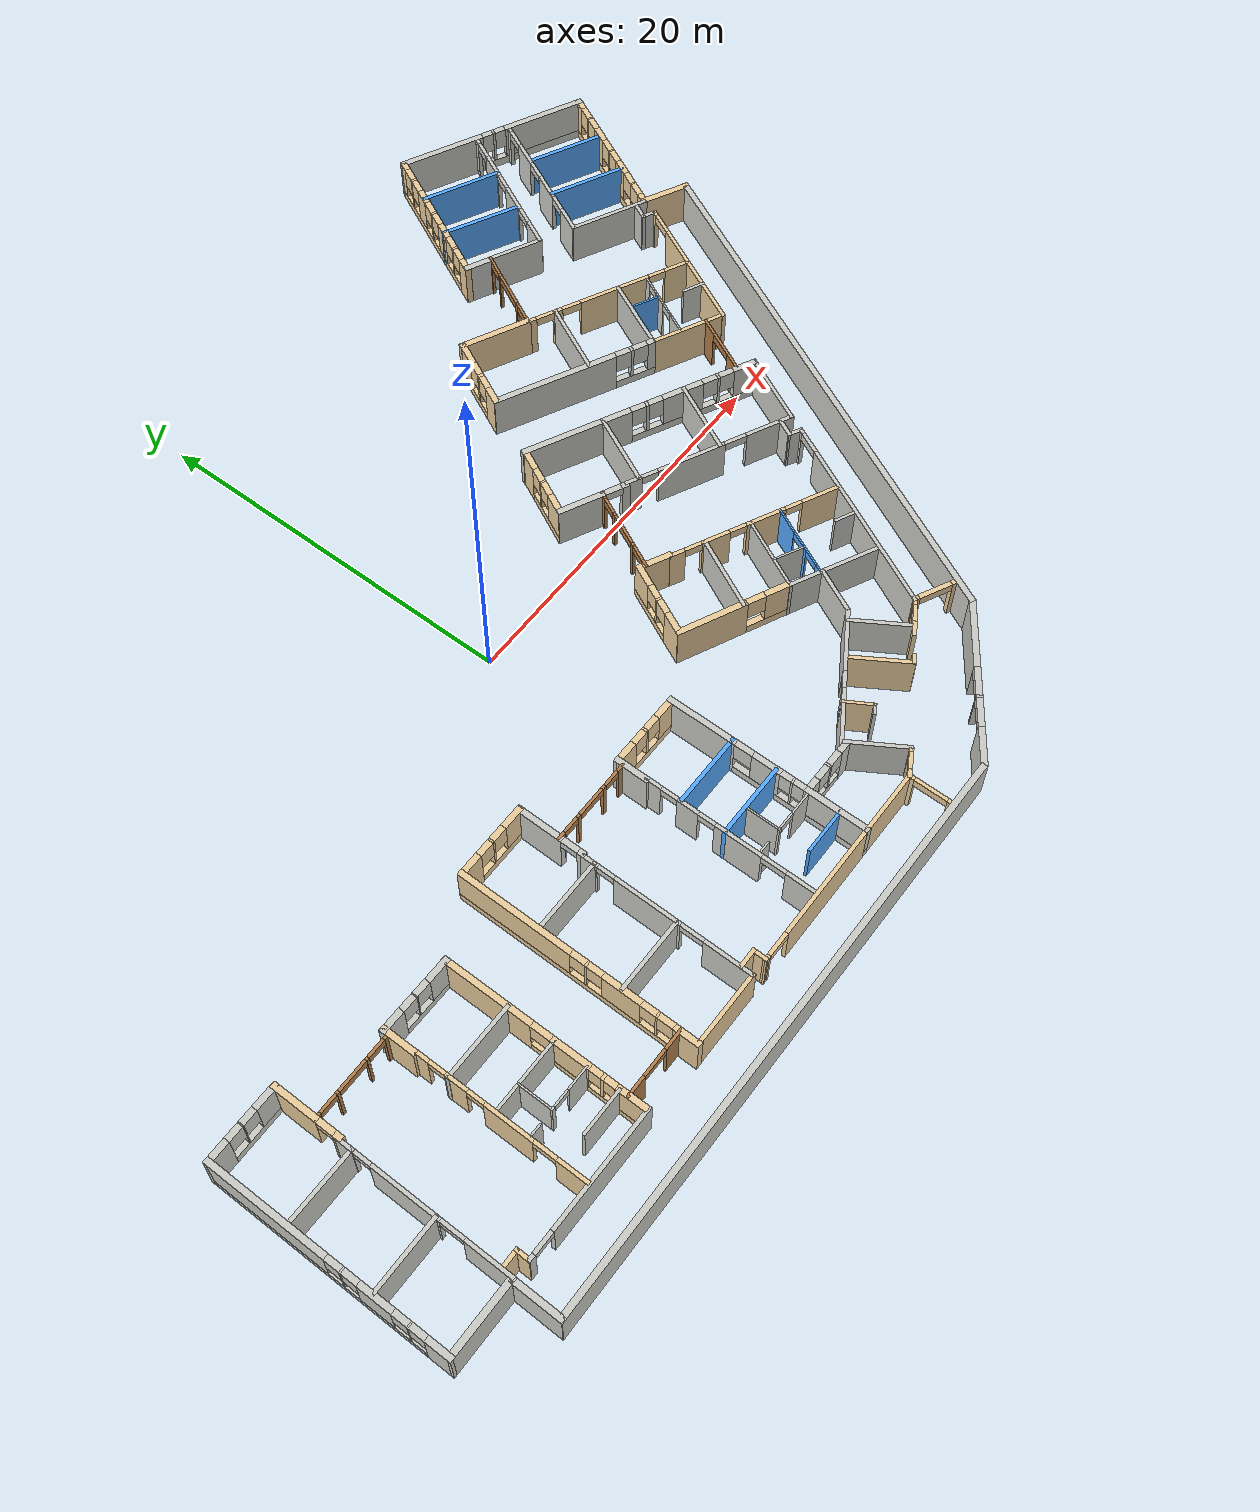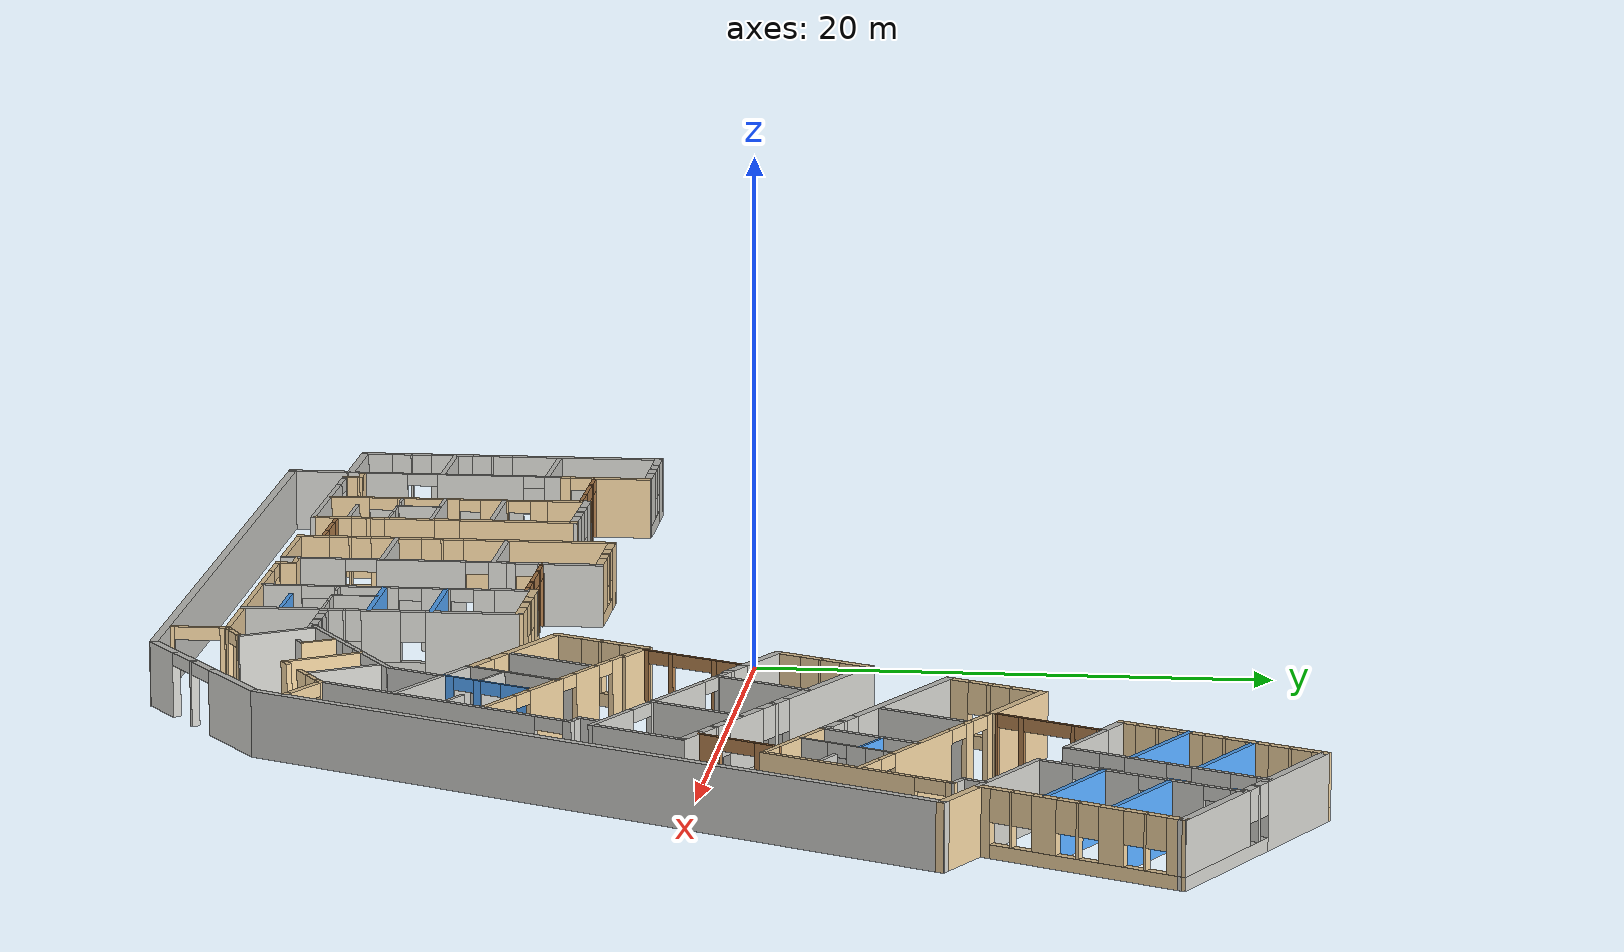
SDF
<?xml version='1.0'?>
<sdf version='1.6'>
  <model name='floor'>
    <pose frame=''>1.8499 0.23643 0 0 -0 0</pose>
    <link name='Wall_102'>
      <pose frame=''>9.8976 9.88157 0 0 -0 1.11772</pose>
      <visual name='Wall_102_Visual_0'>
        <pose frame=''>-1.5828 0 1.25 0 -0 0</pose>
        <geometry>
          <box>
            <size>1.04544 0.32 2.5</size>
          </box>
        </geometry>
        <material>
          <script>
            <uri>file://media/materials/scripts/gazebo.material</uri>
            <name>Gazebo/Grey</name>
          </script>
          <ambient>0.921569 0.807843 0.615686 1</ambient>
        </material>
      </visual>
      <collision name='Wall_102_Collision_0'>
        <geometry>
          <box>
            <size>1.04544 0.32 2.5</size>
          </box>
        </geometry>
        <pose frame=''>-1.5828 0 1.25 0 -0 0</pose>
      </collision>
      <visual name='Wall_102_Visual_1'>
        <pose frame=''>0.522722 0 0.25 0 -0 0</pose>
        <geometry>
          <box>
            <size>3.1656 0.32 0.5</size>
          </box>
        </geometry>
        <material>
          <script>
            <uri>file://media/materials/scripts/gazebo.material</uri>
            <name>Gazebo/Grey</name>
          </script>
          <ambient>0.921569 0.807843 0.615686 1</ambient>
        </material>
      </visual>
      <collision name='Wall_102_Collision_1'>
        <geometry>
          <box>
            <size>3.1656 0.32 0.5</size>
          </box>
        </geometry>
        <pose frame=''>0.522722 0 0.25 0 -0 0</pose>
      </collision>
      <visual name='Wall_102_Visual_2'>
        <pose frame=''>-0.17882 0 1.5 0 -0 0</pose>
        <geometry>
          <box>
            <size>0.162513 0.32 2</size>
          </box>
        </geometry>
        <material>
          <script>
            <uri>file://media/materials/scripts/gazebo.material</uri>
            <name>Gazebo/Grey</name>
          </script>
          <ambient>0.921569 0.807843 0.615686 1</ambient>
        </material>
      </visual>
      <collision name='Wall_102_Collision_2'>
        <geometry>
          <box>
            <size>0.162513 0.32 2</size>
          </box>
        </geometry>
        <pose frame=''>-0.17882 0 1.5 0 -0 0</pose>
      </collision>
      <visual name='Wall_102_Visual_3'>
        <pose frame=''>1.40398 0 1.5 0 -0 0</pose>
        <geometry>
          <box>
            <size>1.40308 0.32 2</size>
          </box>
        </geometry>
        <material>
          <script>
            <uri>file://media/materials/scripts/gazebo.material</uri>
            <name>Gazebo/Grey</name>
          </script>
          <ambient>0.921569 0.807843 0.615686 1</ambient>
        </material>
      </visual>
      <collision name='Wall_102_Collision_3'>
        <geometry>
          <box>
            <size>1.40308 0.32 2</size>
          </box>
        </geometry>
        <pose frame=''>1.40398 0 1.5 0 -0 0</pose>
      </collision>
      <visual name='Wall_102_Visual_4'>
        <pose frame=''>-0.660077 0 1.9 0 -0 0</pose>
        <geometry>
          <box>
            <size>0.8 0.32 1.2</size>
          </box>
        </geometry>
        <material>
          <script>
            <uri>file://media/materials/scripts/gazebo.material</uri>
            <name>Gazebo/Grey</name>
          </script>
          <ambient>0.921569 0.807843 0.615686 1</ambient>
        </material>
      </visual>
      <collision name='Wall_102_Collision_4'>
        <geometry>
          <box>
            <size>0.8 0.32 1.2</size>
          </box>
        </geometry>
        <pose frame=''>-0.660077 0 1.9 0 -0 0</pose>
      </collision>
      <visual name='Wall_102_Visual_5'>
        <pose frame=''>0.302436 0 1.9 0 -0 0</pose>
        <geometry>
          <box>
            <size>0.8 0.32 1.2</size>
          </box>
        </geometry>
        <material>
          <script>
            <uri>file://media/materials/scripts/gazebo.material</uri>
            <name>Gazebo/Grey</name>
          </script>
          <ambient>0.921569 0.807843 0.615686 1</ambient>
        </material>
      </visual>
      <collision name='Wall_102_Collision_5'>
        <geometry>
          <box>
            <size>0.8 0.32 1.2</size>
          </box>
        </geometry>
        <pose frame=''>0.302436 0 1.9 0 -0 0</pose>
      </collision>
    </link>
    <link name='Wall_105'>
      <pose frame=''>15.0533 12.1406 0 0 -0 1.10283</pose>
      <visual name='Wall_105_Visual_0'>
        <pose frame=''>-2.25013 0 1.25 0 -0 0</pose>
        <geometry>
          <box>
            <size>0.370072 0.15 2.5</size>
          </box>
        </geometry>
        <material>
          <script>
            <uri>file://media/materials/scripts/gazebo.material</uri>
            <name>Gazebo/Wood</name>
          </script>
          <ambient>1 1 1 1</ambient>
        </material>
      </visual>
      <collision name='Wall_105_Collision_0'>
        <geometry>
          <box>
            <size>0.370072 0.15 2.5</size>
          </box>
        </geometry>
        <pose frame=''>-2.25013 0 1.25 0 -0 0</pose>
      </collision>
      <visual name='Wall_105_Visual_1'>
        <pose frame=''>-1.06463 0 1.25 0 -0 0</pose>
        <geometry>
          <box>
            <size>0.200912 0.15 2.5</size>
          </box>
        </geometry>
        <material>
          <script>
            <uri>file://media/materials/scripts/gazebo.material</uri>
            <name>Gazebo/Wood</name>
          </script>
          <ambient>1 1 1 1</ambient>
        </material>
      </visual>
      <collision name='Wall_105_Collision_1'>
        <geometry>
          <box>
            <size>0.200912 0.15 2.5</size>
          </box>
        </geometry>
        <pose frame=''>-1.06463 0 1.25 0 -0 0</pose>
      </collision>
      <visual name='Wall_105_Visual_2'>
        <pose frame=''>1.08319 0 1.25 0 -0 0</pose>
        <geometry>
          <box>
            <size>0.159861 0.15 2.5</size>
          </box>
        </geometry>
        <material>
          <script>
            <uri>file://media/materials/scripts/gazebo.material</uri>
            <name>Gazebo/Wood</name>
          </script>
          <ambient>1 1 1 1</ambient>
        </material>
      </visual>
      <collision name='Wall_105_Collision_2'>
        <geometry>
          <box>
            <size>0.159861 0.15 2.5</size>
          </box>
        </geometry>
        <pose frame=''>1.08319 0 1.25 0 -0 0</pose>
      </collision>
      <visual name='Wall_105_Visual_3'>
        <pose frame=''>2.24914 0 1.25 0 -0 0</pose>
        <geometry>
          <box>
            <size>0.372048 0.15 2.5</size>
          </box>
        </geometry>
        <material>
          <script>
            <uri>file://media/materials/scripts/gazebo.material</uri>
            <name>Gazebo/Wood</name>
          </script>
          <ambient>1 1 1 1</ambient>
        </material>
      </visual>
      <collision name='Wall_105_Collision_3'>
        <geometry>
          <box>
            <size>0.372048 0.15 2.5</size>
          </box>
        </geometry>
        <pose frame=''>2.24914 0 1.25 0 -0 0</pose>
      </collision>
      <visual name='Wall_105_Visual_4'>
        <pose frame=''>-1.61509 0 2.25 0 -0 0</pose>
        <geometry>
          <box>
            <size>0.9 0.15 0.5</size>
          </box>
        </geometry>
        <material>
          <script>
            <uri>file://media/materials/scripts/gazebo.material</uri>
            <name>Gazebo/Wood</name>
          </script>
          <ambient>1 1 1 1</ambient>
        </material>
      </visual>
      <collision name='Wall_105_Collision_4'>
        <geometry>
          <box>
            <size>0.9 0.15 0.5</size>
          </box>
        </geometry>
        <pose frame=''>-1.61509 0 2.25 0 -0 0</pose>
      </collision>
      <visual name='Wall_105_Visual_5'>
        <pose frame=''>0.019538 0 2.25 0 -0 0</pose>
        <geometry>
          <box>
            <size>1.96743 0.15 0.5</size>
          </box>
        </geometry>
        <material>
          <script>
            <uri>file://media/materials/scripts/gazebo.material</uri>
            <name>Gazebo/Wood</name>
          </script>
          <ambient>1 1 1 1</ambient>
        </material>
      </visual>
      <collision name='Wall_105_Collision_5'>
        <geometry>
          <box>
            <size>1.96743 0.15 0.5</size>
          </box>
        </geometry>
        <pose frame=''>0.019538 0 2.25 0 -0 0</pose>
      </collision>
      <visual name='Wall_105_Visual_6'>
        <pose frame=''>1.61312 0 2.25 0 -0 0</pose>
        <geometry>
          <box>
            <size>0.9 0.15 0.5</size>
          </box>
        </geometry>
        <material>
          <script>
            <uri>file://media/materials/scripts/gazebo.material</uri>
            <name>Gazebo/Wood</name>
          </script>
          <ambient>1 1 1 1</ambient>
        </material>
      </visual>
      <collision name='Wall_105_Collision_6'>
        <geometry>
          <box>
            <size>0.9 0.15 0.5</size>
          </box>
        </geometry>
        <pose frame=''>1.61312 0 2.25 0 -0 0</pose>
      </collision>
    </link>
    <link name='Wall_112'>
      <pose frame=''>22.1541 5.91057 0 0 -0 1.10738</pose>
      <visual name='Wall_112_Visual_0'>
        <pose frame=''>-0.807941 0 1.25 0 -0 0</pose>
        <geometry>
          <box>
            <size>6.40101 0.2 2.5</size>
          </box>
        </geometry>
        <material>
          <script>
            <uri>file://media/materials/scripts/gazebo.material</uri>
            <name>Gazebo/Grey</name>
          </script>
          <ambient>0.921569 0.807843 0.615686 1</ambient>
        </material>
      </visual>
      <collision name='Wall_112_Collision_0'>
        <geometry>
          <box>
            <size>6.40101 0.2 2.5</size>
          </box>
        </geometry>
        <pose frame=''>-0.807941 0 1.25 0 -0 0</pose>
      </collision>
      <visual name='Wall_112_Visual_1'>
        <pose frame=''>3.83601 0 1.25 0 -0 0</pose>
        <geometry>
          <box>
            <size>0.344876 0.2 2.5</size>
          </box>
        </geometry>
        <material>
          <script>
            <uri>file://media/materials/scripts/gazebo.material</uri>
            <name>Gazebo/Grey</name>
          </script>
          <ambient>0.921569 0.807843 0.615686 1</ambient>
        </material>
      </visual>
      <collision name='Wall_112_Collision_1'>
        <geometry>
          <box>
            <size>0.344876 0.2 2.5</size>
          </box>
        </geometry>
        <pose frame=''>3.83601 0 1.25 0 -0 0</pose>
      </collision>
      <visual name='Wall_112_Visual_2'>
        <pose frame=''>3.02807 0 2.25 0 -0 0</pose>
        <geometry>
          <box>
            <size>1.27101 0.2 0.5</size>
          </box>
        </geometry>
        <material>
          <script>
            <uri>file://media/materials/scripts/gazebo.material</uri>
            <name>Gazebo/Grey</name>
          </script>
          <ambient>0.921569 0.807843 0.615686 1</ambient>
        </material>
      </visual>
      <collision name='Wall_112_Collision_2'>
        <geometry>
          <box>
            <size>1.27101 0.2 0.5</size>
          </box>
        </geometry>
        <pose frame=''>3.02807 0 2.25 0 -0 0</pose>
      </collision>
    </link>
    <link name='Wall_113'>
      <collision name='Wall_113_Collision'>
        <geometry>
          <box>
            <size>0.880212 0.2 2.5</size>
          </box>
        </geometry>
        <pose frame=''>0 0 1.25 0 -0 0</pose>
      </collision>
      <visual name='Wall_113_Visual'>
        <pose frame=''>0 0 1.25 0 -0 0</pose>
        <geometry>
          <box>
            <size>0.880212 0.2 2.5</size>
          </box>
        </geometry>
        <material>
          <script>
            <uri>file://media/materials/scripts/gazebo.material</uri>
            <name>Gazebo/CeilingTiled</name>
          </script>
          <ambient>0.921569 0.807843 0.615686 1</ambient>
        </material>
      </visual>
      <pose frame=''>23.5971 9.55907 0 0 -0 2.67663</pose>
    </link>
    <link name='Wall_114'>
      <collision name='Wall_114_Collision'>
        <geometry>
          <box>
            <size>1.09128 0.2 2.5</size>
          </box>
        </geometry>
        <pose frame=''>0 0 1.25 0 -0 0</pose>
      </collision>
      <visual name='Wall_114_Visual'>
        <pose frame=''>0 0 1.25 0 -0 0</pose>
        <geometry>
          <box>
            <size>1.09128 0.2 2.5</size>
          </box>
        </geometry>
        <material>
          <script>
            <uri>file://media/materials/scripts/gazebo.material</uri>
            <name>Gazebo/CeilingTiled</name>
          </script>
          <ambient>0.921569 0.807843 0.615686 1</ambient>
        </material>
      </visual>
      <pose frame=''>23.4921 10.1101 0 0 -0 1.10765</pose>
    </link>
    <link name='Wall_118'>
      <pose frame=''>16.6583 18.4651 0 0 -0 1.11268</pose>
      <visual name='Wall_118_Visual_0'>
        <pose frame=''>-3.85566 0 1.25 0 -0 0</pose>
        <geometry>
          <box>
            <size>0.842754 0.32 2.5</size>
          </box>
        </geometry>
        <material>
          <script>
            <uri>file://media/materials/scripts/gazebo.material</uri>
            <name>Gazebo/Grey</name>
          </script>
          <ambient>0.921569 0.807843 0.615686 1</ambient>
        </material>
      </visual>
      <collision name='Wall_118_Collision_0'>
        <geometry>
          <box>
            <size>0.842754 0.32 2.5</size>
          </box>
        </geometry>
        <pose frame=''>-3.85566 0 1.25 0 -0 0</pose>
      </collision>
      <visual name='Wall_118_Visual_1'>
        <pose frame=''>0.421377 0 0.25 0 -0 0</pose>
        <geometry>
          <box>
            <size>7.71131 0.32 0.5</size>
          </box>
        </geometry>
        <material>
          <script>
            <uri>file://media/materials/scripts/gazebo.material</uri>
            <name>Gazebo/Grey</name>
          </script>
          <ambient>0.921569 0.807843 0.615686 1</ambient>
        </material>
      </visual>
      <collision name='Wall_118_Collision_1'>
        <geometry>
          <box>
            <size>7.71131 0.32 0.5</size>
          </box>
        </geometry>
        <pose frame=''>0.421377 0 0.25 0 -0 0</pose>
      </collision>
      <visual name='Wall_118_Visual_2'>
        <pose frame=''>-2.57807 0 1.5 0 -0 0</pose>
        <geometry>
          <box>
            <size>0.112411 0.32 2</size>
          </box>
        </geometry>
        <material>
          <script>
            <uri>file://media/materials/scripts/gazebo.material</uri>
            <name>Gazebo/Grey</name>
          </script>
          <ambient>0.921569 0.807843 0.615686 1</ambient>
        </material>
      </visual>
      <collision name='Wall_118_Collision_2'>
        <geometry>
          <box>
            <size>0.112411 0.32 2</size>
          </box>
        </geometry>
        <pose frame=''>-2.57807 0 1.5 0 -0 0</pose>
      </collision>
      <visual name='Wall_118_Visual_3'>
        <pose frame=''>-1.21741 0 1.5 0 -0 0</pose>
        <geometry>
          <box>
            <size>1.00892 0.32 2</size>
          </box>
        </geometry>
        <material>
          <script>
            <uri>file://media/materials/scripts/gazebo.material</uri>
            <name>Gazebo/Grey</name>
          </script>
          <ambient>0.921569 0.807843 0.615686 1</ambient>
        </material>
      </visual>
      <collision name='Wall_118_Collision_3'>
        <geometry>
          <box>
            <size>1.00892 0.32 2</size>
          </box>
        </geometry>
        <pose frame=''>-1.21741 0 1.5 0 -0 0</pose>
      </collision>
      <visual name='Wall_118_Visual_4'>
        <pose frame=''>0.148764 0 1.5 0 -0 0</pose>
        <geometry>
          <box>
            <size>0.123417 0.32 2</size>
          </box>
        </geometry>
        <material>
          <script>
            <uri>file://media/materials/scripts/gazebo.material</uri>
            <name>Gazebo/Grey</name>
          </script>
          <ambient>0.921569 0.807843 0.615686 1</ambient>
        </material>
      </visual>
      <collision name='Wall_118_Collision_4'>
        <geometry>
          <box>
            <size>0.123417 0.32 2</size>
          </box>
        </geometry>
        <pose frame=''>0.148764 0 1.5 0 -0 0</pose>
      </collision>
      <visual name='Wall_118_Visual_5'>
        <pose frame=''>1.46776 0 1.5 0 -0 0</pose>
        <geometry>
          <box>
            <size>0.914569 0.32 2</size>
          </box>
        </geometry>
        <material>
          <script>
            <uri>file://media/materials/scripts/gazebo.material</uri>
            <name>Gazebo/Grey</name>
          </script>
          <ambient>0.921569 0.807843 0.615686 1</ambient>
        </material>
      </visual>
      <collision name='Wall_118_Collision_5'>
        <geometry>
          <box>
            <size>0.914569 0.32 2</size>
          </box>
        </geometry>
        <pose frame=''>1.46776 0 1.5 0 -0 0</pose>
      </collision>
      <visual name='Wall_118_Visual_6'>
        <pose frame=''>2.7876 0 1.5 0 -0 0</pose>
        <geometry>
          <box>
            <size>0.12511 0.32 2</size>
          </box>
        </geometry>
        <material>
          <script>
            <uri>file://media/materials/scripts/gazebo.material</uri>
            <name>Gazebo/Grey</name>
          </script>
          <ambient>0.921569 0.807843 0.615686 1</ambient>
        </material>
      </visual>
      <collision name='Wall_118_Collision_6'>
        <geometry>
          <box>
            <size>0.12511 0.32 2</size>
          </box>
        </geometry>
        <pose frame=''>2.7876 0 1.5 0 -0 0</pose>
      </collision>
      <visual name='Wall_118_Visual_7'>
        <pose frame=''>3.96359 0 1.5 0 -0 0</pose>
        <geometry>
          <box>
            <size>0.626882 0.32 2</size>
          </box>
        </geometry>
        <material>
          <script>
            <uri>file://media/materials/scripts/gazebo.material</uri>
            <name>Gazebo/Grey</name>
          </script>
          <ambient>0.921569 0.807843 0.615686 1</ambient>
        </material>
      </visual>
      <collision name='Wall_118_Collision_7'>
        <geometry>
          <box>
            <size>0.626882 0.32 2</size>
          </box>
        </geometry>
        <pose frame=''>3.96359 0 1.5 0 -0 0</pose>
      </collision>
      <visual name='Wall_118_Visual_8'>
        <pose frame=''>-3.03428 0 1.9 0 -0 0</pose>
        <geometry>
          <box>
            <size>0.8 0.32 1.2</size>
          </box>
        </geometry>
        <material>
          <script>
            <uri>file://media/materials/scripts/gazebo.material</uri>
            <name>Gazebo/Grey</name>
          </script>
          <ambient>0.921569 0.807843 0.615686 1</ambient>
        </material>
      </visual>
      <collision name='Wall_118_Collision_8'>
        <geometry>
          <box>
            <size>0.8 0.32 1.2</size>
          </box>
        </geometry>
        <pose frame=''>-3.03428 0 1.9 0 -0 0</pose>
      </collision>
      <visual name='Wall_118_Visual_9'>
        <pose frame=''>-2.12187 0 1.9 0 -0 0</pose>
        <geometry>
          <box>
            <size>0.8 0.32 1.2</size>
          </box>
        </geometry>
        <material>
          <script>
            <uri>file://media/materials/scripts/gazebo.material</uri>
            <name>Gazebo/Grey</name>
          </script>
          <ambient>0.921569 0.807843 0.615686 1</ambient>
        </material>
      </visual>
      <collision name='Wall_118_Collision_9'>
        <geometry>
          <box>
            <size>0.8 0.32 1.2</size>
          </box>
        </geometry>
        <pose frame=''>-2.12187 0 1.9 0 -0 0</pose>
      </collision>
      <visual name='Wall_118_Visual_10'>
        <pose frame=''>-0.312945 0 1.9 0 -0 0</pose>
        <geometry>
          <box>
            <size>0.8 0.32 1.2</size>
          </box>
        </geometry>
        <material>
          <script>
            <uri>file://media/materials/scripts/gazebo.material</uri>
            <name>Gazebo/Grey</name>
          </script>
          <ambient>0.921569 0.807843 0.615686 1</ambient>
        </material>
      </visual>
      <collision name='Wall_118_Collision_10'>
        <geometry>
          <box>
            <size>0.8 0.32 1.2</size>
          </box>
        </geometry>
        <pose frame=''>-0.312945 0 1.9 0 -0 0</pose>
      </collision>
      <visual name='Wall_118_Visual_11'>
        <pose frame=''>0.610473 0 1.9 0 -0 0</pose>
        <geometry>
          <box>
            <size>0.8 0.32 1.2</size>
          </box>
        </geometry>
        <material>
          <script>
            <uri>file://media/materials/scripts/gazebo.material</uri>
            <name>Gazebo/Grey</name>
          </script>
          <ambient>0.921569 0.807843 0.615686 1</ambient>
        </material>
      </visual>
      <collision name='Wall_118_Collision_11'>
        <geometry>
          <box>
            <size>0.8 0.32 1.2</size>
          </box>
        </geometry>
        <pose frame=''>0.610473 0 1.9 0 -0 0</pose>
      </collision>
      <visual name='Wall_118_Visual_12'>
        <pose frame=''>2.32504 0 1.9 0 -0 0</pose>
        <geometry>
          <box>
            <size>0.8 0.32 1.2</size>
          </box>
        </geometry>
        <material>
          <script>
            <uri>file://media/materials/scripts/gazebo.material</uri>
            <name>Gazebo/Grey</name>
          </script>
          <ambient>0.921569 0.807843 0.615686 1</ambient>
        </material>
      </visual>
      <collision name='Wall_118_Collision_12'>
        <geometry>
          <box>
            <size>0.8 0.32 1.2</size>
          </box>
        </geometry>
        <pose frame=''>2.32504 0 1.9 0 -0 0</pose>
      </collision>
      <visual name='Wall_118_Visual_13'>
        <pose frame=''>3.25015 0 1.9 0 -0 0</pose>
        <geometry>
          <box>
            <size>0.8 0.32 1.2</size>
          </box>
        </geometry>
        <material>
          <script>
            <uri>file://media/materials/scripts/gazebo.material</uri>
            <name>Gazebo/Grey</name>
          </script>
          <ambient>0.921569 0.807843 0.615686 1</ambient>
        </material>
      </visual>
      <collision name='Wall_118_Collision_13'>
        <geometry>
          <box>
            <size>0.8 0.32 1.2</size>
          </box>
        </geometry>
        <pose frame=''>3.25015 0 1.9 0 -0 0</pose>
      </collision>
    </link>
    <link name='Wall_119'>
      <pose frame=''>23.1751 19.8661 0 0 0 -0.453976</pose>
      <visual name='Wall_119_Visual_0'>
        <pose frame=''>-3.01092 0 1.25 0 -0 0</pose>
        <geometry>
          <box>
            <size>4.74899 0.32 2.5</size>
          </box>
        </geometry>
        <material>
          <script>
            <uri>file://media/materials/scripts/gazebo.material</uri>
            <name>Gazebo/CeilingTiled</name>
          </script>
          <ambient>0.921569 0.807843 0.615686 1</ambient>
        </material>
      </visual>
      <collision name='Wall_119_Collision_0'>
        <geometry>
          <box>
            <size>4.74899 0.32 2.5</size>
          </box>
        </geometry>
        <pose frame=''>-3.01092 0 1.25 0 -0 0</pose>
      </collision>
      <visual name='Wall_119_Visual_1'>
        <pose frame=''>2.3745 0 0.25 0 -0 0</pose>
        <geometry>
          <box>
            <size>6.02183 0.32 0.5</size>
          </box>
        </geometry>
        <material>
          <script>
            <uri>file://media/materials/scripts/gazebo.material</uri>
            <name>Gazebo/CeilingTiled</name>
          </script>
          <ambient>0.921569 0.807843 0.615686 1</ambient>
        </material>
      </visual>
      <collision name='Wall_119_Collision_1'>
        <geometry>
          <box>
            <size>6.02183 0.32 0.5</size>
          </box>
        </geometry>
        <pose frame=''>2.3745 0 0.25 0 -0 0</pose>
      </collision>
      <visual name='Wall_119_Visual_2'>
        <pose frame=''>0.029674 0 1.5 0 -0 0</pose>
        <geometry>
          <box>
            <size>0.132185 0.32 2</size>
          </box>
        </geometry>
        <material>
          <script>
            <uri>file://media/materials/scripts/gazebo.material</uri>
            <name>Gazebo/CeilingTiled</name>
          </script>
          <ambient>0.921569 0.807843 0.615686 1</ambient>
        </material>
      </visual>
      <collision name='Wall_119_Collision_2'>
        <geometry>
          <box>
            <size>0.132185 0.32 2</size>
          </box>
        </geometry>
        <pose frame=''>0.029674 0 1.5 0 -0 0</pose>
      </collision>
      <visual name='Wall_119_Visual_3'>
        <pose frame=''>3.04059 0 1.5 0 -0 0</pose>
        <geometry>
          <box>
            <size>4.68965 0.32 2</size>
          </box>
        </geometry>
        <material>
          <script>
            <uri>file://media/materials/scripts/gazebo.material</uri>
            <name>Gazebo/CeilingTiled</name>
          </script>
          <ambient>0.921569 0.807843 0.615686 1</ambient>
        </material>
      </visual>
      <collision name='Wall_119_Collision_3'>
        <geometry>
          <box>
            <size>4.68965 0.32 2</size>
          </box>
        </geometry>
        <pose frame=''>3.04059 0 1.5 0 -0 0</pose>
      </collision>
      <visual name='Wall_119_Visual_4'>
        <pose frame=''>-0.336419 0 1.9 0 -0 0</pose>
        <geometry>
          <box>
            <size>0.6 0.32 1.2</size>
          </box>
        </geometry>
        <material>
          <script>
            <uri>file://media/materials/scripts/gazebo.material</uri>
            <name>Gazebo/CeilingTiled</name>
          </script>
          <ambient>0.921569 0.807843 0.615686 1</ambient>
        </material>
      </visual>
      <collision name='Wall_119_Collision_4'>
        <geometry>
          <box>
            <size>0.6 0.32 1.2</size>
          </box>
        </geometry>
        <pose frame=''>-0.336419 0 1.9 0 -0 0</pose>
      </collision>
      <visual name='Wall_119_Visual_5'>
        <pose frame=''>0.395766 0 1.9 0 -0 0</pose>
        <geometry>
          <box>
            <size>0.6 0.32 1.2</size>
          </box>
        </geometry>
        <material>
          <script>
            <uri>file://media/materials/scripts/gazebo.material</uri>
            <name>Gazebo/CeilingTiled</name>
          </script>
          <ambient>0.921569 0.807843 0.615686 1</ambient>
        </material>
      </visual>
      <collision name='Wall_119_Collision_5'>
        <geometry>
          <box>
            <size>0.6 0.32 1.2</size>
          </box>
        </geometry>
        <pose frame=''>0.395766 0 1.9 0 -0 0</pose>
      </collision>
    </link>
    <link name='Wall_12'>
      <collision name='Wall_12_Collision'>
        <geometry>
          <box>
            <size>4.1128 0.2 2.5</size>
          </box>
        </geometry>
        <pose frame=''>0 0 1.25 0 -0 0</pose>
      </collision>
      <visual name='Wall_12_Visual'>
        <pose frame=''>0 0 1.25 0 -0 0</pose>
        <geometry>
          <box>
            <size>4.1128 0.2 2.5</size>
          </box>
        </geometry>
        <material>
          <script>
            <uri>file://media/materials/scripts/gazebo.material</uri>
            <name>Gazebo/CeilingTiled</name>
          </script>
          <ambient>0.333333 0.666667 1 1</ambient>
        </material>
      </visual>
      <pose frame=''>14.4755 -0.590962 0 0 0 -2.03138</pose>
    </link>
    <link name='Wall_122'>
      <pose frame=''>26.0437 13.9556 0 0 -0 1.10317</pose>
      <visual name='Wall_122_Visual_0'>
        <pose frame=''>-3.86829 0 1.25 0 -0 0</pose>
        <geometry>
          <box>
            <size>0.669026 0.32 2.5</size>
          </box>
        </geometry>
        <material>
          <script>
            <uri>file://media/materials/scripts/gazebo.material</uri>
            <name>Gazebo/Grey</name>
          </script>
          <ambient>0.921569 0.807843 0.615686 1</ambient>
        </material>
      </visual>
      <collision name='Wall_122_Collision_0'>
        <geometry>
          <box>
            <size>0.669026 0.32 2.5</size>
          </box>
        </geometry>
        <pose frame=''>-3.86829 0 1.25 0 -0 0</pose>
      </collision>
      <visual name='Wall_122_Visual_1'>
        <pose frame=''>0.334513 0 0.25 0 -0 0</pose>
        <geometry>
          <box>
            <size>7.73658 0.32 0.5</size>
          </box>
        </geometry>
        <material>
          <script>
            <uri>file://media/materials/scripts/gazebo.material</uri>
            <name>Gazebo/Grey</name>
          </script>
          <ambient>0.921569 0.807843 0.615686 1</ambient>
        </material>
      </visual>
      <collision name='Wall_122_Collision_1'>
        <geometry>
          <box>
            <size>7.73658 0.32 0.5</size>
          </box>
        </geometry>
        <pose frame=''>0.334513 0 0.25 0 -0 0</pose>
      </collision>
      <visual name='Wall_122_Visual_2'>
        <pose frame=''>-2.69806 0 1.5 0 -0 0</pose>
        <geometry>
          <box>
            <size>0.071431 0.32 2</size>
          </box>
        </geometry>
        <material>
          <script>
            <uri>file://media/materials/scripts/gazebo.material</uri>
            <name>Gazebo/Grey</name>
          </script>
          <ambient>0.921569 0.807843 0.615686 1</ambient>
        </material>
      </visual>
      <collision name='Wall_122_Collision_2'>
        <geometry>
          <box>
            <size>0.071431 0.32 2</size>
          </box>
        </geometry>
        <pose frame=''>-2.69806 0 1.5 0 -0 0</pose>
      </collision>
      <visual name='Wall_122_Visual_3'>
        <pose frame=''>-1.37855 0 1.5 0 -0 0</pose>
        <geometry>
          <box>
            <size>0.967581 0.32 2</size>
          </box>
        </geometry>
        <material>
          <script>
            <uri>file://media/materials/scripts/gazebo.material</uri>
            <name>Gazebo/Grey</name>
          </script>
          <ambient>0.921569 0.807843 0.615686 1</ambient>
        </material>
      </visual>
      <collision name='Wall_122_Collision_3'>
        <geometry>
          <box>
            <size>0.967581 0.32 2</size>
          </box>
        </geometry>
        <pose frame=''>-1.37855 0 1.5 0 -0 0</pose>
      </collision>
      <visual name='Wall_122_Visual_4'>
        <pose frame=''>-0.045945 0 1.5 0 -0 0</pose>
        <geometry>
          <box>
            <size>0.097636 0.32 2</size>
          </box>
        </geometry>
        <material>
          <script>
            <uri>file://media/materials/scripts/gazebo.material</uri>
            <name>Gazebo/Grey</name>
          </script>
          <ambient>0.921569 0.807843 0.615686 1</ambient>
        </material>
      </visual>
      <collision name='Wall_122_Collision_4'>
        <geometry>
          <box>
            <size>0.097636 0.32 2</size>
          </box>
        </geometry>
        <pose frame=''>-0.045945 0 1.5 0 -0 0</pose>
      </collision>
      <visual name='Wall_122_Visual_5'>
        <pose frame=''>1.29056 0 1.5 0 -0 0</pose>
        <geometry>
          <box>
            <size>0.975383 0.32 2</size>
          </box>
        </geometry>
        <material>
          <script>
            <uri>file://media/materials/scripts/gazebo.material</uri>
            <name>Gazebo/Grey</name>
          </script>
          <ambient>0.921569 0.807843 0.615686 1</ambient>
        </material>
      </visual>
      <collision name='Wall_122_Collision_5'>
        <geometry>
          <box>
            <size>0.975383 0.32 2</size>
          </box>
        </geometry>
        <pose frame=''>1.29056 0 1.5 0 -0 0</pose>
      </collision>
      <visual name='Wall_122_Visual_6'>
        <pose frame=''>2.62042 0 1.5 0 -0 0</pose>
        <geometry>
          <box>
            <size>0.08433 0.32 2</size>
          </box>
        </geometry>
        <material>
          <script>
            <uri>file://media/materials/scripts/gazebo.material</uri>
            <name>Gazebo/Grey</name>
          </script>
          <ambient>0.921569 0.807843 0.615686 1</ambient>
        </material>
      </visual>
      <collision name='Wall_122_Collision_6'>
        <geometry>
          <box>
            <size>0.08433 0.32 2</size>
          </box>
        </geometry>
        <pose frame=''>2.62042 0 1.5 0 -0 0</pose>
      </collision>
      <visual name='Wall_122_Visual_7'>
        <pose frame=''>3.83269 0 1.5 0 -0 0</pose>
        <geometry>
          <box>
            <size>0.740215 0.32 2</size>
          </box>
        </geometry>
        <material>
          <script>
            <uri>file://media/materials/scripts/gazebo.material</uri>
            <name>Gazebo/Grey</name>
          </script>
          <ambient>0.921569 0.807843 0.615686 1</ambient>
        </material>
      </visual>
      <collision name='Wall_122_Collision_7'>
        <geometry>
          <box>
            <size>0.740215 0.32 2</size>
          </box>
        </geometry>
        <pose frame=''>3.83269 0 1.5 0 -0 0</pose>
      </collision>
      <visual name='Wall_122_Visual_8'>
        <pose frame=''>-3.13377 0 1.9 0 -0 0</pose>
        <geometry>
          <box>
            <size>0.8 0.32 1.2</size>
          </box>
        </geometry>
        <material>
          <script>
            <uri>file://media/materials/scripts/gazebo.material</uri>
            <name>Gazebo/Grey</name>
          </script>
          <ambient>0.921569 0.807843 0.615686 1</ambient>
        </material>
      </visual>
      <collision name='Wall_122_Collision_8'>
        <geometry>
          <box>
            <size>0.8 0.32 1.2</size>
          </box>
        </geometry>
        <pose frame=''>-3.13377 0 1.9 0 -0 0</pose>
      </collision>
      <visual name='Wall_122_Visual_9'>
        <pose frame=''>-2.26234 0 1.9 0 -0 0</pose>
        <geometry>
          <box>
            <size>0.8 0.32 1.2</size>
          </box>
        </geometry>
        <material>
          <script>
            <uri>file://media/materials/scripts/gazebo.material</uri>
            <name>Gazebo/Grey</name>
          </script>
          <ambient>0.921569 0.807843 0.615686 1</ambient>
        </material>
      </visual>
      <collision name='Wall_122_Collision_9'>
        <geometry>
          <box>
            <size>0.8 0.32 1.2</size>
          </box>
        </geometry>
        <pose frame=''>-2.26234 0 1.9 0 -0 0</pose>
      </collision>
      <visual name='Wall_122_Visual_10'>
        <pose frame=''>-0.494763 0 1.9 0 -0 0</pose>
        <geometry>
          <box>
            <size>0.8 0.32 1.2</size>
          </box>
        </geometry>
        <material>
          <script>
            <uri>file://media/materials/scripts/gazebo.material</uri>
            <name>Gazebo/Grey</name>
          </script>
          <ambient>0.921569 0.807843 0.615686 1</ambient>
        </material>
      </visual>
      <collision name='Wall_122_Collision_10'>
        <geometry>
          <box>
            <size>0.8 0.32 1.2</size>
          </box>
        </geometry>
        <pose frame=''>-0.494763 0 1.9 0 -0 0</pose>
      </collision>
      <visual name='Wall_122_Visual_11'>
        <pose frame=''>0.402873 0 1.9 0 -0 0</pose>
        <geometry>
          <box>
            <size>0.8 0.32 1.2</size>
          </box>
        </geometry>
        <material>
          <script>
            <uri>file://media/materials/scripts/gazebo.material</uri>
            <name>Gazebo/Grey</name>
          </script>
          <ambient>0.921569 0.807843 0.615686 1</ambient>
        </material>
      </visual>
      <collision name='Wall_122_Collision_11'>
        <geometry>
          <box>
            <size>0.8 0.32 1.2</size>
          </box>
        </geometry>
        <pose frame=''>0.402873 0 1.9 0 -0 0</pose>
      </collision>
      <visual name='Wall_122_Visual_12'>
        <pose frame=''>2.17826 0 1.9 0 -0 0</pose>
        <geometry>
          <box>
            <size>0.8 0.32 1.2</size>
          </box>
        </geometry>
        <material>
          <script>
            <uri>file://media/materials/scripts/gazebo.material</uri>
            <name>Gazebo/Grey</name>
          </script>
          <ambient>0.921569 0.807843 0.615686 1</ambient>
        </material>
      </visual>
      <collision name='Wall_122_Collision_12'>
        <geometry>
          <box>
            <size>0.8 0.32 1.2</size>
          </box>
        </geometry>
        <pose frame=''>2.17826 0 1.9 0 -0 0</pose>
      </collision>
      <visual name='Wall_122_Visual_13'>
        <pose frame=''>3.06259 0 1.9 0 -0 0</pose>
        <geometry>
          <box>
            <size>0.8 0.32 1.2</size>
          </box>
        </geometry>
        <material>
          <script>
            <uri>file://media/materials/scripts/gazebo.material</uri>
            <name>Gazebo/Grey</name>
          </script>
          <ambient>0.921569 0.807843 0.615686 1</ambient>
        </material>
      </visual>
      <collision name='Wall_122_Collision_13'>
        <geometry>
          <box>
            <size>0.8 0.32 1.2</size>
          </box>
        </geometry>
        <pose frame=''>3.06259 0 1.9 0 -0 0</pose>
      </collision>
    </link>
    <link name='Wall_126'>
      <collision name='Wall_126_Collision'>
        <geometry>
          <box>
            <size>2.76484 0.32 2.5</size>
          </box>
        </geometry>
        <pose frame=''>0 0 1.25 0 -0 0</pose>
      </collision>
      <visual name='Wall_126_Visual'>
        <pose frame=''>0 0 1.25 0 -0 0</pose>
        <geometry>
          <box>
            <size>2.76484 0.32 2.5</size>
          </box>
        </geometry>
        <material>
          <script>
            <uri>file://media/materials/scripts/gazebo.material</uri>
            <name>Gazebo/Grey</name>
          </script>
          <ambient>0.921569 0.807843 0.615686 1</ambient>
        </material>
      </visual>
      <pose frame=''>25.33 9.77476 0 0 0 -0.469549</pose>
    </link>
    <link name='Wall_130'>
      <collision name='Wall_130_Collision'>
        <geometry>
          <box>
            <size>29.5051 0.32 2.5</size>
          </box>
        </geometry>
        <pose frame=''>0 0 1.25 0 -0 0</pose>
      </collision>
      <visual name='Wall_130_Visual'>
        <pose frame=''>0 0 1.25 0 -0 0</pose>
        <geometry>
          <box>
            <size>29.5051 0.32 2.5</size>
          </box>
        </geometry>
        <material>
          <script>
            <uri>file://media/materials/scripts/gazebo.material</uri>
            <name>Gazebo/CeilingTiled</name>
          </script>
          <ambient>0.921569 0.807843 0.615686 1</ambient>
        </material>
      </visual>
      <pose frame=''>19.9743 -3.85686 0 0 0 -2.02831</pose>
    </link>
    <link name='Wall_132'>
      <pose frame=''>20.4722 16.6376 0 0 -0 1.10974</pose>
      <visual name='Wall_132_Visual_0'>
        <pose frame=''>-3.39266 0 1.25 0 -0 0</pose>
        <geometry>
          <box>
            <size>1.52449 0.2 2.5</size>
          </box>
        </geometry>
        <material>
          <script>
            <uri>file://media/materials/scripts/gazebo.material</uri>
            <name>Gazebo/CeilingTiled</name>
          </script>
          <ambient>0.921569 0.807843 0.615686 1</ambient>
        </material>
      </visual>
      <collision name='Wall_132_Collision_0'>
        <geometry>
          <box>
            <size>1.52449 0.2 2.5</size>
          </box>
        </geometry>
        <pose frame=''>-3.39266 0 1.25 0 -0 0</pose>
      </collision>
      <visual name='Wall_132_Visual_1'>
        <pose frame=''>-0.782298 0 1.25 0 -0 0</pose>
        <geometry>
          <box>
            <size>1.69291 0.2 2.5</size>
          </box>
        </geometry>
        <material>
          <script>
            <uri>file://media/materials/scripts/gazebo.material</uri>
            <name>Gazebo/CeilingTiled</name>
          </script>
          <ambient>0.921569 0.807843 0.615686 1</ambient>
        </material>
      </visual>
      <collision name='Wall_132_Collision_1'>
        <geometry>
          <box>
            <size>1.69291 0.2 2.5</size>
          </box>
        </geometry>
        <pose frame=''>-0.782298 0 1.25 0 -0 0</pose>
      </collision>
      <visual name='Wall_132_Visual_2'>
        <pose frame=''>1.8204 0 1.25 0 -0 0</pose>
        <geometry>
          <box>
            <size>1.54069 0.2 2.5</size>
          </box>
        </geometry>
        <material>
          <script>
            <uri>file://media/materials/scripts/gazebo.material</uri>
            <name>Gazebo/CeilingTiled</name>
          </script>
          <ambient>0.921569 0.807843 0.615686 1</ambient>
        </material>
      </visual>
      <collision name='Wall_132_Collision_2'>
        <geometry>
          <box>
            <size>1.54069 0.2 2.5</size>
          </box>
        </geometry>
        <pose frame=''>1.8204 0 1.25 0 -0 0</pose>
      </collision>
      <visual name='Wall_132_Visual_3'>
        <pose frame=''>3.89079 0 1.25 0 -0 0</pose>
        <geometry>
          <box>
            <size>0.528217 0.2 2.5</size>
          </box>
        </geometry>
        <material>
          <script>
            <uri>file://media/materials/scripts/gazebo.material</uri>
            <name>Gazebo/CeilingTiled</name>
          </script>
          <ambient>0.921569 0.807843 0.615686 1</ambient>
        </material>
      </visual>
      <collision name='Wall_132_Collision_3'>
        <geometry>
          <box>
            <size>0.528217 0.2 2.5</size>
          </box>
        </geometry>
        <pose frame=''>3.89079 0 1.25 0 -0 0</pose>
      </collision>
      <visual name='Wall_132_Visual_4'>
        <pose frame=''>-2.12958 0 2.25 0 -0 0</pose>
        <geometry>
          <box>
            <size>1.00166 0.2 0.5</size>
          </box>
        </geometry>
        <material>
          <script>
            <uri>file://media/materials/scripts/gazebo.material</uri>
            <name>Gazebo/CeilingTiled</name>
          </script>
          <ambient>0.921569 0.807843 0.615686 1</ambient>
        </material>
      </visual>
      <collision name='Wall_132_Collision_4'>
        <geometry>
          <box>
            <size>1.00166 0.2 0.5</size>
          </box>
        </geometry>
        <pose frame=''>-2.12958 0 2.25 0 -0 0</pose>
      </collision>
      <visual name='Wall_132_Visual_5'>
        <pose frame=''>0.557103 0 2.25 0 -0 0</pose>
        <geometry>
          <box>
            <size>0.985898 0.2 0.5</size>
          </box>
        </geometry>
        <material>
          <script>
            <uri>file://media/materials/scripts/gazebo.material</uri>
            <name>Gazebo/CeilingTiled</name>
          </script>
          <ambient>0.921569 0.807843 0.615686 1</ambient>
        </material>
      </visual>
      <collision name='Wall_132_Collision_5'>
        <geometry>
          <box>
            <size>0.985898 0.2 0.5</size>
          </box>
        </geometry>
        <pose frame=''>0.557103 0 2.25 0 -0 0</pose>
      </collision>
      <visual name='Wall_132_Visual_6'>
        <pose frame=''>3.10871 0 2.25 0 -0 0</pose>
        <geometry>
          <box>
            <size>1.03594 0.2 0.5</size>
          </box>
        </geometry>
        <material>
          <script>
            <uri>file://media/materials/scripts/gazebo.material</uri>
            <name>Gazebo/CeilingTiled</name>
          </script>
          <ambient>0.921569 0.807843 0.615686 1</ambient>
        </material>
      </visual>
      <collision name='Wall_132_Collision_6'>
        <geometry>
          <box>
            <size>1.03594 0.2 0.5</size>
          </box>
        </geometry>
        <pose frame=''>3.10871 0 2.25 0 -0 0</pose>
      </collision>
    </link>
    <link name='Wall_134'>
      <pose frame=''>22.224 15.8028 0 0 -0 1.11614</pose>
      <visual name='Wall_134_Visual_0'>
        <pose frame=''>-3.38319 0 1.25 0 -0 0</pose>
        <geometry>
          <box>
            <size>1.49229 0.2 2.5</size>
          </box>
        </geometry>
        <material>
          <script>
            <uri>file://media/materials/scripts/gazebo.material</uri>
            <name>Gazebo/CeilingTiled</name>
          </script>
          <ambient>0.921569 0.807843 0.615686 1</ambient>
        </material>
      </visual>
      <collision name='Wall_134_Collision_0'>
        <geometry>
          <box>
            <size>1.49229 0.2 2.5</size>
          </box>
        </geometry>
        <pose frame=''>-3.38319 0 1.25 0 -0 0</pose>
      </collision>
      <visual name='Wall_134_Visual_1'>
        <pose frame=''>-0.835285 0 1.25 0 -0 0</pose>
        <geometry>
          <box>
            <size>1.62619 0.2 2.5</size>
          </box>
        </geometry>
        <material>
          <script>
            <uri>file://media/materials/scripts/gazebo.material</uri>
            <name>Gazebo/CeilingTiled</name>
          </script>
          <ambient>0.921569 0.807843 0.615686 1</ambient>
        </material>
      </visual>
      <collision name='Wall_134_Collision_1'>
        <geometry>
          <box>
            <size>1.62619 0.2 2.5</size>
          </box>
        </geometry>
        <pose frame=''>-0.835285 0 1.25 0 -0 0</pose>
      </collision>
      <visual name='Wall_134_Visual_2'>
        <pose frame=''>1.81493 0 1.25 0 -0 0</pose>
        <geometry>
          <box>
            <size>1.46679 0.2 2.5</size>
          </box>
        </geometry>
        <material>
          <script>
            <uri>file://media/materials/scripts/gazebo.material</uri>
            <name>Gazebo/CeilingTiled</name>
          </script>
          <ambient>0.921569 0.807843 0.615686 1</ambient>
        </material>
      </visual>
      <collision name='Wall_134_Collision_2'>
        <geometry>
          <box>
            <size>1.46679 0.2 2.5</size>
          </box>
        </geometry>
        <pose frame=''>1.81493 0 1.25 0 -0 0</pose>
      </collision>
      <visual name='Wall_134_Visual_3'>
        <pose frame=''>3.87749 0 1.25 0 -0 0</pose>
        <geometry>
          <box>
            <size>0.503684 0.2 2.5</size>
          </box>
        </geometry>
        <material>
          <script>
            <uri>file://media/materials/scripts/gazebo.material</uri>
            <name>Gazebo/CeilingTiled</name>
          </script>
          <ambient>0.921569 0.807843 0.615686 1</ambient>
        </material>
      </visual>
      <collision name='Wall_134_Collision_3'>
        <geometry>
          <box>
            <size>0.503684 0.2 2.5</size>
          </box>
        </geometry>
        <pose frame=''>3.87749 0 1.25 0 -0 0</pose>
      </collision>
      <visual name='Wall_134_Visual_4'>
        <pose frame=''>-2.14271 0 2.25 0 -0 0</pose>
        <geometry>
          <box>
            <size>0.988661 0.2 0.5</size>
          </box>
        </geometry>
        <material>
          <script>
            <uri>file://media/materials/scripts/gazebo.material</uri>
            <name>Gazebo/CeilingTiled</name>
          </script>
          <ambient>0.921569 0.807843 0.615686 1</ambient>
        </material>
      </visual>
      <collision name='Wall_134_Collision_4'>
        <geometry>
          <box>
            <size>0.988661 0.2 0.5</size>
          </box>
        </geometry>
        <pose frame=''>-2.14271 0 2.25 0 -0 0</pose>
      </collision>
      <visual name='Wall_134_Visual_5'>
        <pose frame=''>0.529675 0 2.25 0 -0 0</pose>
        <geometry>
          <box>
            <size>1.10373 0.2 0.5</size>
          </box>
        </geometry>
        <material>
          <script>
            <uri>file://media/materials/scripts/gazebo.material</uri>
            <name>Gazebo/CeilingTiled</name>
          </script>
          <ambient>0.921569 0.807843 0.615686 1</ambient>
        </material>
      </visual>
      <collision name='Wall_134_Collision_5'>
        <geometry>
          <box>
            <size>1.10373 0.2 0.5</size>
          </box>
        </geometry>
        <pose frame=''>0.529675 0 2.25 0 -0 0</pose>
      </collision>
      <visual name='Wall_134_Visual_6'>
        <pose frame=''>3.08699 0 2.25 0 -0 0</pose>
        <geometry>
          <box>
            <size>1.07732 0.2 0.5</size>
          </box>
        </geometry>
        <material>
          <script>
            <uri>file://media/materials/scripts/gazebo.material</uri>
            <name>Gazebo/CeilingTiled</name>
          </script>
          <ambient>0.921569 0.807843 0.615686 1</ambient>
        </material>
      </visual>
      <collision name='Wall_134_Collision_6'>
        <geometry>
          <box>
            <size>1.07732 0.2 0.5</size>
          </box>
        </geometry>
        <pose frame=''>3.08699 0 2.25 0 -0 0</pose>
      </collision>
    </link>
    <link name='Wall_136'>
      <collision name='Wall_136_Collision'>
        <geometry>
          <box>
            <size>4.36894 0.2 2.5</size>
          </box>
        </geometry>
        <pose frame=''>0 0 1.25 0 -0 0</pose>
      </collision>
      <visual name='Wall_136_Visual'>
        <pose frame=''>0 0 1.25 0 -0 0</pose>
        <geometry>
          <box>
            <size>4.36894 0.2 2.5</size>
          </box>
        </geometry>
        <material>
          <script>
            <uri>file://media/materials/scripts/gazebo.material</uri>
            <name>Gazebo/Grey</name>
          </script>
          <ambient>0.333333 0.666667 1 1</ambient>
        </material>
      </visual>
      <pose frame=''>17.8681 16.3504 0 0 -0 2.67537</pose>
    </link>
    <link name='Wall_139'>
      <collision name='Wall_139_Collision'>
        <geometry>
          <box>
            <size>4.35343 0.2 2.5</size>
          </box>
        </geometry>
        <pose frame=''>0 0 1.25 0 -0 0</pose>
      </collision>
      <visual name='Wall_139_Visual'>
        <pose frame=''>0 0 1.25 0 -0 0</pose>
        <geometry>
          <box>
            <size>4.35343 0.2 2.5</size>
          </box>
        </geometry>
        <material>
          <script>
            <uri>file://media/materials/scripts/gazebo.material</uri>
            <name>Gazebo/Grey</name>
          </script>
          <ambient>0.333333 0.666667 1 1</ambient>
        </material>
      </visual>
      <pose frame=''>19.0877 18.7303 0 0 0 -0.456822</pose>
    </link>
    <link name='Wall_141'>
      <collision name='Wall_141_Collision'>
        <geometry>
          <box>
            <size>4.33544 0.2 2.5</size>
          </box>
        </geometry>
        <pose frame=''>0 0 1.25 0 -0 0</pose>
      </collision>
      <visual name='Wall_141_Visual'>
        <pose frame=''>0 0 1.25 0 -0 0</pose>
        <geometry>
          <box>
            <size>4.33544 0.2 2.5</size>
          </box>
        </geometry>
        <material>
          <script>
            <uri>file://media/materials/scripts/gazebo.material</uri>
            <name>Gazebo/Grey</name>
          </script>
          <ambient>0.333333 0.666667 1 1</ambient>
        </material>
      </visual>
      <pose frame=''>23.5065 13.6015 0 0 -0 2.68452</pose>
    </link>
    <link name='Wall_143'>
      <collision name='Wall_143_Collision'>
        <geometry>
          <box>
            <size>4.40079 0.2 2.5</size>
          </box>
        </geometry>
        <pose frame=''>0 0 1.25 0 -0 0</pose>
      </collision>
      <visual name='Wall_143_Visual'>
        <pose frame=''>0 0 1.25 0 -0 0</pose>
        <geometry>
          <box>
            <size>4.40079 0.2 2.5</size>
          </box>
        </geometry>
        <material>
          <script>
            <uri>file://media/materials/scripts/gazebo.material</uri>
            <name>Gazebo/Grey</name>
          </script>
          <ambient>0.333333 0.666667 1 1</ambient>
        </material>
      </visual>
      <pose frame=''>24.7064 15.9689 0 0 -0 2.68529</pose>
    </link>
    <link name='Wall_146'>
      <collision name='Wall_146_Collision'>
        <geometry>
          <box>
            <size>4.09724 0.2 2.5</size>
          </box>
        </geometry>
        <pose frame=''>0 0 1.25 0 -0 0</pose>
      </collision>
      <visual name='Wall_146_Visual'>
        <pose frame=''>0 0 1.25 0 -0 0</pose>
        <geometry>
          <box>
            <size>4.09724 0.2 2.5</size>
          </box>
        </geometry>
        <material>
          <script>
            <uri>file://media/materials/scripts/gazebo.material</uri>
            <name>Gazebo/CeilingTiled</name>
          </script>
          <ambient>0.333333 0.666667 1 1</ambient>
        </material>
      </visual>
      <pose frame=''>14.5106 7.59157 0 0 -0 1.11403</pose>
    </link>
    <link name='Wall_148'>
      <collision name='Wall_148_Collision'>
        <geometry>
          <box>
            <size>4.10414 0.2 2.5</size>
          </box>
        </geometry>
        <pose frame=''>0 0 1.25 0 -0 0</pose>
      </collision>
      <visual name='Wall_148_Visual'>
        <pose frame=''>0 0 1.25 0 -0 0</pose>
        <geometry>
          <box>
            <size>4.10414 0.2 2.5</size>
          </box>
        </geometry>
        <material>
          <script>
            <uri>file://media/materials/scripts/gazebo.material</uri>
            <name>Gazebo/CeilingTiled</name>
          </script>
          <ambient>0.333333 0.666667 1 1</ambient>
        </material>
      </visual>
      <pose frame=''>17.7121 5.98707 0 0 -0 1.11918</pose>
    </link>
    <link name='Wall_150'>
      <pose frame=''>19.1341 5.27207 0 0 -0 1.10912</pose>
      <visual name='Wall_150_Visual_0'>
        <pose frame=''>-1.39348 0 1.25 0 -0 0</pose>
        <geometry>
          <box>
            <size>1.16958 0.1 2.5</size>
          </box>
        </geometry>
        <material>
          <script>
            <uri>file://media/materials/scripts/gazebo.material</uri>
            <name>Gazebo/CeilingTiled</name>
          </script>
          <ambient>0.333333 0.666667 1 1</ambient>
        </material>
      </visual>
      <collision name='Wall_150_Collision_0'>
        <geometry>
          <box>
            <size>1.16958 0.1 2.5</size>
          </box>
        </geometry>
        <pose frame=''>-1.39348 0 1.25 0 -0 0</pose>
      </collision>
      <visual name='Wall_150_Visual_1'>
        <pose frame=''>0.382725 0 1.25 0 -0 0</pose>
        <geometry>
          <box>
            <size>0.787005 0.1 2.5</size>
          </box>
        </geometry>
        <material>
          <script>
            <uri>file://media/materials/scripts/gazebo.material</uri>
            <name>Gazebo/CeilingTiled</name>
          </script>
          <ambient>0.333333 0.666667 1 1</ambient>
        </material>
      </visual>
      <collision name='Wall_150_Collision_1'>
        <geometry>
          <box>
            <size>0.787005 0.1 2.5</size>
          </box>
        </geometry>
        <pose frame=''>0.382725 0 1.25 0 -0 0</pose>
      </collision>
      <visual name='Wall_150_Visual_2'>
        <pose frame=''>1.749 0 1.25 0 -0 0</pose>
        <geometry>
          <box>
            <size>0.458525 0.1 2.5</size>
          </box>
        </geometry>
        <material>
          <script>
            <uri>file://media/materials/scripts/gazebo.material</uri>
            <name>Gazebo/CeilingTiled</name>
          </script>
          <ambient>0.333333 0.666667 1 1</ambient>
        </material>
      </visual>
      <collision name='Wall_150_Collision_2'>
        <geometry>
          <box>
            <size>0.458525 0.1 2.5</size>
          </box>
        </geometry>
        <pose frame=''>1.749 0 1.25 0 -0 0</pose>
      </collision>
      <visual name='Wall_150_Visual_3'>
        <pose frame=''>-0.409732 0 2.25 0 -0 0</pose>
        <geometry>
          <box>
            <size>0.79791 0.1 0.5</size>
          </box>
        </geometry>
        <material>
          <script>
            <uri>file://media/materials/scripts/gazebo.material</uri>
            <name>Gazebo/CeilingTiled</name>
          </script>
          <ambient>0.333333 0.666667 1 1</ambient>
        </material>
      </visual>
      <collision name='Wall_150_Collision_3'>
        <geometry>
          <box>
            <size>0.79791 0.1 0.5</size>
          </box>
        </geometry>
        <pose frame=''>-0.409732 0 2.25 0 -0 0</pose>
      </collision>
      <visual name='Wall_150_Visual_4'>
        <pose frame=''>1.14798 0 2.25 0 -0 0</pose>
        <geometry>
          <box>
            <size>0.743511 0.1 0.5</size>
          </box>
        </geometry>
        <material>
          <script>
            <uri>file://media/materials/scripts/gazebo.material</uri>
            <name>Gazebo/CeilingTiled</name>
          </script>
          <ambient>0.333333 0.666667 1 1</ambient>
        </material>
      </visual>
      <collision name='Wall_150_Collision_4'>
        <geometry>
          <box>
            <size>0.743511 0.1 0.5</size>
          </box>
        </geometry>
        <pose frame=''>1.14798 0 2.25 0 -0 0</pose>
      </collision>
    </link>
    <link name='Wall_152'>
      <collision name='Wall_152_Collision'>
        <geometry>
          <box>
            <size>1.58261 0.1 2.5</size>
          </box>
        </geometry>
        <pose frame=''>0 0 1.25 0 -0 0</pose>
      </collision>
      <visual name='Wall_152_Visual'>
        <pose frame=''>0 0 1.25 0 -0 0</pose>
        <geometry>
          <box>
            <size>1.58261 0.1 2.5</size>
          </box>
        </geometry>
        <material>
          <script>
            <uri>file://media/materials/scripts/gazebo.material</uri>
            <name>Gazebo/Grey</name>
          </script>
          <ambient>0.333333 0.666667 1 1</ambient>
        </material>
      </visual>
      <pose frame=''>18.6776 6.08557 0 0 -0 2.67282</pose>
    </link>
    <link name='Wall_181'>
      <collision name='Wall_181_Collision'>
        <geometry>
          <box>
            <size>4.08338 0.32 2.5</size>
          </box>
        </geometry>
        <pose frame=''>0 0 1.25 0 -0 0</pose>
      </collision>
      <visual name='Wall_181_Visual'>
        <pose frame=''>0 0 1.25 0 -0 0</pose>
        <geometry>
          <box>
            <size>4.08338 0.32 2.5</size>
          </box>
        </geometry>
        <material>
          <script>
            <uri>file://media/materials/scripts/gazebo.material</uri>
            <name>Gazebo/CeilingTiled</name>
          </script>
          <ambient>0.921569 0.807843 0.615686 1</ambient>
        </material>
      </visual>
      <pose frame=''>-25.9952 -19.72 0 0 0 -3.1407</pose>
    </link>
    <link name='Wall_186'>
      <pose frame=''>-27.9006 -13.4108 0 0 -0 1.57455</pose>
      <visual name='Wall_186_Visual_0'>
        <pose frame=''>-5.80241 0 1.25 0 -0 0</pose>
        <geometry>
          <box>
            <size>1.33703 0.32 2.5</size>
          </box>
        </geometry>
        <material>
          <script>
            <uri>file://media/materials/scripts/gazebo.material</uri>
            <name>Gazebo/CeilingTiled</name>
          </script>
          <ambient>0.921569 0.807843 0.615686 1</ambient>
        </material>
      </visual>
      <collision name='Wall_186_Collision_0'>
        <geometry>
          <box>
            <size>1.33703 0.32 2.5</size>
          </box>
        </geometry>
        <pose frame=''>-5.80241 0 1.25 0 -0 0</pose>
      </collision>
      <visual name='Wall_186_Visual_1'>
        <pose frame=''>0.668515 0 0.25 0 -0 0</pose>
        <geometry>
          <box>
            <size>11.6048 0.32 0.5</size>
          </box>
        </geometry>
        <material>
          <script>
            <uri>file://media/materials/scripts/gazebo.material</uri>
            <name>Gazebo/CeilingTiled</name>
          </script>
          <ambient>0.921569 0.807843 0.615686 1</ambient>
        </material>
      </visual>
      <collision name='Wall_186_Collision_1'>
        <geometry>
          <box>
            <size>11.6048 0.32 0.5</size>
          </box>
        </geometry>
        <pose frame=''>0.668515 0 0.25 0 -0 0</pose>
      </collision>
      <visual name='Wall_186_Visual_2'>
        <pose frame=''>-4.29664 0 1.5 0 -0 0</pose>
        <geometry>
          <box>
            <size>0.074497 0.32 2</size>
          </box>
        </geometry>
        <material>
          <script>
            <uri>file://media/materials/scripts/gazebo.material</uri>
            <name>Gazebo/CeilingTiled</name>
          </script>
          <ambient>0.921569 0.807843 0.615686 1</ambient>
        </material>
      </visual>
      <collision name='Wall_186_Collision_2'>
        <geometry>
          <box>
            <size>0.074497 0.32 2</size>
          </box>
        </geometry>
        <pose frame=''>-4.29664 0 1.5 0 -0 0</pose>
      </collision>
      <visual name='Wall_186_Visual_3'>
        <pose frame=''>-2.56537 0 1.5 0 -0 0</pose>
        <geometry>
          <box>
            <size>1.78805 0.32 2</size>
          </box>
        </geometry>
        <material>
          <script>
            <uri>file://media/materials/scripts/gazebo.material</uri>
            <name>Gazebo/CeilingTiled</name>
          </script>
          <ambient>0.921569 0.807843 0.615686 1</ambient>
        </material>
      </visual>
      <collision name='Wall_186_Collision_3'>
        <geometry>
          <box>
            <size>1.78805 0.32 2</size>
          </box>
        </geometry>
        <pose frame=''>-2.56537 0 1.5 0 -0 0</pose>
      </collision>
      <visual name='Wall_186_Visual_4'>
        <pose frame=''>-0.82558 0 1.5 0 -0 0</pose>
        <geometry>
          <box>
            <size>0.091528 0.32 2</size>
          </box>
        </geometry>
        <material>
          <script>
            <uri>file://media/materials/scripts/gazebo.material</uri>
            <name>Gazebo/CeilingTiled</name>
          </script>
          <ambient>0.921569 0.807843 0.615686 1</ambient>
        </material>
      </visual>
      <collision name='Wall_186_Collision_4'>
        <geometry>
          <box>
            <size>0.091528 0.32 2</size>
          </box>
        </geometry>
        <pose frame=''>-0.82558 0 1.5 0 -0 0</pose>
      </collision>
      <visual name='Wall_186_Visual_5'>
        <pose frame=''>3.24555 0 1.5 0 -0 0</pose>
        <geometry>
          <box>
            <size>6.45074 0.32 2</size>
          </box>
        </geometry>
        <material>
          <script>
            <uri>file://media/materials/scripts/gazebo.material</uri>
            <name>Gazebo/CeilingTiled</name>
          </script>
          <ambient>0.921569 0.807843 0.615686 1</ambient>
        </material>
      </visual>
      <collision name='Wall_186_Collision_5'>
        <geometry>
          <box>
            <size>6.45074 0.32 2</size>
          </box>
        </geometry>
        <pose frame=''>3.24555 0 1.5 0 -0 0</pose>
      </collision>
      <visual name='Wall_186_Visual_6'>
        <pose frame=''>-4.73389 0 1.9 0 -0 0</pose>
        <geometry>
          <box>
            <size>0.8 0.32 1.2</size>
          </box>
        </geometry>
        <material>
          <script>
            <uri>file://media/materials/scripts/gazebo.material</uri>
            <name>Gazebo/CeilingTiled</name>
          </script>
          <ambient>0.921569 0.807843 0.615686 1</ambient>
        </material>
      </visual>
      <collision name='Wall_186_Collision_6'>
        <geometry>
          <box>
            <size>0.8 0.32 1.2</size>
          </box>
        </geometry>
        <pose frame=''>-4.73389 0 1.9 0 -0 0</pose>
      </collision>
      <visual name='Wall_186_Visual_7'>
        <pose frame=''>-3.8594 0 1.9 0 -0 0</pose>
        <geometry>
          <box>
            <size>0.8 0.32 1.2</size>
          </box>
        </geometry>
        <material>
          <script>
            <uri>file://media/materials/scripts/gazebo.material</uri>
            <name>Gazebo/CeilingTiled</name>
          </script>
          <ambient>0.921569 0.807843 0.615686 1</ambient>
        </material>
      </visual>
      <collision name='Wall_186_Collision_7'>
        <geometry>
          <box>
            <size>0.8 0.32 1.2</size>
          </box>
        </geometry>
        <pose frame=''>-3.8594 0 1.9 0 -0 0</pose>
      </collision>
      <visual name='Wall_186_Visual_8'>
        <pose frame=''>-1.27134 0 1.9 0 -0 0</pose>
        <geometry>
          <box>
            <size>0.8 0.32 1.2</size>
          </box>
        </geometry>
        <material>
          <script>
            <uri>file://media/materials/scripts/gazebo.material</uri>
            <name>Gazebo/CeilingTiled</name>
          </script>
          <ambient>0.921569 0.807843 0.615686 1</ambient>
        </material>
      </visual>
      <collision name='Wall_186_Collision_8'>
        <geometry>
          <box>
            <size>0.8 0.32 1.2</size>
          </box>
        </geometry>
        <pose frame=''>-1.27134 0 1.9 0 -0 0</pose>
      </collision>
      <visual name='Wall_186_Visual_9'>
        <pose frame=''>-0.379816 0 1.9 0 -0 0</pose>
        <geometry>
          <box>
            <size>0.8 0.32 1.2</size>
          </box>
        </geometry>
        <material>
          <script>
            <uri>file://media/materials/scripts/gazebo.material</uri>
            <name>Gazebo/CeilingTiled</name>
          </script>
          <ambient>0.921569 0.807843 0.615686 1</ambient>
        </material>
      </visual>
      <collision name='Wall_186_Collision_9'>
        <geometry>
          <box>
            <size>0.8 0.32 1.2</size>
          </box>
        </geometry>
        <pose frame=''>-0.379816 0 1.9 0 -0 0</pose>
      </collision>
    </link>
    <link name='Wall_187'>
      <pose frame=''>-25.9431 -7.08982 0 0 -0 0.005076</pose>
      <visual name='Wall_187_Visual_0'>
        <pose frame=''>-1.50583 0 1.25 0 -0 0</pose>
        <geometry>
          <box>
            <size>1.27092 0.32 2.5</size>
          </box>
        </geometry>
        <material>
          <script>
            <uri>file://media/materials/scripts/gazebo.material</uri>
            <name>Gazebo/CeilingTiled</name>
          </script>
          <ambient>0.921569 0.807843 0.615686 1</ambient>
        </material>
      </visual>
      <collision name='Wall_187_Collision_0'>
        <geometry>
          <box>
            <size>1.27092 0.32 2.5</size>
          </box>
        </geometry>
        <pose frame=''>-1.50583 0 1.25 0 -0 0</pose>
      </collision>
      <visual name='Wall_187_Visual_1'>
        <pose frame=''>0.63546 0 0.25 0 -0 0</pose>
        <geometry>
          <box>
            <size>3.01166 0.32 0.5</size>
          </box>
        </geometry>
        <material>
          <script>
            <uri>file://media/materials/scripts/gazebo.material</uri>
            <name>Gazebo/CeilingTiled</name>
          </script>
          <ambient>0.921569 0.807843 0.615686 1</ambient>
        </material>
      </visual>
      <collision name='Wall_187_Collision_1'>
        <geometry>
          <box>
            <size>3.01166 0.32 0.5</size>
          </box>
        </geometry>
        <pose frame=''>0.63546 0 0.25 0 -0 0</pose>
      </collision>
      <visual name='Wall_187_Visual_2'>
        <pose frame=''>-0.042208 0 1.5 0 -0 0</pose>
        <geometry>
          <box>
            <size>0.056323 0.32 2</size>
          </box>
        </geometry>
        <material>
          <script>
            <uri>file://media/materials/scripts/gazebo.material</uri>
            <name>Gazebo/CeilingTiled</name>
          </script>
          <ambient>0.921569 0.807843 0.615686 1</ambient>
        </material>
      </visual>
      <collision name='Wall_187_Collision_2'>
        <geometry>
          <box>
            <size>0.056323 0.32 2</size>
          </box>
        </geometry>
        <pose frame=''>-0.042208 0 1.5 0 -0 0</pose>
      </collision>
      <visual name='Wall_187_Visual_3'>
        <pose frame=''>1.46362 0 1.5 0 -0 0</pose>
        <geometry>
          <box>
            <size>1.35534 0.32 2</size>
          </box>
        </geometry>
        <material>
          <script>
            <uri>file://media/materials/scripts/gazebo.material</uri>
            <name>Gazebo/CeilingTiled</name>
          </script>
          <ambient>0.921569 0.807843 0.615686 1</ambient>
        </material>
      </visual>
      <collision name='Wall_187_Collision_3'>
        <geometry>
          <box>
            <size>1.35534 0.32 2</size>
          </box>
        </geometry>
        <pose frame=''>1.46362 0 1.5 0 -0 0</pose>
      </collision>
      <visual name='Wall_187_Visual_4'>
        <pose frame=''>-0.47037 0 1.9 0 -0 0</pose>
        <geometry>
          <box>
            <size>0.8 0.32 1.2</size>
          </box>
        </geometry>
        <material>
          <script>
            <uri>file://media/materials/scripts/gazebo.material</uri>
            <name>Gazebo/CeilingTiled</name>
          </script>
          <ambient>0.921569 0.807843 0.615686 1</ambient>
        </material>
      </visual>
      <collision name='Wall_187_Collision_4'>
        <geometry>
          <box>
            <size>0.8 0.32 1.2</size>
          </box>
        </geometry>
        <pose frame=''>-0.47037 0 1.9 0 -0 0</pose>
      </collision>
      <visual name='Wall_187_Visual_5'>
        <pose frame=''>0.385953 0 1.9 0 -0 0</pose>
        <geometry>
          <box>
            <size>0.8 0.32 1.2</size>
          </box>
        </geometry>
        <material>
          <script>
            <uri>file://media/materials/scripts/gazebo.material</uri>
            <name>Gazebo/CeilingTiled</name>
          </script>
          <ambient>0.921569 0.807843 0.615686 1</ambient>
        </material>
      </visual>
      <collision name='Wall_187_Collision_5'>
        <geometry>
          <box>
            <size>0.8 0.32 1.2</size>
          </box>
        </geometry>
        <pose frame=''>0.385953 0 1.9 0 -0 0</pose>
      </collision>
    </link>
    <link name='Wall_191'>
      <collision name='Wall_191_Collision'>
        <geometry>
          <box>
            <size>4.05 0.2 2.5</size>
          </box>
        </geometry>
        <pose frame=''>0 0 1.25 0 -0 0</pose>
      </collision>
      <visual name='Wall_191_Visual'>
        <pose frame=''>0 0 1.25 0 -0 0</pose>
        <geometry>
          <box>
            <size>4.05 0.2 2.5</size>
          </box>
        </geometry>
        <material>
          <script>
            <uri>file://media/materials/scripts/gazebo.material</uri>
            <name>Gazebo/CeilingTiled</name>
          </script>
          <ambient>0.333333 0.666667 1 1</ambient>
        </material>
      </visual>
      <pose frame=''>-26 -15.8017 0 0 -0 3.14159</pose>
    </link>
    <link name='Wall_193'>
      <collision name='Wall_193_Collision'>
        <geometry>
          <box>
            <size>4.02352 0.2 2.5</size>
          </box>
        </geometry>
        <pose frame=''>0 0 1.25 0 -0 0</pose>
      </collision>
      <visual name='Wall_193_Visual'>
        <pose frame=''>0 0 1.25 0 -0 0</pose>
        <geometry>
          <box>
            <size>4.02352 0.2 2.5</size>
          </box>
        </geometry>
        <material>
          <script>
            <uri>file://media/materials/scripts/gazebo.material</uri>
            <name>Gazebo/CeilingTiled</name>
          </script>
          <ambient>0.333333 0.666667 1 1</ambient>
        </material>
      </visual>
      <pose frame=''>-25.9541 -11.3391 0 0 -0 3.13913</pose>
    </link>
    <link name='Wall_195'>
      <pose frame=''>-21.6812 -9.31782 0 0 -0 0</pose>
      <visual name='Wall_195_Visual_0'>
        <pose frame=''>-2.18081 0 1.25 0 -0 0</pose>
        <geometry>
          <box>
            <size>0.38838 0.15 2.5</size>
          </box>
        </geometry>
        <material>
          <script>
            <uri>file://media/materials/scripts/gazebo.material</uri>
            <name>Gazebo/Wood</name>
          </script>
          <ambient>1 1 1 1</ambient>
        </material>
      </visual>
      <collision name='Wall_195_Collision_0'>
        <geometry>
          <box>
            <size>0.38838 0.15 2.5</size>
          </box>
        </geometry>
        <pose frame=''>-2.18081 0 1.25 0 -0 0</pose>
      </collision>
      <visual name='Wall_195_Visual_1'>
        <pose frame=''>-0.905753 0 1.25 0 -0 0</pose>
        <geometry>
          <box>
            <size>0.161734 0.15 2.5</size>
          </box>
        </geometry>
        <material>
          <script>
            <uri>file://media/materials/scripts/gazebo.material</uri>
            <name>Gazebo/Wood</name>
          </script>
          <ambient>1 1 1 1</ambient>
        </material>
      </visual>
      <collision name='Wall_195_Collision_1'>
        <geometry>
          <box>
            <size>0.161734 0.15 2.5</size>
          </box>
        </geometry>
        <pose frame=''>-0.905753 0 1.25 0 -0 0</pose>
      </collision>
      <visual name='Wall_195_Visual_2'>
        <pose frame=''>0.917762 0 1.25 0 -0 0</pose>
        <geometry>
          <box>
            <size>0.142485 0.15 2.5</size>
          </box>
        </geometry>
        <material>
          <script>
            <uri>file://media/materials/scripts/gazebo.material</uri>
            <name>Gazebo/Wood</name>
          </script>
          <ambient>1 1 1 1</ambient>
        </material>
      </visual>
      <collision name='Wall_195_Collision_2'>
        <geometry>
          <box>
            <size>0.142485 0.15 2.5</size>
          </box>
        </geometry>
        <pose frame=''>0.917762 0 1.25 0 -0 0</pose>
      </collision>
      <visual name='Wall_195_Visual_3'>
        <pose frame=''>2.182 0 1.25 0 -0 0</pose>
        <geometry>
          <box>
            <size>0.385996 0.15 2.5</size>
          </box>
        </geometry>
        <material>
          <script>
            <uri>file://media/materials/scripts/gazebo.material</uri>
            <name>Gazebo/Wood</name>
          </script>
          <ambient>1 1 1 1</ambient>
        </material>
      </visual>
      <collision name='Wall_195_Collision_3'>
        <geometry>
          <box>
            <size>0.385996 0.15 2.5</size>
          </box>
        </geometry>
        <pose frame=''>2.182 0 1.25 0 -0 0</pose>
      </collision>
      <visual name='Wall_195_Visual_4'>
        <pose frame=''>-1.48662 0 2.25 0 -0 0</pose>
        <geometry>
          <box>
            <size>1 0.15 0.5</size>
          </box>
        </geometry>
        <material>
          <script>
            <uri>file://media/materials/scripts/gazebo.material</uri>
            <name>Gazebo/Wood</name>
          </script>
          <ambient>1 1 1 1</ambient>
        </material>
      </visual>
      <collision name='Wall_195_Collision_4'>
        <geometry>
          <box>
            <size>1 0.15 0.5</size>
          </box>
        </geometry>
        <pose frame=''>-1.48662 0 2.25 0 -0 0</pose>
      </collision>
      <visual name='Wall_195_Visual_5'>
        <pose frame=''>0.010817 0 2.25 0 -0 0</pose>
        <geometry>
          <box>
            <size>1.67141 0.15 0.5</size>
          </box>
        </geometry>
        <material>
          <script>
            <uri>file://media/materials/scripts/gazebo.material</uri>
            <name>Gazebo/Wood</name>
          </script>
          <ambient>1 1 1 1</ambient>
        </material>
      </visual>
      <collision name='Wall_195_Collision_5'>
        <geometry>
          <box>
            <size>1.67141 0.15 0.5</size>
          </box>
        </geometry>
        <pose frame=''>0.010817 0 2.25 0 -0 0</pose>
      </collision>
      <visual name='Wall_195_Visual_6'>
        <pose frame=''>1.489 0 2.25 0 -0 0</pose>
        <geometry>
          <box>
            <size>1 0.15 0.5</size>
          </box>
        </geometry>
        <material>
          <script>
            <uri>file://media/materials/scripts/gazebo.material</uri>
            <name>Gazebo/Wood</name>
          </script>
          <ambient>1 1 1 1</ambient>
        </material>
      </visual>
      <collision name='Wall_195_Collision_6'>
        <geometry>
          <box>
            <size>1 0.15 0.5</size>
          </box>
        </geometry>
        <pose frame=''>1.489 0 2.25 0 -0 0</pose>
      </collision>
    </link>
    <link name='Wall_200'>
      <pose frame=''>-17.3984 -9.07529 0 0 0 -0.012836</pose>
      <visual name='Wall_200_Visual_0'>
        <pose frame=''>-1.50049 0 1.25 0 -0 0</pose>
        <geometry>
          <box>
            <size>1.27201 0.32 2.5</size>
          </box>
        </geometry>
        <material>
          <script>
            <uri>file://media/materials/scripts/gazebo.material</uri>
            <name>Gazebo/CeilingTiled</name>
          </script>
          <ambient>0.921569 0.807843 0.615686 1</ambient>
        </material>
      </visual>
      <collision name='Wall_200_Collision_0'>
        <geometry>
          <box>
            <size>1.27201 0.32 2.5</size>
          </box>
        </geometry>
        <pose frame=''>-1.50049 0 1.25 0 -0 0</pose>
      </collision>
      <visual name='Wall_200_Visual_1'>
        <pose frame=''>0.636007 0 0.25 0 -0 0</pose>
        <geometry>
          <box>
            <size>3.00097 0.32 0.5</size>
          </box>
        </geometry>
        <material>
          <script>
            <uri>file://media/materials/scripts/gazebo.material</uri>
            <name>Gazebo/CeilingTiled</name>
          </script>
          <ambient>0.921569 0.807843 0.615686 1</ambient>
        </material>
      </visual>
      <collision name='Wall_200_Collision_1'>
        <geometry>
          <box>
            <size>3.00097 0.32 0.5</size>
          </box>
        </geometry>
        <pose frame=''>0.636007 0 0.25 0 -0 0</pose>
      </collision>
      <visual name='Wall_200_Visual_2'>
        <pose frame=''>-0.037886 0 1.5 0 -0 0</pose>
        <geometry>
          <box>
            <size>0.053183 0.32 2</size>
          </box>
        </geometry>
        <material>
          <script>
            <uri>file://media/materials/scripts/gazebo.material</uri>
            <name>Gazebo/CeilingTiled</name>
          </script>
          <ambient>0.921569 0.807843 0.615686 1</ambient>
        </material>
      </visual>
      <collision name='Wall_200_Collision_2'>
        <geometry>
          <box>
            <size>0.053183 0.32 2</size>
          </box>
        </geometry>
        <pose frame=''>-0.037886 0 1.5 0 -0 0</pose>
      </collision>
      <visual name='Wall_200_Visual_3'>
        <pose frame=''>1.4626 0 1.5 0 -0 0</pose>
        <geometry>
          <box>
            <size>1.34779 0.32 2</size>
          </box>
        </geometry>
        <material>
          <script>
            <uri>file://media/materials/scripts/gazebo.material</uri>
            <name>Gazebo/CeilingTiled</name>
          </script>
          <ambient>0.921569 0.807843 0.615686 1</ambient>
        </material>
      </visual>
      <collision name='Wall_200_Collision_3'>
        <geometry>
          <box>
            <size>1.34779 0.32 2</size>
          </box>
        </geometry>
        <pose frame=''>1.4626 0 1.5 0 -0 0</pose>
      </collision>
      <visual name='Wall_200_Visual_4'>
        <pose frame=''>-0.464478 0 1.9 0 -0 0</pose>
        <geometry>
          <box>
            <size>0.8 0.32 1.2</size>
          </box>
        </geometry>
        <material>
          <script>
            <uri>file://media/materials/scripts/gazebo.material</uri>
            <name>Gazebo/CeilingTiled</name>
          </script>
          <ambient>0.921569 0.807843 0.615686 1</ambient>
        </material>
      </visual>
      <collision name='Wall_200_Collision_4'>
        <geometry>
          <box>
            <size>0.8 0.32 1.2</size>
          </box>
        </geometry>
        <pose frame=''>-0.464478 0 1.9 0 -0 0</pose>
      </collision>
      <visual name='Wall_200_Visual_5'>
        <pose frame=''>0.388705 0 1.9 0 -0 0</pose>
        <geometry>
          <box>
            <size>0.8 0.32 1.2</size>
          </box>
        </geometry>
        <material>
          <script>
            <uri>file://media/materials/scripts/gazebo.material</uri>
            <name>Gazebo/CeilingTiled</name>
          </script>
          <ambient>0.921569 0.807843 0.615686 1</ambient>
        </material>
      </visual>
      <collision name='Wall_200_Collision_5'>
        <geometry>
          <box>
            <size>0.8 0.32 1.2</size>
          </box>
        </geometry>
        <pose frame=''>0.388705 0 1.9 0 -0 0</pose>
      </collision>
    </link>
    <link name='Wall_201'>
      <pose frame=''>-15.4201 -14.3827 0 0 0 -1.57046</pose>
      <visual name='Wall_201_Visual_0'>
        <pose frame=''>-3.03581 0 1.25 0 -0 0</pose>
        <geometry>
          <box>
            <size>4.85262 0.32 2.5</size>
          </box>
        </geometry>
        <material>
          <script>
            <uri>file://media/materials/scripts/gazebo.material</uri>
            <name>Gazebo/Grey</name>
          </script>
          <ambient>0.921569 0.807843 0.615686 1</ambient>
        </material>
      </visual>
      <collision name='Wall_201_Collision_0'>
        <geometry>
          <box>
            <size>4.85262 0.32 2.5</size>
          </box>
        </geometry>
        <pose frame=''>-3.03581 0 1.25 0 -0 0</pose>
      </collision>
      <visual name='Wall_201_Visual_1'>
        <pose frame=''>2.42631 0 0.25 0 -0 0</pose>
        <geometry>
          <box>
            <size>6.07163 0.32 0.5</size>
          </box>
        </geometry>
        <material>
          <script>
            <uri>file://media/materials/scripts/gazebo.material</uri>
            <name>Gazebo/Grey</name>
          </script>
          <ambient>0.921569 0.807843 0.615686 1</ambient>
        </material>
      </visual>
      <collision name='Wall_201_Collision_1'>
        <geometry>
          <box>
            <size>6.07163 0.32 0.5</size>
          </box>
        </geometry>
        <pose frame=''>2.42631 0 0.25 0 -0 0</pose>
      </collision>
      <visual name='Wall_201_Visual_2'>
        <pose frame=''>1.46112 0 1.5 0 -0 0</pose>
        <geometry>
          <box>
            <size>2.05458 0.32 2</size>
          </box>
        </geometry>
        <material>
          <script>
            <uri>file://media/materials/scripts/gazebo.material</uri>
            <name>Gazebo/Grey</name>
          </script>
          <ambient>0.921569 0.807843 0.615686 1</ambient>
        </material>
      </visual>
      <collision name='Wall_201_Collision_2'>
        <geometry>
          <box>
            <size>2.05458 0.32 2</size>
          </box>
        </geometry>
        <pose frame=''>1.46112 0 1.5 0 -0 0</pose>
      </collision>
      <visual name='Wall_201_Visual_3'>
        <pose frame=''>3.17194 0 1.5 0 -0 0</pose>
        <geometry>
          <box>
            <size>0.16705 0.32 2</size>
          </box>
        </geometry>
        <material>
          <script>
            <uri>file://media/materials/scripts/gazebo.material</uri>
            <name>Gazebo/Grey</name>
          </script>
          <ambient>0.921569 0.807843 0.615686 1</ambient>
        </material>
      </visual>
      <collision name='Wall_201_Collision_3'>
        <geometry>
          <box>
            <size>0.16705 0.32 2</size>
          </box>
        </geometry>
        <pose frame=''>3.17194 0 1.5 0 -0 0</pose>
      </collision>
      <visual name='Wall_201_Visual_4'>
        <pose frame=''>4.65879 0 1.5 0 -0 0</pose>
        <geometry>
          <box>
            <size>1.60666 0.32 2</size>
          </box>
        </geometry>
        <material>
          <script>
            <uri>file://media/materials/scripts/gazebo.material</uri>
            <name>Gazebo/Grey</name>
          </script>
          <ambient>0.921569 0.807843 0.615686 1</ambient>
        </material>
      </visual>
      <collision name='Wall_201_Collision_4'>
        <geometry>
          <box>
            <size>1.60666 0.32 2</size>
          </box>
        </geometry>
        <pose frame=''>4.65879 0 1.5 0 -0 0</pose>
      </collision>
      <visual name='Wall_201_Visual_5'>
        <pose frame=''>-0.087837 0 1.9 0 -0 0</pose>
        <geometry>
          <box>
            <size>1.04333 0.32 1.2</size>
          </box>
        </geometry>
        <material>
          <script>
            <uri>file://media/materials/scripts/gazebo.material</uri>
            <name>Gazebo/Grey</name>
          </script>
          <ambient>0.921569 0.807843 0.615686 1</ambient>
        </material>
      </visual>
      <collision name='Wall_201_Collision_5'>
        <geometry>
          <box>
            <size>1.04333 0.32 1.2</size>
          </box>
        </geometry>
        <pose frame=''>-0.087837 0 1.9 0 -0 0</pose>
      </collision>
      <visual name='Wall_201_Visual_6'>
        <pose frame=''>2.78841 0 1.9 0 -0 0</pose>
        <geometry>
          <box>
            <size>0.6 0.32 1.2</size>
          </box>
        </geometry>
        <material>
          <script>
            <uri>file://media/materials/scripts/gazebo.material</uri>
            <name>Gazebo/Grey</name>
          </script>
          <ambient>0.921569 0.807843 0.615686 1</ambient>
        </material>
      </visual>
      <collision name='Wall_201_Collision_6'>
        <geometry>
          <box>
            <size>0.6 0.32 1.2</size>
          </box>
        </geometry>
        <pose frame=''>2.78841 0 1.9 0 -0 0</pose>
      </collision>
      <visual name='Wall_201_Visual_7'>
        <pose frame=''>3.55546 0 1.9 0 -0 0</pose>
        <geometry>
          <box>
            <size>0.6 0.32 1.2</size>
          </box>
        </geometry>
        <material>
          <script>
            <uri>file://media/materials/scripts/gazebo.material</uri>
            <name>Gazebo/Grey</name>
          </script>
          <ambient>0.921569 0.807843 0.615686 1</ambient>
        </material>
      </visual>
      <collision name='Wall_201_Collision_7'>
        <geometry>
          <box>
            <size>0.6 0.32 1.2</size>
          </box>
        </geometry>
        <pose frame=''>3.55546 0 1.9 0 -0 0</pose>
      </collision>
    </link>
    <link name='Wall_204'>
      <collision name='Wall_204_Collision'>
        <geometry>
          <box>
            <size>4.05 0.2 2.5</size>
          </box>
        </geometry>
        <pose frame=''>0 0 1.25 0 -0 0</pose>
      </collision>
      <visual name='Wall_204_Visual'>
        <pose frame=''>0 0 1.25 0 -0 0</pose>
        <geometry>
          <box>
            <size>4.05 0.2 2.5</size>
          </box>
        </geometry>
        <material>
          <script>
            <uri>file://media/materials/scripts/gazebo.material</uri>
            <name>Gazebo/CeilingTiled</name>
          </script>
          <ambient>0.333333 0.666667 1 1</ambient>
        </material>
      </visual>
      <pose frame=''>-17.3699 -12.4864 0 0 -0 0</pose>
    </link>
    <link name='Wall_206'>
      <collision name='Wall_206_Collision'>
        <geometry>
          <box>
            <size>4 0.15 2.5</size>
          </box>
        </geometry>
        <pose frame=''>0 0 1.25 0 -0 0</pose>
      </collision>
      <visual name='Wall_206_Visual'>
        <pose frame=''>0 0 1.25 0 -0 0</pose>
        <geometry>
          <box>
            <size>4 0.15 2.5</size>
          </box>
        </geometry>
        <material>
          <script>
            <uri>file://media/materials/scripts/gazebo.material</uri>
            <name>Gazebo/CeilingTiled</name>
          </script>
          <ambient>0.333333 0.666667 1 1</ambient>
        </material>
      </visual>
      <pose frame=''>-17.3502 -14.96 0 0 -0 0</pose>
    </link>
    <link name='Wall_210'>
      <pose frame=''>-16.6427 -16.7265 0 0 -0 3.13909</pose>
      <visual name='Wall_210_Visual_0'>
        <pose frame=''>-0.546125 0 1.25 0 -0 0</pose>
        <geometry>
          <box>
            <size>1.3094 0.1 2.5</size>
          </box>
        </geometry>
        <material>
          <script>
            <uri>file://media/materials/scripts/gazebo.material</uri>
            <name>Gazebo/CeilingTiled</name>
          </script>
          <ambient>0.333333 0.666667 1 1</ambient>
        </material>
      </visual>
      <collision name='Wall_210_Collision_0'>
        <geometry>
          <box>
            <size>1.3094 0.1 2.5</size>
          </box>
        </geometry>
        <pose frame=''>-0.546125 0 1.25 0 -0 0</pose>
      </collision>
      <visual name='Wall_210_Visual_1'>
        <pose frame=''>1.1047 0 1.25 0 -0 0</pose>
        <geometry>
          <box>
            <size>0.19225 0.1 2.5</size>
          </box>
        </geometry>
        <material>
          <script>
            <uri>file://media/materials/scripts/gazebo.material</uri>
            <name>Gazebo/CeilingTiled</name>
          </script>
          <ambient>0.333333 0.666667 1 1</ambient>
        </material>
      </visual>
      <collision name='Wall_210_Collision_1'>
        <geometry>
          <box>
            <size>0.19225 0.1 2.5</size>
          </box>
        </geometry>
        <pose frame=''>1.1047 0 1.25 0 -0 0</pose>
      </collision>
      <visual name='Wall_210_Visual_2'>
        <pose frame=''>0.558575 0 2.25 0 -0 0</pose>
        <geometry>
          <box>
            <size>0.9 0.1 0.5</size>
          </box>
        </geometry>
        <material>
          <script>
            <uri>file://media/materials/scripts/gazebo.material</uri>
            <name>Gazebo/CeilingTiled</name>
          </script>
          <ambient>0.333333 0.666667 1 1</ambient>
        </material>
      </visual>
      <collision name='Wall_210_Collision_2'>
        <geometry>
          <box>
            <size>0.9 0.1 0.5</size>
          </box>
        </geometry>
        <pose frame=''>0.558575 0 2.25 0 -0 0</pose>
      </collision>
    </link>
    <link name='Wall_214'>
      <pose frame=''>-13.6497 -18.8452 0 0 -0 0</pose>
      <visual name='Wall_214_Visual_0'>
        <pose frame=''>-1.30394 0 1.25 0 -0 0</pose>
        <geometry>
          <box>
            <size>1.14212 0.15 2.5</size>
          </box>
        </geometry>
        <material>
          <script>
            <uri>file://media/materials/scripts/gazebo.material</uri>
            <name>Gazebo/Wood</name>
          </script>
          <ambient>1 1 1 1</ambient>
        </material>
      </visual>
      <collision name='Wall_214_Collision_0'>
        <geometry>
          <box>
            <size>1.14212 0.15 2.5</size>
          </box>
        </geometry>
        <pose frame=''>-1.30394 0 1.25 0 -0 0</pose>
      </collision>
      <visual name='Wall_214_Visual_1'>
        <pose frame=''>1.30281 0 1.25 0 -0 0</pose>
        <geometry>
          <box>
            <size>1.14438 0.15 2.5</size>
          </box>
        </geometry>
        <material>
          <script>
            <uri>file://media/materials/scripts/gazebo.material</uri>
            <name>Gazebo/Wood</name>
          </script>
          <ambient>1 1 1 1</ambient>
        </material>
      </visual>
      <collision name='Wall_214_Collision_1'>
        <geometry>
          <box>
            <size>1.14438 0.15 2.5</size>
          </box>
        </geometry>
        <pose frame=''>1.30281 0 1.25 0 -0 0</pose>
      </collision>
      <visual name='Wall_214_Visual_2'>
        <pose frame=''>-0.001134 0 2.25 0 -0 0</pose>
        <geometry>
          <box>
            <size>1.4635 0.15 0.5</size>
          </box>
        </geometry>
        <material>
          <script>
            <uri>file://media/materials/scripts/gazebo.material</uri>
            <name>Gazebo/Wood</name>
          </script>
          <ambient>1 1 1 1</ambient>
        </material>
      </visual>
      <collision name='Wall_214_Collision_2'>
        <geometry>
          <box>
            <size>1.4635 0.15 0.5</size>
          </box>
        </geometry>
        <pose frame=''>-0.001134 0 2.25 0 -0 0</pose>
      </collision>
    </link>
    <link name='Wall_218'>
      <pose frame=''>-11.8959 -13.4074 0 0 -0 1.5708</pose>
      <visual name='Wall_218_Visual_0'>
        <pose frame=''>-5.82483 0 1.25 0 -0 0</pose>
        <geometry>
          <box>
            <size>1.35025 0.32 2.5</size>
          </box>
        </geometry>
        <material>
          <script>
            <uri>file://media/materials/scripts/gazebo.material</uri>
            <name>Gazebo/Grey</name>
          </script>
          <ambient>0.921569 0.807843 0.615686 1</ambient>
        </material>
      </visual>
      <collision name='Wall_218_Collision_0'>
        <geometry>
          <box>
            <size>1.35025 0.32 2.5</size>
          </box>
        </geometry>
        <pose frame=''>-5.82483 0 1.25 0 -0 0</pose>
      </collision>
      <visual name='Wall_218_Visual_1'>
        <pose frame=''>0.675125 0 0.25 0 -0 0</pose>
        <geometry>
          <box>
            <size>11.6497 0.32 0.5</size>
          </box>
        </geometry>
        <material>
          <script>
            <uri>file://media/materials/scripts/gazebo.material</uri>
            <name>Gazebo/Grey</name>
          </script>
          <ambient>0.921569 0.807843 0.615686 1</ambient>
        </material>
      </visual>
      <collision name='Wall_218_Collision_1'>
        <geometry>
          <box>
            <size>11.6497 0.32 0.5</size>
          </box>
        </geometry>
        <pose frame=''>0.675125 0 0.25 0 -0 0</pose>
      </collision>
      <visual name='Wall_218_Visual_2'>
        <pose frame=''>-4.30006 0 1.5 0 -0 0</pose>
        <geometry>
          <box>
            <size>0.0993 0.32 2</size>
          </box>
        </geometry>
        <material>
          <script>
            <uri>file://media/materials/scripts/gazebo.material</uri>
            <name>Gazebo/Grey</name>
          </script>
          <ambient>0.921569 0.807843 0.615686 1</ambient>
        </material>
      </visual>
      <collision name='Wall_218_Collision_2'>
        <geometry>
          <box>
            <size>0.0993 0.32 2</size>
          </box>
        </geometry>
        <pose frame=''>-4.30006 0 1.5 0 -0 0</pose>
      </collision>
      <visual name='Wall_218_Visual_3'>
        <pose frame=''>-2.42302 0 1.5 0 -0 0</pose>
        <geometry>
          <box>
            <size>2.05476 0.32 2</size>
          </box>
        </geometry>
        <material>
          <script>
            <uri>file://media/materials/scripts/gazebo.material</uri>
            <name>Gazebo/Grey</name>
          </script>
          <ambient>0.921569 0.807843 0.615686 1</ambient>
        </material>
      </visual>
      <collision name='Wall_218_Collision_3'>
        <geometry>
          <box>
            <size>2.05476 0.32 2</size>
          </box>
        </geometry>
        <pose frame=''>-2.42302 0 1.5 0 -0 0</pose>
      </collision>
      <visual name='Wall_218_Visual_4'>
        <pose frame=''>-0.543086 0 1.5 0 -0 0</pose>
        <geometry>
          <box>
            <size>0.10511 0.32 2</size>
          </box>
        </geometry>
        <material>
          <script>
            <uri>file://media/materials/scripts/gazebo.material</uri>
            <name>Gazebo/Grey</name>
          </script>
          <ambient>0.921569 0.807843 0.615686 1</ambient>
        </material>
      </visual>
      <collision name='Wall_218_Collision_4'>
        <geometry>
          <box>
            <size>0.10511 0.32 2</size>
          </box>
        </geometry>
        <pose frame=''>-0.543086 0 1.5 0 -0 0</pose>
      </collision>
      <visual name='Wall_218_Visual_5'>
        <pose frame=''>3.40471 0 1.5 0 -0 0</pose>
        <geometry>
          <box>
            <size>6.19048 0.32 2</size>
          </box>
        </geometry>
        <material>
          <script>
            <uri>file://media/materials/scripts/gazebo.material</uri>
            <name>Gazebo/Grey</name>
          </script>
          <ambient>0.921569 0.807843 0.615686 1</ambient>
        </material>
      </visual>
      <collision name='Wall_218_Collision_5'>
        <geometry>
          <box>
            <size>6.19048 0.32 2</size>
          </box>
        </geometry>
        <pose frame=''>3.40471 0 1.5 0 -0 0</pose>
      </collision>
      <visual name='Wall_218_Visual_6'>
        <pose frame=''>-4.7497 0 1.9 0 -0 0</pose>
        <geometry>
          <box>
            <size>0.8 0.32 1.2</size>
          </box>
        </geometry>
        <material>
          <script>
            <uri>file://media/materials/scripts/gazebo.material</uri>
            <name>Gazebo/Grey</name>
          </script>
          <ambient>0.921569 0.807843 0.615686 1</ambient>
        </material>
      </visual>
      <collision name='Wall_218_Collision_6'>
        <geometry>
          <box>
            <size>0.8 0.32 1.2</size>
          </box>
        </geometry>
        <pose frame=''>-4.7497 0 1.9 0 -0 0</pose>
      </collision>
      <visual name='Wall_218_Visual_7'>
        <pose frame=''>-3.8504 0 1.9 0 -0 0</pose>
        <geometry>
          <box>
            <size>0.8 0.32 1.2</size>
          </box>
        </geometry>
        <material>
          <script>
            <uri>file://media/materials/scripts/gazebo.material</uri>
            <name>Gazebo/Grey</name>
          </script>
          <ambient>0.921569 0.807843 0.615686 1</ambient>
        </material>
      </visual>
      <collision name='Wall_218_Collision_7'>
        <geometry>
          <box>
            <size>0.8 0.32 1.2</size>
          </box>
        </geometry>
        <pose frame=''>-3.8504 0 1.9 0 -0 0</pose>
      </collision>
      <visual name='Wall_218_Visual_8'>
        <pose frame=''>-0.995641 0 1.9 0 -0 0</pose>
        <geometry>
          <box>
            <size>0.8 0.32 1.2</size>
          </box>
        </geometry>
        <material>
          <script>
            <uri>file://media/materials/scripts/gazebo.material</uri>
            <name>Gazebo/Grey</name>
          </script>
          <ambient>0.921569 0.807843 0.615686 1</ambient>
        </material>
      </visual>
      <collision name='Wall_218_Collision_8'>
        <geometry>
          <box>
            <size>0.8 0.32 1.2</size>
          </box>
        </geometry>
        <pose frame=''>-0.995641 0 1.9 0 -0 0</pose>
      </collision>
      <visual name='Wall_218_Visual_9'>
        <pose frame=''>-0.09053 0 1.9 0 -0 0</pose>
        <geometry>
          <box>
            <size>0.8 0.32 1.2</size>
          </box>
        </geometry>
        <material>
          <script>
            <uri>file://media/materials/scripts/gazebo.material</uri>
            <name>Gazebo/Grey</name>
          </script>
          <ambient>0.921569 0.807843 0.615686 1</ambient>
        </material>
      </visual>
      <collision name='Wall_218_Collision_9'>
        <geometry>
          <box>
            <size>0.8 0.32 1.2</size>
          </box>
        </geometry>
        <pose frame=''>-0.09053 0 1.9 0 -0 0</pose>
      </collision>
    </link>
    <link name='Wall_221'>
      <pose frame=''>-9.9509 -7.06743 0 0 -0 0</pose>
      <visual name='Wall_221_Visual_0'>
        <pose frame=''>-1.45475 0 1.25 0 -0 0</pose>
        <geometry>
          <box>
            <size>1.3005 0.32 2.5</size>
          </box>
        </geometry>
        <material>
          <script>
            <uri>file://media/materials/scripts/gazebo.material</uri>
            <name>Gazebo/Grey</name>
          </script>
          <ambient>0.921569 0.807843 0.615686 1</ambient>
        </material>
      </visual>
      <collision name='Wall_221_Collision_0'>
        <geometry>
          <box>
            <size>1.3005 0.32 2.5</size>
          </box>
        </geometry>
        <pose frame=''>-1.45475 0 1.25 0 -0 0</pose>
      </collision>
      <visual name='Wall_221_Visual_1'>
        <pose frame=''>0.650249 0 0.25 0 -0 0</pose>
        <geometry>
          <box>
            <size>2.9095 0.32 0.5</size>
          </box>
        </geometry>
        <material>
          <script>
            <uri>file://media/materials/scripts/gazebo.material</uri>
            <name>Gazebo/Grey</name>
          </script>
          <ambient>0.921569 0.807843 0.615686 1</ambient>
        </material>
      </visual>
      <collision name='Wall_221_Collision_1'>
        <geometry>
          <box>
            <size>2.9095 0.32 0.5</size>
          </box>
        </geometry>
        <pose frame=''>0.650249 0 0.25 0 -0 0</pose>
      </collision>
      <visual name='Wall_221_Visual_2'>
        <pose frame=''>0.048053 0 1.5 0 -0 0</pose>
        <geometry>
          <box>
            <size>0.105111 0.32 2</size>
          </box>
        </geometry>
        <material>
          <script>
            <uri>file://media/materials/scripts/gazebo.material</uri>
            <name>Gazebo/Grey</name>
          </script>
          <ambient>0.921569 0.807843 0.615686 1</ambient>
        </material>
      </visual>
      <collision name='Wall_221_Collision_2'>
        <geometry>
          <box>
            <size>0.105111 0.32 2</size>
          </box>
        </geometry>
        <pose frame=''>0.048053 0 1.5 0 -0 0</pose>
      </collision>
      <visual name='Wall_221_Visual_3'>
        <pose frame=''>1.5028 0 1.5 0 -0 0</pose>
        <geometry>
          <box>
            <size>1.20439 0.32 2</size>
          </box>
        </geometry>
        <material>
          <script>
            <uri>file://media/materials/scripts/gazebo.material</uri>
            <name>Gazebo/Grey</name>
          </script>
          <ambient>0.921569 0.807843 0.615686 1</ambient>
        </material>
      </visual>
      <collision name='Wall_221_Collision_3'>
        <geometry>
          <box>
            <size>1.20439 0.32 2</size>
          </box>
        </geometry>
        <pose frame=''>1.5028 0 1.5 0 -0 0</pose>
      </collision>
      <visual name='Wall_221_Visual_4'>
        <pose frame=''>-0.404503 0 1.9 0 -0 0</pose>
        <geometry>
          <box>
            <size>0.8 0.32 1.2</size>
          </box>
        </geometry>
        <material>
          <script>
            <uri>file://media/materials/scripts/gazebo.material</uri>
            <name>Gazebo/Grey</name>
          </script>
          <ambient>0.921569 0.807843 0.615686 1</ambient>
        </material>
      </visual>
      <collision name='Wall_221_Collision_4'>
        <geometry>
          <box>
            <size>0.8 0.32 1.2</size>
          </box>
        </geometry>
        <pose frame=''>-0.404503 0 1.9 0 -0 0</pose>
      </collision>
      <visual name='Wall_221_Visual_5'>
        <pose frame=''>0.500608 0 1.9 0 -0 0</pose>
        <geometry>
          <box>
            <size>0.8 0.32 1.2</size>
          </box>
        </geometry>
        <material>
          <script>
            <uri>file://media/materials/scripts/gazebo.material</uri>
            <name>Gazebo/Grey</name>
          </script>
          <ambient>0.921569 0.807843 0.615686 1</ambient>
        </material>
      </visual>
      <collision name='Wall_221_Collision_5'>
        <geometry>
          <box>
            <size>0.8 0.32 1.2</size>
          </box>
        </geometry>
        <pose frame=''>0.500608 0 1.9 0 -0 0</pose>
      </collision>
    </link>
    <link name='Wall_225'>
      <collision name='Wall_225_Collision'>
        <geometry>
          <box>
            <size>4.08875 0.2 2.5</size>
          </box>
        </geometry>
        <pose frame=''>0 0 1.25 0 -0 0</pose>
      </collision>
      <visual name='Wall_225_Visual'>
        <pose frame=''>0 0 1.25 0 -0 0</pose>
        <geometry>
          <box>
            <size>4.08875 0.2 2.5</size>
          </box>
        </geometry>
        <material>
          <script>
            <uri>file://media/materials/scripts/gazebo.material</uri>
            <name>Gazebo/Grey</name>
          </script>
          <ambient>0.921569 0.807843 0.615686 1</ambient>
        </material>
      </visual>
      <pose frame=''>-9.99176 -19.7918 0 0 -0 3.1398</pose>
    </link>
    <link name='Wall_228'>
      <collision name='Wall_228_Collision'>
        <geometry>
          <box>
            <size>3.95755 0.2 2.5</size>
          </box>
        </geometry>
        <pose frame=''>0 0 1.25 0 -0 0</pose>
      </collision>
      <visual name='Wall_228_Visual'>
        <pose frame=''>0 0 1.25 0 -0 0</pose>
        <geometry>
          <box>
            <size>3.95755 0.2 2.5</size>
          </box>
        </geometry>
        <material>
          <script>
            <uri>file://media/materials/scripts/gazebo.material</uri>
            <name>Gazebo/CeilingTiled</name>
          </script>
          <ambient>0.333333 0.666667 1 1</ambient>
        </material>
      </visual>
      <pose frame=''>-9.99013 -15.8103 0 0 0 -3.13891</pose>
    </link>
    <link name='Wall_230'>
      <collision name='Wall_230_Collision'>
        <geometry>
          <box>
            <size>4.05 0.2 2.5</size>
          </box>
        </geometry>
        <pose frame=''>0 0 1.25 0 -0 0</pose>
      </collision>
      <visual name='Wall_230_Visual'>
        <pose frame=''>0 0 1.25 0 -0 0</pose>
        <geometry>
          <box>
            <size>4.05 0.2 2.5</size>
          </box>
        </geometry>
        <material>
          <script>
            <uri>file://media/materials/scripts/gazebo.material</uri>
            <name>Gazebo/CeilingTiled</name>
          </script>
          <ambient>0.333333 0.666667 1 1</ambient>
        </material>
      </visual>
      <pose frame=''>-9.9709 -11.3193 0 0 -0 3.14159</pose>
    </link>
    <link name='Wall_233'>
      <pose frame=''>-5.71156 -9.34954 0 0 -0 0</pose>
      <visual name='Wall_233_Visual_0'>
        <pose frame=''>-2.14237 0 1.25 0 -0 0</pose>
        <geometry>
          <box>
            <size>0.465256 0.15 2.5</size>
          </box>
        </geometry>
        <material>
          <script>
            <uri>file://media/materials/scripts/gazebo.material</uri>
            <name>Gazebo/Wood</name>
          </script>
          <ambient>1 1 1 1</ambient>
        </material>
      </visual>
      <collision name='Wall_233_Collision_0'>
        <geometry>
          <box>
            <size>0.465256 0.15 2.5</size>
          </box>
        </geometry>
        <pose frame=''>-2.14237 0 1.25 0 -0 0</pose>
      </collision>
      <visual name='Wall_233_Visual_1'>
        <pose frame=''>-0.914158 0 1.25 0 -0 0</pose>
        <geometry>
          <box>
            <size>0.191172 0.15 2.5</size>
          </box>
        </geometry>
        <material>
          <script>
            <uri>file://media/materials/scripts/gazebo.material</uri>
            <name>Gazebo/Wood</name>
          </script>
          <ambient>1 1 1 1</ambient>
        </material>
      </visual>
      <collision name='Wall_233_Collision_1'>
        <geometry>
          <box>
            <size>0.191172 0.15 2.5</size>
          </box>
        </geometry>
        <pose frame=''>-0.914158 0 1.25 0 -0 0</pose>
      </collision>
      <visual name='Wall_233_Visual_2'>
        <pose frame=''>0.897669 0 1.25 0 -0 0</pose>
        <geometry>
          <box>
            <size>0.225333 0.15 2.5</size>
          </box>
        </geometry>
        <material>
          <script>
            <uri>file://media/materials/scripts/gazebo.material</uri>
            <name>Gazebo/Wood</name>
          </script>
          <ambient>1 1 1 1</ambient>
        </material>
      </visual>
      <collision name='Wall_233_Collision_2'>
        <geometry>
          <box>
            <size>0.225333 0.15 2.5</size>
          </box>
        </geometry>
        <pose frame=''>0.897669 0 1.25 0 -0 0</pose>
      </collision>
      <visual name='Wall_233_Visual_3'>
        <pose frame=''>2.14267 0 1.25 0 -0 0</pose>
        <geometry>
          <box>
            <size>0.464664 0.15 2.5</size>
          </box>
        </geometry>
        <material>
          <script>
            <uri>file://media/materials/scripts/gazebo.material</uri>
            <name>Gazebo/Wood</name>
          </script>
          <ambient>1 1 1 1</ambient>
        </material>
      </visual>
      <collision name='Wall_233_Collision_3'>
        <geometry>
          <box>
            <size>0.464664 0.15 2.5</size>
          </box>
        </geometry>
        <pose frame=''>2.14267 0 1.25 0 -0 0</pose>
      </collision>
      <visual name='Wall_233_Visual_4'>
        <pose frame=''>-1.45974 0 2.25 0 -0 0</pose>
        <geometry>
          <box>
            <size>0.9 0.15 0.5</size>
          </box>
        </geometry>
        <material>
          <script>
            <uri>file://media/materials/scripts/gazebo.material</uri>
            <name>Gazebo/Wood</name>
          </script>
          <ambient>1 1 1 1</ambient>
        </material>
      </visual>
      <collision name='Wall_233_Collision_4'>
        <geometry>
          <box>
            <size>0.9 0.15 0.5</size>
          </box>
        </geometry>
        <pose frame=''>-1.45974 0 2.25 0 -0 0</pose>
      </collision>
      <visual name='Wall_233_Visual_5'>
        <pose frame=''>-0.016785 0 2.25 0 -0 0</pose>
        <geometry>
          <box>
            <size>1.60357 0.15 0.5</size>
          </box>
        </geometry>
        <material>
          <script>
            <uri>file://media/materials/scripts/gazebo.material</uri>
            <name>Gazebo/Wood</name>
          </script>
          <ambient>1 1 1 1</ambient>
        </material>
      </visual>
      <collision name='Wall_233_Collision_5'>
        <geometry>
          <box>
            <size>1.60357 0.15 0.5</size>
          </box>
        </geometry>
        <pose frame=''>-0.016785 0 2.25 0 -0 0</pose>
      </collision>
      <visual name='Wall_233_Visual_6'>
        <pose frame=''>1.46034 0 2.25 0 -0 0</pose>
        <geometry>
          <box>
            <size>0.9 0.15 0.5</size>
          </box>
        </geometry>
        <material>
          <script>
            <uri>file://media/materials/scripts/gazebo.material</uri>
            <name>Gazebo/Wood</name>
          </script>
          <ambient>1 1 1 1</ambient>
        </material>
      </visual>
      <collision name='Wall_233_Collision_6'>
        <geometry>
          <box>
            <size>0.9 0.15 0.5</size>
          </box>
        </geometry>
        <pose frame=''>1.46034 0 2.25 0 -0 0</pose>
      </collision>
    </link>
    <link name='Wall_237'>
      <pose frame=''>-1.5754 -19.8154 0 0 -0 0.001807</pose>
      <visual name='Wall_237_Visual_0'>
        <pose frame=''>-5.47494 0 1.25 0 -0 0</pose>
        <geometry>
          <box>
            <size>0.319129 0.2 2.5</size>
          </box>
        </geometry>
        <material>
          <script>
            <uri>file://media/materials/scripts/gazebo.material</uri>
            <name>Gazebo/Grey</name>
          </script>
          <ambient>0.921569 0.807843 0.615686 1</ambient>
        </material>
      </visual>
      <collision name='Wall_237_Collision_0'>
        <geometry>
          <box>
            <size>0.319129 0.2 2.5</size>
          </box>
        </geometry>
        <pose frame=''>-5.47494 0 1.25 0 -0 0</pose>
      </collision>
      <visual name='Wall_237_Visual_1'>
        <pose frame=''>0.810304 0 1.25 0 -0 0</pose>
        <geometry>
          <box>
            <size>9.64841 0.2 2.5</size>
          </box>
        </geometry>
        <material>
          <script>
            <uri>file://media/materials/scripts/gazebo.material</uri>
            <name>Gazebo/Grey</name>
          </script>
          <ambient>0.921569 0.807843 0.615686 1</ambient>
        </material>
      </visual>
      <collision name='Wall_237_Collision_1'>
        <geometry>
          <box>
            <size>9.64841 0.2 2.5</size>
          </box>
        </geometry>
        <pose frame=''>0.810304 0 1.25 0 -0 0</pose>
      </collision>
      <visual name='Wall_237_Visual_2'>
        <pose frame=''>-4.66464 0 2.25 0 -0 0</pose>
        <geometry>
          <box>
            <size>1.30148 0.2 0.5</size>
          </box>
        </geometry>
        <material>
          <script>
            <uri>file://media/materials/scripts/gazebo.material</uri>
            <name>Gazebo/Grey</name>
          </script>
          <ambient>0.921569 0.807843 0.615686 1</ambient>
        </material>
      </visual>
      <collision name='Wall_237_Collision_2'>
        <geometry>
          <box>
            <size>1.30148 0.2 0.5</size>
          </box>
        </geometry>
        <pose frame=''>-4.66464 0 2.25 0 -0 0</pose>
      </collision>
    </link>
    <link name='Wall_242'>
      <pose frame=''>-1.37522 -9.05787 0 0 0 -0.005654</pose>
      <visual name='Wall_242_Visual_0'>
        <pose frame=''>-1.49229 0 1.25 0 -0 0</pose>
        <geometry>
          <box>
            <size>1.26743 0.32 2.5</size>
          </box>
        </geometry>
        <material>
          <script>
            <uri>file://media/materials/scripts/gazebo.material</uri>
            <name>Gazebo/Grey</name>
          </script>
          <ambient>0.921569 0.807843 0.615686 1</ambient>
        </material>
      </visual>
      <collision name='Wall_242_Collision_0'>
        <geometry>
          <box>
            <size>1.26743 0.32 2.5</size>
          </box>
        </geometry>
        <pose frame=''>-1.49229 0 1.25 0 -0 0</pose>
      </collision>
      <visual name='Wall_242_Visual_1'>
        <pose frame=''>0.633717 0 0.25 0 -0 0</pose>
        <geometry>
          <box>
            <size>2.98457 0.32 0.5</size>
          </box>
        </geometry>
        <material>
          <script>
            <uri>file://media/materials/scripts/gazebo.material</uri>
            <name>Gazebo/Grey</name>
          </script>
          <ambient>0.921569 0.807843 0.615686 1</ambient>
        </material>
      </visual>
      <collision name='Wall_242_Collision_1'>
        <geometry>
          <box>
            <size>2.98457 0.32 0.5</size>
          </box>
        </geometry>
        <pose frame=''>0.633717 0 0.25 0 -0 0</pose>
      </collision>
      <visual name='Wall_242_Visual_2'>
        <pose frame=''>0.003637 0 1.5 0 -0 0</pose>
        <geometry>
          <box>
            <size>0.124413 0.32 2</size>
          </box>
        </geometry>
        <material>
          <script>
            <uri>file://media/materials/scripts/gazebo.material</uri>
            <name>Gazebo/Grey</name>
          </script>
          <ambient>0.921569 0.807843 0.615686 1</ambient>
        </material>
      </visual>
      <collision name='Wall_242_Collision_2'>
        <geometry>
          <box>
            <size>0.124413 0.32 2</size>
          </box>
        </geometry>
        <pose frame=''>0.003637 0 1.5 0 -0 0</pose>
      </collision>
      <visual name='Wall_242_Visual_3'>
        <pose frame=''>1.49592 0 1.5 0 -0 0</pose>
        <geometry>
          <box>
            <size>1.26016 0.32 2</size>
          </box>
        </geometry>
        <material>
          <script>
            <uri>file://media/materials/scripts/gazebo.material</uri>
            <name>Gazebo/Grey</name>
          </script>
          <ambient>0.921569 0.807843 0.615686 1</ambient>
        </material>
      </visual>
      <collision name='Wall_242_Collision_3'>
        <geometry>
          <box>
            <size>1.26016 0.32 2</size>
          </box>
        </geometry>
        <pose frame=''>1.49592 0 1.5 0 -0 0</pose>
      </collision>
      <visual name='Wall_242_Visual_4'>
        <pose frame=''>-0.45857 0 1.9 0 -0 0</pose>
        <geometry>
          <box>
            <size>0.8 0.32 1.2</size>
          </box>
        </geometry>
        <material>
          <script>
            <uri>file://media/materials/scripts/gazebo.material</uri>
            <name>Gazebo/Grey</name>
          </script>
          <ambient>0.921569 0.807843 0.615686 1</ambient>
        </material>
      </visual>
      <collision name='Wall_242_Collision_4'>
        <geometry>
          <box>
            <size>0.8 0.32 1.2</size>
          </box>
        </geometry>
        <pose frame=''>-0.45857 0 1.9 0 -0 0</pose>
      </collision>
      <visual name='Wall_242_Visual_5'>
        <pose frame=''>0.465844 0 1.9 0 -0 0</pose>
        <geometry>
          <box>
            <size>0.8 0.32 1.2</size>
          </box>
        </geometry>
        <material>
          <script>
            <uri>file://media/materials/scripts/gazebo.material</uri>
            <name>Gazebo/Grey</name>
          </script>
          <ambient>0.921569 0.807843 0.615686 1</ambient>
        </material>
      </visual>
      <collision name='Wall_242_Collision_5'>
        <geometry>
          <box>
            <size>0.8 0.32 1.2</size>
          </box>
        </geometry>
        <pose frame=''>0.465844 0 1.9 0 -0 0</pose>
      </collision>
    </link>
    <link name='Wall_243'>
      <pose frame=''>0.58845 -14.4121 0 0 0 -1.57123</pose>
      <visual name='Wall_243_Visual_0'>
        <pose frame=''>-3.60304 0 1.25 0 -0 0</pose>
        <geometry>
          <box>
            <size>3.80007 0.32 2.5</size>
          </box>
        </geometry>
        <material>
          <script>
            <uri>file://media/materials/scripts/gazebo.material</uri>
            <name>Gazebo/CeilingTiled</name>
          </script>
          <ambient>0.921569 0.807843 0.615686 1</ambient>
        </material>
      </visual>
      <collision name='Wall_243_Collision_0'>
        <geometry>
          <box>
            <size>3.80007 0.32 2.5</size>
          </box>
        </geometry>
        <pose frame=''>-3.60304 0 1.25 0 -0 0</pose>
      </collision>
      <visual name='Wall_243_Visual_1'>
        <pose frame=''>1.90003 0 0.25 0 -0 0</pose>
        <geometry>
          <box>
            <size>7.20609 0.32 0.5</size>
          </box>
        </geometry>
        <material>
          <script>
            <uri>file://media/materials/scripts/gazebo.material</uri>
            <name>Gazebo/CeilingTiled</name>
          </script>
          <ambient>0.921569 0.807843 0.615686 1</ambient>
        </material>
      </visual>
      <collision name='Wall_243_Collision_1'>
        <geometry>
          <box>
            <size>7.20609 0.32 0.5</size>
          </box>
        </geometry>
        <pose frame=''>1.90003 0 0.25 0 -0 0</pose>
      </collision>
      <visual name='Wall_243_Visual_2'>
        <pose frame=''>0.026227 0 1.5 0 -0 0</pose>
        <geometry>
          <box>
            <size>1.53665 0.32 2</size>
          </box>
        </geometry>
        <material>
          <script>
            <uri>file://media/materials/scripts/gazebo.material</uri>
            <name>Gazebo/CeilingTiled</name>
          </script>
          <ambient>0.921569 0.807843 0.615686 1</ambient>
        </material>
      </visual>
      <collision name='Wall_243_Collision_2'>
        <geometry>
          <box>
            <size>1.53665 0.32 2</size>
          </box>
        </geometry>
        <pose frame=''>0.026227 0 1.5 0 -0 0</pose>
      </collision>
      <visual name='Wall_243_Visual_3'>
        <pose frame=''>1.44502 0 1.5 0 -0 0</pose>
        <geometry>
          <box>
            <size>0.100925 0.32 2</size>
          </box>
        </geometry>
        <material>
          <script>
            <uri>file://media/materials/scripts/gazebo.material</uri>
            <name>Gazebo/CeilingTiled</name>
          </script>
          <ambient>0.921569 0.807843 0.615686 1</ambient>
        </material>
      </visual>
      <collision name='Wall_243_Collision_3'>
        <geometry>
          <box>
            <size>0.100925 0.32 2</size>
          </box>
        </geometry>
        <pose frame=''>1.44502 0 1.5 0 -0 0</pose>
      </collision>
      <visual name='Wall_243_Visual_4'>
        <pose frame=''>3.79928 0 1.5 0 -0 0</pose>
        <geometry>
          <box>
            <size>3.4076 0.32 2</size>
          </box>
        </geometry>
        <material>
          <script>
            <uri>file://media/materials/scripts/gazebo.material</uri>
            <name>Gazebo/CeilingTiled</name>
          </script>
          <ambient>0.921569 0.807843 0.615686 1</ambient>
        </material>
      </visual>
      <collision name='Wall_243_Collision_4'>
        <geometry>
          <box>
            <size>3.4076 0.32 2</size>
          </box>
        </geometry>
        <pose frame=''>3.79928 0 1.5 0 -0 0</pose>
      </collision>
      <visual name='Wall_243_Visual_5'>
        <pose frame=''>-1.22255 0 1.9 0 -0 0</pose>
        <geometry>
          <box>
            <size>0.960909 0.32 1.2</size>
          </box>
        </geometry>
        <material>
          <script>
            <uri>file://media/materials/scripts/gazebo.material</uri>
            <name>Gazebo/CeilingTiled</name>
          </script>
          <ambient>0.921569 0.807843 0.615686 1</ambient>
        </material>
      </visual>
      <collision name='Wall_243_Collision_5'>
        <geometry>
          <box>
            <size>0.960909 0.32 1.2</size>
          </box>
        </geometry>
        <pose frame=''>-1.22255 0 1.9 0 -0 0</pose>
      </collision>
      <visual name='Wall_243_Visual_6'>
        <pose frame=''>1.09455 0 1.9 0 -0 0</pose>
        <geometry>
          <box>
            <size>0.6 0.32 1.2</size>
          </box>
        </geometry>
        <material>
          <script>
            <uri>file://media/materials/scripts/gazebo.material</uri>
            <name>Gazebo/CeilingTiled</name>
          </script>
          <ambient>0.921569 0.807843 0.615686 1</ambient>
        </material>
      </visual>
      <collision name='Wall_243_Collision_6'>
        <geometry>
          <box>
            <size>0.6 0.32 1.2</size>
          </box>
        </geometry>
        <pose frame=''>1.09455 0 1.9 0 -0 0</pose>
      </collision>
      <visual name='Wall_243_Visual_7'>
        <pose frame=''>1.79548 0 1.9 0 -0 0</pose>
        <geometry>
          <box>
            <size>0.6 0.32 1.2</size>
          </box>
        </geometry>
        <material>
          <script>
            <uri>file://media/materials/scripts/gazebo.material</uri>
            <name>Gazebo/CeilingTiled</name>
          </script>
          <ambient>0.921569 0.807843 0.615686 1</ambient>
        </material>
      </visual>
      <collision name='Wall_243_Collision_7'>
        <geometry>
          <box>
            <size>0.6 0.32 1.2</size>
          </box>
        </geometry>
        <pose frame=''>1.79548 0 1.9 0 -0 0</pose>
      </collision>
    </link>
    <link name='Wall_245'>
      <pose frame=''>4.5296 -19.4789 0 0 -0 0.519807</pose>
      <visual name='Wall_245_Visual_0'>
        <pose frame=''>-0.544743 0 1.25 0 -0 0</pose>
        <geometry>
          <box>
            <size>0.425159 0.2 2.5</size>
          </box>
        </geometry>
        <material>
          <script>
            <uri>file://media/materials/scripts/gazebo.material</uri>
            <name>Gazebo/Grey</name>
          </script>
          <ambient>0.921569 0.807843 0.615686 1</ambient>
        </material>
      </visual>
      <collision name='Wall_245_Collision_0'>
        <geometry>
          <box>
            <size>0.425159 0.2 2.5</size>
          </box>
        </geometry>
        <pose frame=''>-0.544743 0 1.25 0 -0 0</pose>
      </collision>
      <visual name='Wall_245_Visual_1'>
        <pose frame=''>0.662579 0 1.25 0 -0 0</pose>
        <geometry>
          <box>
            <size>0.189486 0.2 2.5</size>
          </box>
        </geometry>
        <material>
          <script>
            <uri>file://media/materials/scripts/gazebo.material</uri>
            <name>Gazebo/Grey</name>
          </script>
          <ambient>0.921569 0.807843 0.615686 1</ambient>
        </material>
      </visual>
      <collision name='Wall_245_Collision_1'>
        <geometry>
          <box>
            <size>0.189486 0.2 2.5</size>
          </box>
        </geometry>
        <pose frame=''>0.662579 0 1.25 0 -0 0</pose>
      </collision>
      <visual name='Wall_245_Visual_2'>
        <pose frame=''>0.117836 0 2.25 0 -0 0</pose>
        <geometry>
          <box>
            <size>0.9 0.2 0.5</size>
          </box>
        </geometry>
        <material>
          <script>
            <uri>file://media/materials/scripts/gazebo.material</uri>
            <name>Gazebo/Grey</name>
          </script>
          <ambient>0.921569 0.807843 0.615686 1</ambient>
        </material>
      </visual>
      <collision name='Wall_245_Collision_2'>
        <geometry>
          <box>
            <size>0.9 0.2 0.5</size>
          </box>
        </geometry>
        <pose frame=''>0.117836 0 2.25 0 -0 0</pose>
      </collision>
    </link>
    <link name='Wall_247'>
      <pose frame=''>2.05987 -16.634 0 0 -0 3.13729</pose>
      <visual name='Wall_247_Visual_0'>
        <pose frame=''>-1.2965 0 1.25 0 -0 0</pose>
        <geometry>
          <box>
            <size>0.63484 0.32 2.5</size>
          </box>
        </geometry>
        <material>
          <script>
            <uri>file://media/materials/scripts/gazebo.material</uri>
            <name>Gazebo/CeilingTiled</name>
          </script>
          <ambient>0.921569 0.807843 0.615686 1</ambient>
        </material>
      </visual>
      <collision name='Wall_247_Collision_0'>
        <geometry>
          <box>
            <size>0.63484 0.32 2.5</size>
          </box>
        </geometry>
        <pose frame=''>-1.2965 0 1.25 0 -0 0</pose>
      </collision>
      <visual name='Wall_247_Visual_1'>
        <pose frame=''>0.31742 0 0.25 0 -0 0</pose>
        <geometry>
          <box>
            <size>2.593 0.32 0.5</size>
          </box>
        </geometry>
        <material>
          <script>
            <uri>file://media/materials/scripts/gazebo.material</uri>
            <name>Gazebo/CeilingTiled</name>
          </script>
          <ambient>0.921569 0.807843 0.615686 1</ambient>
        </material>
      </visual>
      <collision name='Wall_247_Collision_1'>
        <geometry>
          <box>
            <size>2.593 0.32 0.5</size>
          </box>
        </geometry>
        <pose frame=''>0.31742 0 0.25 0 -0 0</pose>
      </collision>
      <visual name='Wall_247_Visual_2'>
        <pose frame=''>-0.115351 0 1.5 0 -0 0</pose>
        <geometry>
          <box>
            <size>0.127464 0.32 2</size>
          </box>
        </geometry>
        <material>
          <script>
            <uri>file://media/materials/scripts/gazebo.material</uri>
            <name>Gazebo/CeilingTiled</name>
          </script>
          <ambient>0.921569 0.807843 0.615686 1</ambient>
        </material>
      </visual>
      <collision name='Wall_247_Collision_2'>
        <geometry>
          <box>
            <size>0.127464 0.32 2</size>
          </box>
        </geometry>
        <pose frame=''>-0.115351 0 1.5 0 -0 0</pose>
      </collision>
      <visual name='Wall_247_Visual_3'>
        <pose frame=''>1.18115 0 1.5 0 -0 0</pose>
        <geometry>
          <box>
            <size>0.865542 0.32 2</size>
          </box>
        </geometry>
        <material>
          <script>
            <uri>file://media/materials/scripts/gazebo.material</uri>
            <name>Gazebo/CeilingTiled</name>
          </script>
          <ambient>0.921569 0.807843 0.615686 1</ambient>
        </material>
      </visual>
      <collision name='Wall_247_Collision_3'>
        <geometry>
          <box>
            <size>0.865542 0.32 2</size>
          </box>
        </geometry>
        <pose frame=''>1.18115 0 1.5 0 -0 0</pose>
      </collision>
      <visual name='Wall_247_Visual_4'>
        <pose frame=''>-0.579083 0 1.9 0 -0 0</pose>
        <geometry>
          <box>
            <size>0.8 0.32 1.2</size>
          </box>
        </geometry>
        <material>
          <script>
            <uri>file://media/materials/scripts/gazebo.material</uri>
            <name>Gazebo/CeilingTiled</name>
          </script>
          <ambient>0.921569 0.807843 0.615686 1</ambient>
        </material>
      </visual>
      <collision name='Wall_247_Collision_4'>
        <geometry>
          <box>
            <size>0.8 0.32 1.2</size>
          </box>
        </geometry>
        <pose frame=''>-0.579083 0 1.9 0 -0 0</pose>
      </collision>
      <visual name='Wall_247_Visual_5'>
        <pose frame=''>0.348381 0 1.9 0 -0 0</pose>
        <geometry>
          <box>
            <size>0.8 0.32 1.2</size>
          </box>
        </geometry>
        <material>
          <script>
            <uri>file://media/materials/scripts/gazebo.material</uri>
            <name>Gazebo/CeilingTiled</name>
          </script>
          <ambient>0.921569 0.807843 0.615686 1</ambient>
        </material>
      </visual>
      <collision name='Wall_247_Collision_5'>
        <geometry>
          <box>
            <size>0.8 0.32 1.2</size>
          </box>
        </geometry>
        <pose frame=''>0.348381 0 1.9 0 -0 0</pose>
      </collision>
    </link>
    <link name='Wall_250'>
      <collision name='Wall_250_Collision'>
        <geometry>
          <box>
            <size>3.18067 0.2 2.5</size>
          </box>
        </geometry>
        <pose frame=''>0 0 1.25 0 -0 0</pose>
      </collision>
      <visual name='Wall_250_Visual'>
        <pose frame=''>0 0 1.25 0 -0 0</pose>
        <geometry>
          <box>
            <size>3.18067 0.2 2.5</size>
          </box>
        </geometry>
        <material>
          <script>
            <uri>file://media/materials/scripts/gazebo.material</uri>
            <name>Gazebo/CeilingTiled</name>
          </script>
          <ambient>0.921569 0.807843 0.615686 1</ambient>
        </material>
      </visual>
      <pose frame=''>4.39594 -17.7988 0 0 -0 2.1233</pose>
    </link>
    <link name='Wall_253'>
      <collision name='Wall_253_Collision'>
        <geometry>
          <box>
            <size>4.05026 0.2 2.5</size>
          </box>
        </geometry>
        <pose frame=''>0 0 1.25 0 -0 0</pose>
      </collision>
      <visual name='Wall_253_Visual'>
        <pose frame=''>0 0 1.25 0 -0 0</pose>
        <geometry>
          <box>
            <size>4.05026 0.2 2.5</size>
          </box>
        </geometry>
        <material>
          <script>
            <uri>file://media/materials/scripts/gazebo.material</uri>
            <name>Gazebo/Grey</name>
          </script>
          <ambient>0.333333 0.666667 1 1</ambient>
        </material>
      </visual>
      <pose frame=''>-1.3729 -14.9244 0 0 -0 3.14159</pose>
    </link>
    <link name='Wall_255'>
      <collision name='Wall_255_Collision'>
        <geometry>
          <box>
            <size>4.04992 0.2 2.5</size>
          </box>
        </geometry>
        <pose frame=''>0 0 1.25 0 -0 0</pose>
      </collision>
      <visual name='Wall_255_Visual'>
        <pose frame=''>0 0 1.25 0 -0 0</pose>
        <geometry>
          <box>
            <size>4.04992 0.2 2.5</size>
          </box>
        </geometry>
        <material>
          <script>
            <uri>file://media/materials/scripts/gazebo.material</uri>
            <name>Gazebo/Grey</name>
          </script>
          <ambient>0.333333 0.666667 1 1</ambient>
        </material>
      </visual>
      <pose frame=''>-1.3129 -12.4904 0 0 -0 3.14159</pose>
    </link>
    <link name='Wall_259'>
      <collision name='Wall_259_Collision'>
        <geometry>
          <box>
            <size>1.60693 0.15 2.5</size>
          </box>
        </geometry>
        <pose frame=''>0 0 1.25 0 -0 0</pose>
      </collision>
      <visual name='Wall_259_Visual'>
        <pose frame=''>0 0 1.25 0 -0 0</pose>
        <geometry>
          <box>
            <size>1.60693 0.15 2.5</size>
          </box>
        </geometry>
        <material>
          <script>
            <uri>file://media/materials/scripts/gazebo.material</uri>
            <name>Gazebo/Grey</name>
          </script>
          <ambient>0.921569 0.807843 0.615686 1</ambient>
        </material>
      </visual>
      <pose frame=''>5.66333 -15.9229 0 0 0 -1.03514</pose>
    </link>
    <link name='Wall_26'>
      <collision name='Wall_26_Collision'>
        <geometry>
          <box>
            <size>1.1044 0.2 2.5</size>
          </box>
        </geometry>
        <pose frame=''>0 0 1.25 0 -0 0</pose>
      </collision>
      <visual name='Wall_26_Visual'>
        <pose frame=''>0 0 1.25 0 -0 0</pose>
        <geometry>
          <box>
            <size>1.1044 0.2 2.5</size>
          </box>
        </geometry>
        <material>
          <script>
            <uri>file://media/materials/scripts/gazebo.material</uri>
            <name>Gazebo/CeilingTiled</name>
          </script>
          <ambient>0.921569 0.807843 0.615686 1</ambient>
        </material>
      </visual>
      <pose frame=''>16.4337 -4.25164 0 0 0 -2.02783</pose>
    </link>
    <link name='Wall_267'>
      <collision name='Wall_267_Collision'>
        <geometry>
          <box>
            <size>3.28805 0.2 2.5</size>
          </box>
        </geometry>
        <pose frame=''>0 0 1.25 0 -0 0</pose>
      </collision>
      <visual name='Wall_267_Visual'>
        <pose frame=''>0 0 1.25 0 -0 0</pose>
        <geometry>
          <box>
            <size>3.28805 0.2 2.5</size>
          </box>
        </geometry>
        <material>
          <script>
            <uri>file://media/materials/scripts/gazebo.material</uri>
            <name>Gazebo/Grey</name>
          </script>
          <ambient>0.921569 0.807843 0.615686 1</ambient>
        </material>
      </visual>
      <pose frame=''>8.1726 -15.4049 0 0 -0 2.12873432679</pose>
    </link>
    <link name='Wall_269'>
      <collision name='Wall_269_Collision'>
        <geometry>
          <box>
            <size>3.23877 0.2 2.5</size>
          </box>
        </geometry>
        <pose frame=''>0 0 1.25 0 -0 0</pose>
      </collision>
      <visual name='Wall_269_Visual'>
        <pose frame=''>0 0 1.25 0 -0 0</pose>
        <geometry>
          <box>
            <size>3.23877 0.2 2.5</size>
          </box>
        </geometry>
        <material>
          <script>
            <uri>file://media/materials/scripts/gazebo.material</uri>
            <name>Gazebo/CeilingTiled</name>
          </script>
          <ambient>0.921569 0.807843 0.615686 1</ambient>
        </material>
      </visual>
      <pose frame=''>9.86417 -14.3173 0 0 0 -1.0128583268</pose>
    </link>
    <link name='Wall_27'>
      <collision name='Wall_27_Collision'>
        <geometry>
          <box>
            <size>0.799416 0.2 2.5</size>
          </box>
        </geometry>
        <pose frame=''>0 0 1.25 0 -0 0</pose>
      </collision>
      <visual name='Wall_27_Visual'>
        <pose frame=''>0 0 1.25 0 -0 0</pose>
        <geometry>
          <box>
            <size>0.799416 0.2 2.5</size>
          </box>
        </geometry>
        <material>
          <script>
            <uri>file://media/materials/scripts/gazebo.material</uri>
            <name>Gazebo/CeilingTiled</name>
          </script>
          <ambient>0.921569 0.807843 0.615686 1</ambient>
        </material>
      </visual>
      <pose frame=''>16.4993 -4.79733 0 0 0 -0.485395</pose>
    </link>
    <link name='Wall_271'>
      <pose frame=''>11.0941 -15.4007 0 0 -0 0.557938</pose>
      <visual name='Wall_271_Visual_0'>
        <pose frame=''>-0.638415 0 1.25 0 -0 0</pose>
        <geometry>
          <box>
            <size>0.808393 0.2 2.5</size>
          </box>
        </geometry>
        <material>
          <script>
            <uri>file://media/materials/scripts/gazebo.material</uri>
            <name>Gazebo/Grey</name>
          </script>
          <ambient>0.921569 0.807843 0.615686 1</ambient>
        </material>
      </visual>
      <collision name='Wall_271_Collision_0'>
        <geometry>
          <box>
            <size>0.808393 0.2 2.5</size>
          </box>
        </geometry>
        <pose frame=''>-0.638415 0 1.25 0 -0 0</pose>
      </collision>
      <visual name='Wall_271_Visual_1'>
        <pose frame=''>0.854197 0 1.25 0 -0 0</pose>
        <geometry>
          <box>
            <size>0.376831 0.2 2.5</size>
          </box>
        </geometry>
        <material>
          <script>
            <uri>file://media/materials/scripts/gazebo.material</uri>
            <name>Gazebo/Grey</name>
          </script>
          <ambient>0.921569 0.807843 0.615686 1</ambient>
        </material>
      </visual>
      <collision name='Wall_271_Collision_1'>
        <geometry>
          <box>
            <size>0.376831 0.2 2.5</size>
          </box>
        </geometry>
        <pose frame=''>0.854197 0 1.25 0 -0 0</pose>
      </collision>
      <visual name='Wall_271_Visual_2'>
        <pose frame=''>0.215781 0 2.25 0 -0 0</pose>
        <geometry>
          <box>
            <size>0.9 0.2 0.5</size>
          </box>
        </geometry>
        <material>
          <script>
            <uri>file://media/materials/scripts/gazebo.material</uri>
            <name>Gazebo/Grey</name>
          </script>
          <ambient>0.921569 0.807843 0.615686 1</ambient>
        </material>
      </visual>
      <collision name='Wall_271_Collision_2'>
        <geometry>
          <box>
            <size>0.9 0.2 0.5</size>
          </box>
        </geometry>
        <pose frame=''>0.215781 0 2.25 0 -0 0</pose>
      </collision>
    </link>
    <link name='Wall_273'>
      <collision name='Wall_273_Collision'>
        <geometry>
          <box>
            <size>0.577636 0.2 2.5</size>
          </box>
        </geometry>
        <pose frame=''>0 0 1.25 0 -0 0</pose>
      </collision>
      <visual name='Wall_273_Visual'>
        <pose frame=''>0 0 1.25 0 -0 0</pose>
        <geometry>
          <box>
            <size>0.577636 0.2 2.5</size>
          </box>
        </geometry>
        <material>
          <script>
            <uri>file://media/materials/scripts/gazebo.material</uri>
            <name>Gazebo/Grey</name>
          </script>
          <ambient>0.921569 0.807843 0.615686 1</ambient>
        </material>
      </visual>
      <pose frame=''>9.1660 -16.6272 0 0 0 -2.58365465359</pose>
    </link>
    <link name='Wall_275'>
      <pose frame=''>-0.589967 -16.7403 0 0 -0 3.14061</pose>
      <visual name='Wall_275_Visual_0'>
        <pose frame=''>-0.522536 0 1.25 0 -0 0</pose>
        <geometry>
          <box>
            <size>1.42307 0.1 2.5</size>
          </box>
        </geometry>
        <material>
          <script>
            <uri>file://media/materials/scripts/gazebo.material</uri>
            <name>Gazebo/CeilingTiled</name>
          </script>
          <ambient>0.333333 0.666667 1 1</ambient>
        </material>
      </visual>
      <collision name='Wall_275_Collision_0'>
        <geometry>
          <box>
            <size>1.42307 0.1 2.5</size>
          </box>
        </geometry>
        <pose frame=''>-0.522536 0 1.25 0 -0 0</pose>
      </collision>
      <visual name='Wall_275_Visual_1'>
        <pose frame=''>1.16153 0 1.25 0 -0 0</pose>
        <geometry>
          <box>
            <size>0.145072 0.1 2.5</size>
          </box>
        </geometry>
        <material>
          <script>
            <uri>file://media/materials/scripts/gazebo.material</uri>
            <name>Gazebo/CeilingTiled</name>
          </script>
          <ambient>0.333333 0.666667 1 1</ambient>
        </material>
      </visual>
      <collision name='Wall_275_Collision_1'>
        <geometry>
          <box>
            <size>0.145072 0.1 2.5</size>
          </box>
        </geometry>
        <pose frame=''>1.16153 0 1.25 0 -0 0</pose>
      </collision>
      <visual name='Wall_275_Visual_2'>
        <pose frame=''>0.638998 0 2.25 0 -0 0</pose>
        <geometry>
          <box>
            <size>0.9 0.1 0.5</size>
          </box>
        </geometry>
        <material>
          <script>
            <uri>file://media/materials/scripts/gazebo.material</uri>
            <name>Gazebo/CeilingTiled</name>
          </script>
          <ambient>0.333333 0.666667 1 1</ambient>
        </material>
      </visual>
      <collision name='Wall_275_Collision_2'>
        <geometry>
          <box>
            <size>0.9 0.1 0.5</size>
          </box>
        </geometry>
        <pose frame=''>0.638998 0 2.25 0 -0 0</pose>
      </collision>
    </link>
    <link name='Wall_282'>
      <pose frame=''>6.42021 -14.6366 0 0 -0 0.557938</pose>
      <visual name='Wall_282_Visual_0'>
        <pose frame=''>-2.13123 0 1.25 0 -0 0</pose>
        <geometry>
          <box>
            <size>3.09566 0.2 2.5</size>
          </box>
        </geometry>
        <material>
          <script>
            <uri>file://media/materials/scripts/gazebo.material</uri>
            <name>Gazebo/CeilingTiled</name>
          </script>
          <ambient>0.921569 0.807843 0.615686 1</ambient>
        </material>
      </visual>
      <collision name='Wall_282_Collision_0'>
        <geometry>
          <box>
            <size>3.09566 0.2 2.5</size>
          </box>
        </geometry>
        <pose frame=''>-2.13123 0 1.25 0 -0 0</pose>
      </collision>
      <visual name='Wall_282_Visual_1'>
        <pose frame=''>1.99783 0 1.25 0 -0 0</pose>
        <geometry>
          <box>
            <size>3.36246 0.2 2.5</size>
          </box>
        </geometry>
        <material>
          <script>
            <uri>file://media/materials/scripts/gazebo.material</uri>
            <name>Gazebo/CeilingTiled</name>
          </script>
          <ambient>0.921569 0.807843 0.615686 1</ambient>
        </material>
      </visual>
      <collision name='Wall_282_Collision_1'>
        <geometry>
          <box>
            <size>3.36246 0.2 2.5</size>
          </box>
        </geometry>
        <pose frame=''>1.99783 0 1.25 0 -0 0</pose>
      </collision>
      <visual name='Wall_282_Visual_2'>
        <pose frame=''>-0.133402 0 2.25 0 -0 0</pose>
        <geometry>
          <box>
            <size>0.9 0.2 0.5</size>
          </box>
        </geometry>
        <material>
          <script>
            <uri>file://media/materials/scripts/gazebo.material</uri>
            <name>Gazebo/CeilingTiled</name>
          </script>
          <ambient>0.921569 0.807843 0.615686 1</ambient>
        </material>
      </visual>
      <collision name='Wall_282_Collision_2'>
        <geometry>
          <box>
            <size>0.9 0.2 0.5</size>
          </box>
        </geometry>
        <pose frame=''>-0.133402 0 2.25 0 -0 0</pose>
      </collision>
    </link>
    <link name='Wall_285'>
      <collision name='Wall_285_Collision'>
        <geometry>
          <box>
            <size>1.8315 0.1 2.5</size>
          </box>
        </geometry>
        <pose frame=''>0 0 1.25 0 -0 0</pose>
      </collision>
      <visual name='Wall_285_Visual'>
        <pose frame=''>0 0 1.25 0 -0 0</pose>
        <geometry>
          <box>
            <size>1.8315 0.1 2.5</size>
          </box>
        </geometry>
        <material>
          <script>
            <uri>file://media/materials/scripts/gazebo.material</uri>
            <name>Gazebo/CeilingTiled</name>
          </script>
          <ambient>0.333333 0.666667 1 1</ambient>
        </material>
      </visual>
      <pose frame=''>-17.7919 -15.8204 0 0 0 -1.5708</pose>
    </link>
    <link name='Wall_287'>
      <collision name='Wall_287_Collision'>
        <geometry>
          <box>
            <size>1.866 0.1 2.5</size>
          </box>
        </geometry>
        <pose frame=''>0 0 1.25 0 -0 0</pose>
      </collision>
      <visual name='Wall_287_Visual'>
        <pose frame=''>0 0 1.25 0 -0 0</pose>
        <geometry>
          <box>
            <size>1.866 0.1 2.5</size>
          </box>
        </geometry>
        <material>
          <script>
            <uri>file://media/materials/scripts/gazebo.material</uri>
            <name>Gazebo/CeilingTiled</name>
          </script>
          <ambient>0.333333 0.666667 1 1</ambient>
        </material>
      </visual>
      <pose frame=''>-1.7709 -15.8553 0 0 0 -1.5708</pose>
    </link>
    <link name='Wall_290'>
      <collision name='Wall_290_Collision'>
        <geometry>
          <box>
            <size>1.23874 0.15 2.5</size>
          </box>
        </geometry>
        <pose frame=''>0 0 1.25 0 -0 0</pose>
      </collision>
      <visual name='Wall_290_Visual'>
        <pose frame=''>0 0 1.25 0 -0 0</pose>
        <geometry>
          <box>
            <size>1.23874 0.15 2.5</size>
          </box>
        </geometry>
        <material>
          <script>
            <uri>file://media/materials/scripts/gazebo.material</uri>
            <name>Gazebo/CeilingTiled</name>
          </script>
          <ambient>0.333333 0.666667 1 1</ambient>
        </material>
      </visual>
      <pose frame=''>20.9669 4.70214 0 0 -0 2.70273</pose>
    </link>
    <link name='Wall_292'>
      <collision name='Wall_292_Collision'>
        <geometry>
          <box>
            <size>2.5 0.15 2.5</size>
          </box>
        </geometry>
        <pose frame=''>0 0 1.25 0 -0 0</pose>
      </collision>
      <visual name='Wall_292_Visual'>
        <pose frame=''>0 0 1.25 0 -0 0</pose>
        <geometry>
          <box>
            <size>2.5 0.15 2.5</size>
          </box>
        </geometry>
        <material>
          <script>
            <uri>file://media/materials/scripts/gazebo.material</uri>
            <name>Gazebo/CeilingTiled</name>
          </script>
          <ambient>0.333333 0.666667 1 1</ambient>
        </material>
      </visual>
      <pose frame=''>-16.6239 -18.3984 0 0 -0 3.14159</pose>
    </link>
    <link name='Wall_294'>
      <collision name='Wall_294_Collision'>
        <geometry>
          <box>
            <size>2.5 0.15 2.5</size>
          </box>
        </geometry>
        <pose frame=''>0 0 1.25 0 -0 0</pose>
      </collision>
      <visual name='Wall_294_Visual'>
        <pose frame=''>0 0 1.25 0 -0 0</pose>
        <geometry>
          <box>
            <size>2.5 0.15 2.5</size>
          </box>
        </geometry>
        <material>
          <script>
            <uri>file://media/materials/scripts/gazebo.material</uri>
            <name>Gazebo/Grey</name>
          </script>
          <ambient>0.333333 0.666667 1 1</ambient>
        </material>
      </visual>
      <pose frame=''>-0.59323 -18.3782 0 0 -0 3.14159</pose>
    </link>
    <link name='Wall_300'>
      <pose frame=''>6.34383 -8.41913 0 0 0 -0.44343</pose>
      <visual name='Wall_300_Visual_0'>
        <pose frame=''>-1.17582 0 1.25 0 -0 0</pose>
        <geometry>
          <box>
            <size>3.74002 0.32 2.5</size>
          </box>
        </geometry>
        <material>
          <script>
            <uri>file://media/materials/scripts/gazebo.material</uri>
            <name>Gazebo/Grey</name>
          </script>
          <ambient>0.921569 0.807843 0.615686 1</ambient>
        </material>
      </visual>
      <collision name='Wall_300_Collision_0'>
        <geometry>
          <box>
            <size>3.74002 0.32 2.5</size>
          </box>
        </geometry>
        <pose frame=''>-1.17582 0 1.25 0 -0 0</pose>
      </collision>
      <visual name='Wall_300_Visual_1'>
        <pose frame=''>1.87001 0 0.25 0 -0 0</pose>
        <geometry>
          <box>
            <size>2.35163 0.32 0.5</size>
          </box>
        </geometry>
        <material>
          <script>
            <uri>file://media/materials/scripts/gazebo.material</uri>
            <name>Gazebo/Grey</name>
          </script>
          <ambient>0.921569 0.807843 0.615686 1</ambient>
        </material>
      </visual>
      <collision name='Wall_300_Collision_1'>
        <geometry>
          <box>
            <size>2.35163 0.32 0.5</size>
          </box>
        </geometry>
        <pose frame=''>1.87001 0 0.25 0 -0 0</pose>
      </collision>
      <visual name='Wall_300_Visual_2'>
        <pose frame=''>2.35197 0 1.5 0 -0 0</pose>
        <geometry>
          <box>
            <size>1.38772 0.32 2</size>
          </box>
        </geometry>
        <material>
          <script>
            <uri>file://media/materials/scripts/gazebo.material</uri>
            <name>Gazebo/Grey</name>
          </script>
          <ambient>0.921569 0.807843 0.615686 1</ambient>
        </material>
      </visual>
      <collision name='Wall_300_Collision_2'>
        <geometry>
          <box>
            <size>1.38772 0.32 2</size>
          </box>
        </geometry>
        <pose frame=''>2.35197 0 1.5 0 -0 0</pose>
      </collision>
      <visual name='Wall_300_Visual_3'>
        <pose frame=''>1.17615 0 1.9 0 -0 0</pose>
        <geometry>
          <box>
            <size>0.963908 0.32 1.2</size>
          </box>
        </geometry>
        <material>
          <script>
            <uri>file://media/materials/scripts/gazebo.material</uri>
            <name>Gazebo/Grey</name>
          </script>
          <ambient>0.921569 0.807843 0.615686 1</ambient>
        </material>
      </visual>
      <collision name='Wall_300_Collision_3'>
        <geometry>
          <box>
            <size>0.963908 0.32 1.2</size>
          </box>
        </geometry>
        <pose frame=''>1.17615 0 1.9 0 -0 0</pose>
      </collision>
    </link>
    <link name='Wall_302'>
      <collision name='Wall_302_Collision'>
        <geometry>
          <box>
            <size>5.0033 0.2 2.5</size>
          </box>
        </geometry>
        <pose frame=''>0 0 1.25 0 -0 0</pose>
      </collision>
      <visual name='Wall_302_Visual'>
        <pose frame=''>0 0 1.25 0 -0 0</pose>
        <geometry>
          <box>
            <size>5.0033 0.2 2.5</size>
          </box>
        </geometry>
        <material>
          <script>
            <uri>file://media/materials/scripts/gazebo.material</uri>
            <name>Gazebo/CeilingTiled</name>
          </script>
          <ambient>0.921569 0.807843 0.615686 1</ambient>
        </material>
      </visual>
      <pose frame=''>11.2031 -10.8444 0 0 -0 2.68167</pose>
    </link>
    <link name='Wall_304'>
      <collision name='Wall_304_Collision'>
        <geometry>
          <box>
            <size>1.87855 0.32 2.5</size>
          </box>
        </geometry>
        <pose frame=''>0 0 1.25 0 -0 0</pose>
      </collision>
      <visual name='Wall_304_Visual'>
        <pose frame=''>0 0 1.25 0 -0 0</pose>
        <geometry>
          <box>
            <size>1.87855 0.32 2.5</size>
          </box>
        </geometry>
        <material>
          <script>
            <uri>file://media/materials/scripts/gazebo.material</uri>
            <name>Gazebo/CeilingTiled</name>
          </script>
          <ambient>0.921569 0.807843 0.615686 1</ambient>
        </material>
      </visual>
      <pose frame=''>-3.34306 -9.82602 0 0 0 -1.57319</pose>
    </link>
    <link name='Wall_310'>
      <pose frame=''>-3.2849 -15.1714 0 0 0 -1.5708</pose>
      <visual name='Wall_310_Visual_0'>
        <pose frame=''>-4.19644 0 1.25 0 -0 0</pose>
        <geometry>
          <box>
            <size>0.907129 0.2 2.5</size>
          </box>
        </geometry>
        <material>
          <script>
            <uri>file://media/materials/scripts/gazebo.material</uri>
            <name>Gazebo/CeilingTiled</name>
          </script>
          <ambient>0.921569 0.807843 0.615686 1</ambient>
        </material>
      </visual>
      <collision name='Wall_310_Collision_0'>
        <geometry>
          <box>
            <size>0.907129 0.2 2.5</size>
          </box>
        </geometry>
        <pose frame=''>-4.19644 0 1.25 0 -0 0</pose>
      </collision>
      <visual name='Wall_310_Visual_1'>
        <pose frame=''>-2.26628 0 1.25 0 -0 0</pose>
        <geometry>
          <box>
            <size>1.15318 0.2 2.5</size>
          </box>
        </geometry>
        <material>
          <script>
            <uri>file://media/materials/scripts/gazebo.material</uri>
            <name>Gazebo/CeilingTiled</name>
          </script>
          <ambient>0.921569 0.807843 0.615686 1</ambient>
        </material>
      </visual>
      <collision name='Wall_310_Collision_1'>
        <geometry>
          <box>
            <size>1.15318 0.2 2.5</size>
          </box>
        </geometry>
        <pose frame=''>-2.26628 0 1.25 0 -0 0</pose>
      </collision>
      <visual name='Wall_310_Visual_2'>
        <pose frame=''>0.466512 0 1.25 0 -0 0</pose>
        <geometry>
          <box>
            <size>2.51241 0.2 2.5</size>
          </box>
        </geometry>
        <material>
          <script>
            <uri>file://media/materials/scripts/gazebo.material</uri>
            <name>Gazebo/CeilingTiled</name>
          </script>
          <ambient>0.921569 0.807843 0.615686 1</ambient>
        </material>
      </visual>
      <collision name='Wall_310_Collision_2'>
        <geometry>
          <box>
            <size>2.51241 0.2 2.5</size>
          </box>
        </geometry>
        <pose frame=''>0.466512 0 1.25 0 -0 0</pose>
      </collision>
      <visual name='Wall_310_Visual_3'>
        <pose frame=''>3.83705 0 1.25 0 -0 0</pose>
        <geometry>
          <box>
            <size>1.62589 0.2 2.5</size>
          </box>
        </geometry>
        <material>
          <script>
            <uri>file://media/materials/scripts/gazebo.material</uri>
            <name>Gazebo/CeilingTiled</name>
          </script>
          <ambient>0.921569 0.807843 0.615686 1</ambient>
        </material>
      </visual>
      <collision name='Wall_310_Collision_3'>
        <geometry>
          <box>
            <size>1.62589 0.2 2.5</size>
          </box>
        </geometry>
        <pose frame=''>3.83705 0 1.25 0 -0 0</pose>
      </collision>
      <visual name='Wall_310_Visual_4'>
        <pose frame=''>-3.29287 0 2.25 0 -0 0</pose>
        <geometry>
          <box>
            <size>0.9 0.2 0.5</size>
          </box>
        </geometry>
        <material>
          <script>
            <uri>file://media/materials/scripts/gazebo.material</uri>
            <name>Gazebo/CeilingTiled</name>
          </script>
          <ambient>0.921569 0.807843 0.615686 1</ambient>
        </material>
      </visual>
      <collision name='Wall_310_Collision_4'>
        <geometry>
          <box>
            <size>0.9 0.2 0.5</size>
          </box>
        </geometry>
        <pose frame=''>-3.29287 0 2.25 0 -0 0</pose>
      </collision>
      <visual name='Wall_310_Visual_5'>
        <pose frame=''>-1.23969 0 2.25 0 -0 0</pose>
        <geometry>
          <box>
            <size>0.9 0.2 0.5</size>
          </box>
        </geometry>
        <material>
          <script>
            <uri>file://media/materials/scripts/gazebo.material</uri>
            <name>Gazebo/CeilingTiled</name>
          </script>
          <ambient>0.921569 0.807843 0.615686 1</ambient>
        </material>
      </visual>
      <collision name='Wall_310_Collision_5'>
        <geometry>
          <box>
            <size>0.9 0.2 0.5</size>
          </box>
        </geometry>
        <pose frame=''>-1.23969 0 2.25 0 -0 0</pose>
      </collision>
      <visual name='Wall_310_Visual_6'>
        <pose frame=''>2.37341 0 2.25 0 -0 0</pose>
        <geometry>
          <box>
            <size>1.3014 0.2 0.5</size>
          </box>
        </geometry>
        <material>
          <script>
            <uri>file://media/materials/scripts/gazebo.material</uri>
            <name>Gazebo/CeilingTiled</name>
          </script>
          <ambient>0.921569 0.807843 0.615686 1</ambient>
        </material>
      </visual>
      <collision name='Wall_310_Collision_6'>
        <geometry>
          <box>
            <size>1.3014 0.2 0.5</size>
          </box>
        </geometry>
        <pose frame=''>2.37341 0 2.25 0 -0 0</pose>
      </collision>
    </link>
    <link name='Wall_313'>
      <pose frame=''>-7.94641 -8.84513 0 0 0 -1.57453</pose>
      <visual name='Wall_313_Visual_0'>
        <pose frame=''>-0.63219 0 1.25 0 -0 0</pose>
        <geometry>
          <box>
            <size>2.59994 0.32 2.5</size>
          </box>
        </geometry>
        <material>
          <script>
            <uri>file://media/materials/scripts/gazebo.material</uri>
            <name>Gazebo/CeilingTiled</name>
          </script>
          <ambient>0.921569 0.807843 0.615686 1</ambient>
        </material>
      </visual>
      <collision name='Wall_313_Collision_0'>
        <geometry>
          <box>
            <size>2.59994 0.32 2.5</size>
          </box>
        </geometry>
        <pose frame=''>-0.63219 0 1.25 0 -0 0</pose>
      </collision>
      <visual name='Wall_313_Visual_1'>
        <pose frame=''>1.74997 0 1.25 0 -0 0</pose>
        <geometry>
          <box>
            <size>0.364381 0.32 2.5</size>
          </box>
        </geometry>
        <material>
          <script>
            <uri>file://media/materials/scripts/gazebo.material</uri>
            <name>Gazebo/CeilingTiled</name>
          </script>
          <ambient>0.921569 0.807843 0.615686 1</ambient>
        </material>
      </visual>
      <collision name='Wall_313_Collision_1'>
        <geometry>
          <box>
            <size>0.364381 0.32 2.5</size>
          </box>
        </geometry>
        <pose frame=''>1.74997 0 1.25 0 -0 0</pose>
      </collision>
      <visual name='Wall_313_Visual_2'>
        <pose frame=''>1.11778 0 2.25 0 -0 0</pose>
        <geometry>
          <box>
            <size>0.9 0.32 0.5</size>
          </box>
        </geometry>
        <material>
          <script>
            <uri>file://media/materials/scripts/gazebo.material</uri>
            <name>Gazebo/CeilingTiled</name>
          </script>
          <ambient>0.921569 0.807843 0.615686 1</ambient>
        </material>
      </visual>
      <collision name='Wall_313_Collision_2'>
        <geometry>
          <box>
            <size>0.9 0.32 0.5</size>
          </box>
        </geometry>
        <pose frame=''>1.11778 0 2.25 0 -0 0</pose>
      </collision>
    </link>
    <link name='Wall_315'>
      <pose frame=''>-8.0259 -15.2549 0 0 0 -1.573</pose>
      <visual name='Wall_315_Visual_0'>
        <pose frame=''>-4.18228 0 1.25 0 -0 0</pose>
        <geometry>
          <box>
            <size>0.906706 0.2 2.5</size>
          </box>
        </geometry>
        <material>
          <script>
            <uri>file://media/materials/scripts/gazebo.material</uri>
            <name>Gazebo/CeilingTiled</name>
          </script>
          <ambient>0.921569 0.807843 0.615686 1</ambient>
        </material>
      </visual>
      <collision name='Wall_315_Collision_0'>
        <geometry>
          <box>
            <size>0.906706 0.2 2.5</size>
          </box>
        </geometry>
        <pose frame=''>-4.18228 0 1.25 0 -0 0</pose>
      </collision>
      <visual name='Wall_315_Visual_1'>
        <pose frame=''>-1.02848 0 1.25 0 -0 0</pose>
        <geometry>
          <box>
            <size>3.60091 0.2 2.5</size>
          </box>
        </geometry>
        <material>
          <script>
            <uri>file://media/materials/scripts/gazebo.material</uri>
            <name>Gazebo/CeilingTiled</name>
          </script>
          <ambient>0.921569 0.807843 0.615686 1</ambient>
        </material>
      </visual>
      <collision name='Wall_315_Collision_1'>
        <geometry>
          <box>
            <size>3.60091 0.2 2.5</size>
          </box>
        </geometry>
        <pose frame=''>-1.02848 0 1.25 0 -0 0</pose>
      </collision>
      <visual name='Wall_315_Visual_2'>
        <pose frame=''>3.31981 0 1.25 0 -0 0</pose>
        <geometry>
          <box>
            <size>2.63165 0.2 2.5</size>
          </box>
        </geometry>
        <material>
          <script>
            <uri>file://media/materials/scripts/gazebo.material</uri>
            <name>Gazebo/CeilingTiled</name>
          </script>
          <ambient>0.921569 0.807843 0.615686 1</ambient>
        </material>
      </visual>
      <collision name='Wall_315_Collision_2'>
        <geometry>
          <box>
            <size>2.63165 0.2 2.5</size>
          </box>
        </geometry>
        <pose frame=''>3.31981 0 1.25 0 -0 0</pose>
      </collision>
      <visual name='Wall_315_Visual_3'>
        <pose frame=''>-3.27893 0 2.25 0 -0 0</pose>
        <geometry>
          <box>
            <size>0.9 0.2 0.5</size>
          </box>
        </geometry>
        <material>
          <script>
            <uri>file://media/materials/scripts/gazebo.material</uri>
            <name>Gazebo/CeilingTiled</name>
          </script>
          <ambient>0.921569 0.807843 0.615686 1</ambient>
        </material>
      </visual>
      <collision name='Wall_315_Collision_3'>
        <geometry>
          <box>
            <size>0.9 0.2 0.5</size>
          </box>
        </geometry>
        <pose frame=''>-3.27893 0 2.25 0 -0 0</pose>
      </collision>
      <visual name='Wall_315_Visual_4'>
        <pose frame=''>1.38798 0 2.25 0 -0 0</pose>
        <geometry>
          <box>
            <size>1.232 0.2 0.5</size>
          </box>
        </geometry>
        <material>
          <script>
            <uri>file://media/materials/scripts/gazebo.material</uri>
            <name>Gazebo/CeilingTiled</name>
          </script>
          <ambient>0.921569 0.807843 0.615686 1</ambient>
        </material>
      </visual>
      <collision name='Wall_315_Collision_4'>
        <geometry>
          <box>
            <size>1.232 0.2 0.5</size>
          </box>
        </geometry>
        <pose frame=''>1.38798 0 2.25 0 -0 0</pose>
      </collision>
    </link>
    <link name='Wall_318'>
      <collision name='Wall_318_Collision'>
        <geometry>
          <box>
            <size>1.8926 0.32 2.5</size>
          </box>
        </geometry>
        <pose frame=''>0 0 1.25 0 -0 0</pose>
      </collision>
      <visual name='Wall_318_Visual'>
        <pose frame=''>0 0 1.25 0 -0 0</pose>
        <geometry>
          <box>
            <size>1.8926 0.32 2.5</size>
          </box>
        </geometry>
        <material>
          <script>
            <uri>file://media/materials/scripts/gazebo.material</uri>
            <name>Gazebo/Grey</name>
          </script>
          <ambient>0.921569 0.807843 0.615686 1</ambient>
        </material>
      </visual>
      <pose frame=''>-19.3529 -9.83573 0 0 0 -1.57205</pose>
    </link>
    <link name='Wall_320'>
      <pose frame=''>-19.2819 -15.2658 0 0 0 -1.5708</pose>
      <visual name='Wall_320_Visual_0'>
        <pose frame=''>-4.20457 0 1.25 0 -0 0</pose>
        <geometry>
          <box>
            <size>0.718856 0.2 2.5</size>
          </box>
        </geometry>
        <material>
          <script>
            <uri>file://media/materials/scripts/gazebo.material</uri>
            <name>Gazebo/Grey</name>
          </script>
          <ambient>0.921569 0.807843 0.615686 1</ambient>
        </material>
      </visual>
      <collision name='Wall_320_Collision_0'>
        <geometry>
          <box>
            <size>0.718856 0.2 2.5</size>
          </box>
        </geometry>
        <pose frame=''>-4.20457 0 1.25 0 -0 0</pose>
      </collision>
      <visual name='Wall_320_Visual_1'>
        <pose frame=''>-2.36583 0 1.25 0 -0 0</pose>
        <geometry>
          <box>
            <size>1.15862 0.2 2.5</size>
          </box>
        </geometry>
        <material>
          <script>
            <uri>file://media/materials/scripts/gazebo.material</uri>
            <name>Gazebo/Grey</name>
          </script>
          <ambient>0.921569 0.807843 0.615686 1</ambient>
        </material>
      </visual>
      <collision name='Wall_320_Collision_1'>
        <geometry>
          <box>
            <size>1.15862 0.2 2.5</size>
          </box>
        </geometry>
        <pose frame=''>-2.36583 0 1.25 0 -0 0</pose>
      </collision>
      <visual name='Wall_320_Visual_2'>
        <pose frame=''>0.400885 0 1.25 0 -0 0</pose>
        <geometry>
          <box>
            <size>2.57481 0.2 2.5</size>
          </box>
        </geometry>
        <material>
          <script>
            <uri>file://media/materials/scripts/gazebo.material</uri>
            <name>Gazebo/Grey</name>
          </script>
          <ambient>0.921569 0.807843 0.615686 1</ambient>
        </material>
      </visual>
      <collision name='Wall_320_Collision_2'>
        <geometry>
          <box>
            <size>2.57481 0.2 2.5</size>
          </box>
        </geometry>
        <pose frame=''>0.400885 0 1.25 0 -0 0</pose>
      </collision>
      <visual name='Wall_320_Visual_3'>
        <pose frame=''>3.72709 0 1.25 0 -0 0</pose>
        <geometry>
          <box>
            <size>1.67382 0.2 2.5</size>
          </box>
        </geometry>
        <material>
          <script>
            <uri>file://media/materials/scripts/gazebo.material</uri>
            <name>Gazebo/Grey</name>
          </script>
          <ambient>0.921569 0.807843 0.615686 1</ambient>
        </material>
      </visual>
      <collision name='Wall_320_Collision_3'>
        <geometry>
          <box>
            <size>1.67382 0.2 2.5</size>
          </box>
        </geometry>
        <pose frame=''>3.72709 0 1.25 0 -0 0</pose>
      </collision>
      <visual name='Wall_320_Visual_4'>
        <pose frame=''>-3.39514 0 2.25 0 -0 0</pose>
        <geometry>
          <box>
            <size>0.9 0.2 0.5</size>
          </box>
        </geometry>
        <material>
          <script>
            <uri>file://media/materials/scripts/gazebo.material</uri>
            <name>Gazebo/Grey</name>
          </script>
          <ambient>0.921569 0.807843 0.615686 1</ambient>
        </material>
      </visual>
      <collision name='Wall_320_Collision_4'>
        <geometry>
          <box>
            <size>0.9 0.2 0.5</size>
          </box>
        </geometry>
        <pose frame=''>-3.39514 0 2.25 0 -0 0</pose>
      </collision>
      <visual name='Wall_320_Visual_5'>
        <pose frame=''>-1.33652 0 2.25 0 -0 0</pose>
        <geometry>
          <box>
            <size>0.9 0.2 0.5</size>
          </box>
        </geometry>
        <material>
          <script>
            <uri>file://media/materials/scripts/gazebo.material</uri>
            <name>Gazebo/Grey</name>
          </script>
          <ambient>0.921569 0.807843 0.615686 1</ambient>
        </material>
      </visual>
      <collision name='Wall_320_Collision_5'>
        <geometry>
          <box>
            <size>0.9 0.2 0.5</size>
          </box>
        </geometry>
        <pose frame=''>-1.33652 0 2.25 0 -0 0</pose>
      </collision>
      <visual name='Wall_320_Visual_6'>
        <pose frame=''>2.28923 0 2.25 0 -0 0</pose>
        <geometry>
          <box>
            <size>1.20189 0.2 0.5</size>
          </box>
        </geometry>
        <material>
          <script>
            <uri>file://media/materials/scripts/gazebo.material</uri>
            <name>Gazebo/Grey</name>
          </script>
          <ambient>0.921569 0.807843 0.615686 1</ambient>
        </material>
      </visual>
      <collision name='Wall_320_Collision_6'>
        <geometry>
          <box>
            <size>1.20189 0.2 0.5</size>
          </box>
        </geometry>
        <pose frame=''>2.28923 0 2.25 0 -0 0</pose>
      </collision>
    </link>
    <link name='Wall_322'>
      <pose frame=''>-23.9433 -8.86879 0 0 0 -1.57161</pose>
      <visual name='Wall_322_Visual_0'>
        <pose frame=''>-0.660294 0 1.25 0 -0 0</pose>
        <geometry>
          <box>
            <size>2.49614 0.32 2.5</size>
          </box>
        </geometry>
        <material>
          <script>
            <uri>file://media/materials/scripts/gazebo.material</uri>
            <name>Gazebo/Grey</name>
          </script>
          <ambient>0.921569 0.807843 0.615686 1</ambient>
        </material>
      </visual>
      <collision name='Wall_322_Collision_0'>
        <geometry>
          <box>
            <size>2.49614 0.32 2.5</size>
          </box>
        </geometry>
        <pose frame=''>-0.660294 0 1.25 0 -0 0</pose>
      </collision>
      <visual name='Wall_322_Visual_1'>
        <pose frame=''>1.69807 0 1.25 0 -0 0</pose>
        <geometry>
          <box>
            <size>0.420587 0.32 2.5</size>
          </box>
        </geometry>
        <material>
          <script>
            <uri>file://media/materials/scripts/gazebo.material</uri>
            <name>Gazebo/Grey</name>
          </script>
          <ambient>0.921569 0.807843 0.615686 1</ambient>
        </material>
      </visual>
      <collision name='Wall_322_Collision_1'>
        <geometry>
          <box>
            <size>0.420587 0.32 2.5</size>
          </box>
        </geometry>
        <pose frame=''>1.69807 0 1.25 0 -0 0</pose>
      </collision>
      <visual name='Wall_322_Visual_2'>
        <pose frame=''>1.03778 0 2.25 0 -0 0</pose>
        <geometry>
          <box>
            <size>0.9 0.32 0.5</size>
          </box>
        </geometry>
        <material>
          <script>
            <uri>file://media/materials/scripts/gazebo.material</uri>
            <name>Gazebo/Grey</name>
          </script>
          <ambient>0.921569 0.807843 0.615686 1</ambient>
        </material>
      </visual>
      <collision name='Wall_322_Collision_2'>
        <geometry>
          <box>
            <size>0.9 0.32 0.5</size>
          </box>
        </geometry>
        <pose frame=''>1.03778 0 2.25 0 -0 0</pose>
      </collision>
    </link>
    <link name='Wall_324'>
      <pose frame=''>-24.0351 -15.1675 0 0 0 -1.57266</pose>
      <visual name='Wall_324_Visual_0'>
        <pose frame=''>-4.166 0 1.25 0 -0 0</pose>
        <geometry>
          <box>
            <size>0.958554 0.2 2.5</size>
          </box>
        </geometry>
        <material>
          <script>
            <uri>file://media/materials/scripts/gazebo.material</uri>
            <name>Gazebo/CeilingTiled</name>
          </script>
          <ambient>0.921569 0.807843 0.615686 1</ambient>
        </material>
      </visual>
      <collision name='Wall_324_Collision_0'>
        <geometry>
          <box>
            <size>0.958554 0.2 2.5</size>
          </box>
        </geometry>
        <pose frame=''>-4.166 0 1.25 0 -0 0</pose>
      </collision>
      <visual name='Wall_324_Visual_1'>
        <pose frame=''>-0.967671 0 1.25 0 -0 0</pose>
        <geometry>
          <box>
            <size>3.63811 0.2 2.5</size>
          </box>
        </geometry>
        <material>
          <script>
            <uri>file://media/materials/scripts/gazebo.material</uri>
            <name>Gazebo/CeilingTiled</name>
          </script>
          <ambient>0.921569 0.807843 0.615686 1</ambient>
        </material>
      </visual>
      <collision name='Wall_324_Collision_1'>
        <geometry>
          <box>
            <size>3.63811 0.2 2.5</size>
          </box>
        </geometry>
        <pose frame=''>-0.967671 0 1.25 0 -0 0</pose>
      </collision>
      <visual name='Wall_324_Visual_2'>
        <pose frame=''>3.37962 0 1.25 0 -0 0</pose>
        <geometry>
          <box>
            <size>2.53131 0.2 2.5</size>
          </box>
        </geometry>
        <material>
          <script>
            <uri>file://media/materials/scripts/gazebo.material</uri>
            <name>Gazebo/CeilingTiled</name>
          </script>
          <ambient>0.921569 0.807843 0.615686 1</ambient>
        </material>
      </visual>
      <collision name='Wall_324_Collision_2'>
        <geometry>
          <box>
            <size>2.53131 0.2 2.5</size>
          </box>
        </geometry>
        <pose frame=''>3.37962 0 1.25 0 -0 0</pose>
      </collision>
      <visual name='Wall_324_Visual_3'>
        <pose frame=''>-3.23673 0 2.25 0 -0 0</pose>
        <geometry>
          <box>
            <size>0.9 0.2 0.5</size>
          </box>
        </geometry>
        <material>
          <script>
            <uri>file://media/materials/scripts/gazebo.material</uri>
            <name>Gazebo/CeilingTiled</name>
          </script>
          <ambient>0.921569 0.807843 0.615686 1</ambient>
        </material>
      </visual>
      <collision name='Wall_324_Collision_3'>
        <geometry>
          <box>
            <size>0.9 0.2 0.5</size>
          </box>
        </geometry>
        <pose frame=''>-3.23673 0 2.25 0 -0 0</pose>
      </collision>
      <visual name='Wall_324_Visual_4'>
        <pose frame=''>1.48267 0 2.25 0 -0 0</pose>
        <geometry>
          <box>
            <size>1.26258 0.2 0.5</size>
          </box>
        </geometry>
        <material>
          <script>
            <uri>file://media/materials/scripts/gazebo.material</uri>
            <name>Gazebo/CeilingTiled</name>
          </script>
          <ambient>0.921569 0.807843 0.615686 1</ambient>
        </material>
      </visual>
      <collision name='Wall_324_Collision_4'>
        <geometry>
          <box>
            <size>1.26258 0.2 0.5</size>
          </box>
        </geometry>
        <pose frame=''>1.48267 0 2.25 0 -0 0</pose>
      </collision>
    </link>
    <link name='Wall_326'>
      <collision name='Wall_326_Collision'>
        <geometry>
          <box>
            <size>2.67828 0.32 2.5</size>
          </box>
        </geometry>
        <pose frame=''>0 0 1.25 0 -0 0</pose>
      </collision>
      <visual name='Wall_326_Visual'>
        <pose frame=''>0 0 1.25 0 -0 0</pose>
        <geometry>
          <box>
            <size>2.67828 0.32 2.5</size>
          </box>
        </geometry>
        <material>
          <script>
            <uri>file://media/materials/scripts/gazebo.material</uri>
            <name>Gazebo/CeilingTiled</name>
          </script>
          <ambient>0.921569 0.807843 0.615686 1</ambient>
        </material>
      </visual>
      <pose frame=''>-24.1207 -21.0023 0 0 0 -1.57684</pose>
    </link>
    <link name='Wall_329'>
      <collision name='Wall_329_Collision'>
        <geometry>
          <box>
            <size>1.86923 0.32 2.5</size>
          </box>
        </geometry>
        <pose frame=''>0 0 1.25 0 -0 0</pose>
      </collision>
      <visual name='Wall_329_Visual'>
        <pose frame=''>0 0 1.25 0 -0 0</pose>
        <geometry>
          <box>
            <size>1.86923 0.32 2.5</size>
          </box>
        </geometry>
        <material>
          <script>
            <uri>file://media/materials/scripts/gazebo.material</uri>
            <name>Gazebo/Grey</name>
          </script>
          <ambient>0.921569 0.807843 0.615686 1</ambient>
        </material>
      </visual>
      <pose frame=''>6.18413 -3.89445 0 0 0 -0.460193</pose>
    </link>
    <link name='Wall_332'>
      <pose frame=''>10.9816 -6.33693 0 0 0 -0.458374</pose>
      <visual name='Wall_332_Visual_0'>
        <pose frame=''>-4.21903 0 1.25 0 -0 0</pose>
        <geometry>
          <box>
            <size>0.835689 0.2 2.5</size>
          </box>
        </geometry>
        <material>
          <script>
            <uri>file://media/materials/scripts/gazebo.material</uri>
            <name>Gazebo/Grey</name>
          </script>
          <ambient>0.921569 0.807843 0.615686 1</ambient>
        </material>
      </visual>
      <collision name='Wall_332_Collision_0'>
        <geometry>
          <box>
            <size>0.835689 0.2 2.5</size>
          </box>
        </geometry>
        <pose frame=''>-4.21903 0 1.25 0 -0 0</pose>
      </collision>
      <visual name='Wall_332_Visual_1'>
        <pose frame=''>-2.14453 0 1.25 0 -0 0</pose>
        <geometry>
          <box>
            <size>1.51332 0.2 2.5</size>
          </box>
        </geometry>
        <material>
          <script>
            <uri>file://media/materials/scripts/gazebo.material</uri>
            <name>Gazebo/Grey</name>
          </script>
          <ambient>0.921569 0.807843 0.615686 1</ambient>
        </material>
      </visual>
      <collision name='Wall_332_Collision_1'>
        <geometry>
          <box>
            <size>1.51332 0.2 2.5</size>
          </box>
        </geometry>
        <pose frame=''>-2.14453 0 1.25 0 -0 0</pose>
      </collision>
      <visual name='Wall_332_Visual_2'>
        <pose frame=''>0.57727 0 1.25 0 -0 0</pose>
        <geometry>
          <box>
            <size>2.13027 0.2 2.5</size>
          </box>
        </geometry>
        <material>
          <script>
            <uri>file://media/materials/scripts/gazebo.material</uri>
            <name>Gazebo/Grey</name>
          </script>
          <ambient>0.921569 0.807843 0.615686 1</ambient>
        </material>
      </visual>
      <collision name='Wall_332_Collision_2'>
        <geometry>
          <box>
            <size>2.13027 0.2 2.5</size>
          </box>
        </geometry>
        <pose frame=''>0.57727 0 1.25 0 -0 0</pose>
      </collision>
      <visual name='Wall_332_Visual_3'>
        <pose frame=''>3.58964 0 1.25 0 -0 0</pose>
        <geometry>
          <box>
            <size>2.09447 0.2 2.5</size>
          </box>
        </geometry>
        <material>
          <script>
            <uri>file://media/materials/scripts/gazebo.material</uri>
            <name>Gazebo/Grey</name>
          </script>
          <ambient>0.921569 0.807843 0.615686 1</ambient>
        </material>
      </visual>
      <collision name='Wall_332_Collision_3'>
        <geometry>
          <box>
            <size>2.09447 0.2 2.5</size>
          </box>
        </geometry>
        <pose frame=''>3.58964 0 1.25 0 -0 0</pose>
      </collision>
      <visual name='Wall_332_Visual_4'>
        <pose frame=''>-3.35119 0 2.25 0 -0 0</pose>
        <geometry>
          <box>
            <size>0.9 0.2 0.5</size>
          </box>
        </geometry>
        <material>
          <script>
            <uri>file://media/materials/scripts/gazebo.material</uri>
            <name>Gazebo/Grey</name>
          </script>
          <ambient>0.921569 0.807843 0.615686 1</ambient>
        </material>
      </visual>
      <collision name='Wall_332_Collision_4'>
        <geometry>
          <box>
            <size>0.9 0.2 0.5</size>
          </box>
        </geometry>
        <pose frame=''>-3.35119 0 2.25 0 -0 0</pose>
      </collision>
      <visual name='Wall_332_Visual_5'>
        <pose frame=''>-0.937867 0 2.25 0 -0 0</pose>
        <geometry>
          <box>
            <size>0.9 0.2 0.5</size>
          </box>
        </geometry>
        <material>
          <script>
            <uri>file://media/materials/scripts/gazebo.material</uri>
            <name>Gazebo/Grey</name>
          </script>
          <ambient>0.921569 0.807843 0.615686 1</ambient>
        </material>
      </visual>
      <collision name='Wall_332_Collision_5'>
        <geometry>
          <box>
            <size>0.9 0.2 0.5</size>
          </box>
        </geometry>
        <pose frame=''>-0.937867 0 2.25 0 -0 0</pose>
      </collision>
      <visual name='Wall_332_Visual_6'>
        <pose frame=''>2.09241 0 2.25 0 -0 0</pose>
        <geometry>
          <box>
            <size>0.9 0.2 0.5</size>
          </box>
        </geometry>
        <material>
          <script>
            <uri>file://media/materials/scripts/gazebo.material</uri>
            <name>Gazebo/Grey</name>
          </script>
          <ambient>0.921569 0.807843 0.615686 1</ambient>
        </material>
      </visual>
      <collision name='Wall_332_Collision_6'>
        <geometry>
          <box>
            <size>0.9 0.2 0.5</size>
          </box>
        </geometry>
        <pose frame=''>2.09241 0 2.25 0 -0 0</pose>
      </collision>
    </link>
    <link name='Wall_334'>
      <pose frame=''>7.31311 0.655205 0 0 0 -0.453941</pose>
      <visual name='Wall_334_Visual_0'>
        <pose frame=''>-0.64574 0 1.25 0 -0 0</pose>
        <geometry>
          <box>
            <size>2.55575 0.32 2.5</size>
          </box>
        </geometry>
        <material>
          <script>
            <uri>file://media/materials/scripts/gazebo.material</uri>
            <name>Gazebo/CeilingTiled</name>
          </script>
          <ambient>0.921569 0.807843 0.615686 1</ambient>
        </material>
      </visual>
      <collision name='Wall_334_Collision_0'>
        <geometry>
          <box>
            <size>2.55575 0.32 2.5</size>
          </box>
        </geometry>
        <pose frame=''>-0.64574 0 1.25 0 -0 0</pose>
      </collision>
      <visual name='Wall_334_Visual_1'>
        <pose frame=''>1.72788 0 1.25 0 -0 0</pose>
        <geometry>
          <box>
            <size>0.39148 0.32 2.5</size>
          </box>
        </geometry>
        <material>
          <script>
            <uri>file://media/materials/scripts/gazebo.material</uri>
            <name>Gazebo/CeilingTiled</name>
          </script>
          <ambient>0.921569 0.807843 0.615686 1</ambient>
        </material>
      </visual>
      <collision name='Wall_334_Collision_1'>
        <geometry>
          <box>
            <size>0.39148 0.32 2.5</size>
          </box>
        </geometry>
        <pose frame=''>1.72788 0 1.25 0 -0 0</pose>
      </collision>
      <visual name='Wall_334_Visual_2'>
        <pose frame=''>1.08214 0 2.25 0 -0 0</pose>
        <geometry>
          <box>
            <size>0.9 0.32 0.5</size>
          </box>
        </geometry>
        <material>
          <script>
            <uri>file://media/materials/scripts/gazebo.material</uri>
            <name>Gazebo/CeilingTiled</name>
          </script>
          <ambient>0.921569 0.807843 0.615686 1</ambient>
        </material>
      </visual>
      <collision name='Wall_334_Collision_2'>
        <geometry>
          <box>
            <size>0.9 0.32 0.5</size>
          </box>
        </geometry>
        <pose frame=''>1.08214 0 2.25 0 -0 0</pose>
      </collision>
    </link>
    <link name='Wall_336'>
      <pose frame=''>13.0975 -2.1013 0 0 0 -0.455281</pose>
      <visual name='Wall_336_Visual_0'>
        <pose frame=''>-4.21364 0 1.25 0 -0 0</pose>
        <geometry>
          <box>
            <size>0.897401 0.2 2.5</size>
          </box>
        </geometry>
        <material>
          <script>
            <uri>file://media/materials/scripts/gazebo.material</uri>
            <name>Gazebo/CeilingTiled</name>
          </script>
          <ambient>0.921569 0.807843 0.615686 1</ambient>
        </material>
      </visual>
      <collision name='Wall_336_Collision_0'>
        <geometry>
          <box>
            <size>0.897401 0.2 2.5</size>
          </box>
        </geometry>
        <pose frame=''>-4.21364 0 1.25 0 -0 0</pose>
      </collision>
      <visual name='Wall_336_Visual_1'>
        <pose frame=''>-1.02963 0 1.25 0 -0 0</pose>
        <geometry>
          <box>
            <size>3.67063 0.2 2.5</size>
          </box>
        </geometry>
        <material>
          <script>
            <uri>file://media/materials/scripts/gazebo.material</uri>
            <name>Gazebo/CeilingTiled</name>
          </script>
          <ambient>0.921569 0.807843 0.615686 1</ambient>
        </material>
      </visual>
      <collision name='Wall_336_Collision_1'>
        <geometry>
          <box>
            <size>3.67063 0.2 2.5</size>
          </box>
        </geometry>
        <pose frame=''>-1.02963 0 1.25 0 -0 0</pose>
      </collision>
      <visual name='Wall_336_Visual_2'>
        <pose frame=''>3.33821 0 1.25 0 -0 0</pose>
        <geometry>
          <box>
            <size>2.64825 0.2 2.5</size>
          </box>
        </geometry>
        <material>
          <script>
            <uri>file://media/materials/scripts/gazebo.material</uri>
            <name>Gazebo/CeilingTiled</name>
          </script>
          <ambient>0.921569 0.807843 0.615686 1</ambient>
        </material>
      </visual>
      <collision name='Wall_336_Collision_2'>
        <geometry>
          <box>
            <size>2.64825 0.2 2.5</size>
          </box>
        </geometry>
        <pose frame=''>3.33821 0 1.25 0 -0 0</pose>
      </collision>
      <visual name='Wall_336_Visual_3'>
        <pose frame=''>-3.31494 0 2.25 0 -0 0</pose>
        <geometry>
          <box>
            <size>0.9 0.2 0.5</size>
          </box>
        </geometry>
        <material>
          <script>
            <uri>file://media/materials/scripts/gazebo.material</uri>
            <name>Gazebo/CeilingTiled</name>
          </script>
          <ambient>0.921569 0.807843 0.615686 1</ambient>
        </material>
      </visual>
      <collision name='Wall_336_Collision_3'>
        <geometry>
          <box>
            <size>0.9 0.2 0.5</size>
          </box>
        </geometry>
        <pose frame=''>-3.31494 0 2.25 0 -0 0</pose>
      </collision>
      <visual name='Wall_336_Visual_4'>
        <pose frame=''>1.40989 0 2.25 0 -0 0</pose>
        <geometry>
          <box>
            <size>1.2084 0.2 0.5</size>
          </box>
        </geometry>
        <material>
          <script>
            <uri>file://media/materials/scripts/gazebo.material</uri>
            <name>Gazebo/CeilingTiled</name>
          </script>
          <ambient>0.921569 0.807843 0.615686 1</ambient>
        </material>
      </visual>
      <collision name='Wall_336_Collision_4'>
        <geometry>
          <box>
            <size>1.2084 0.2 0.5</size>
          </box>
        </geometry>
        <pose frame=''>1.40989 0 2.25 0 -0 0</pose>
      </collision>
    </link>
    <link name='Wall_339'>
      <pose frame=''>12.9172 6.18645 0 0 0 -0.459674</pose>
      <visual name='Wall_339_Visual_0'>
        <pose frame=''>-1.0925 0 1.25 0 -0 0</pose>
        <geometry>
          <box>
            <size>6.77294 0.32 2.5</size>
          </box>
        </geometry>
        <material>
          <script>
            <uri>file://media/materials/scripts/gazebo.material</uri>
            <name>Gazebo/CeilingTiled</name>
          </script>
          <ambient>0.921569 0.807843 0.615686 1</ambient>
        </material>
      </visual>
      <collision name='Wall_339_Collision_0'>
        <geometry>
          <box>
            <size>6.77294 0.32 2.5</size>
          </box>
        </geometry>
        <pose frame=''>-1.0925 0 1.25 0 -0 0</pose>
      </collision>
      <visual name='Wall_339_Visual_1'>
        <pose frame=''>3.38647 0 0.25 0 -0 0</pose>
        <geometry>
          <box>
            <size>2.185 0.32 0.5</size>
          </box>
        </geometry>
        <material>
          <script>
            <uri>file://media/materials/scripts/gazebo.material</uri>
            <name>Gazebo/CeilingTiled</name>
          </script>
          <ambient>0.921569 0.807843 0.615686 1</ambient>
        </material>
      </visual>
      <collision name='Wall_339_Collision_1'>
        <geometry>
          <box>
            <size>2.185 0.32 0.5</size>
          </box>
        </geometry>
        <pose frame=''>3.38647 0 0.25 0 -0 0</pose>
      </collision>
      <visual name='Wall_339_Visual_2'>
        <pose frame=''>3.17495 0 1.5 0 -0 0</pose>
        <geometry>
          <box>
            <size>0.161963 0.32 2</size>
          </box>
        </geometry>
        <material>
          <script>
            <uri>file://media/materials/scripts/gazebo.material</uri>
            <name>Gazebo/CeilingTiled</name>
          </script>
          <ambient>0.921569 0.807843 0.615686 1</ambient>
        </material>
      </visual>
      <collision name='Wall_339_Collision_2'>
        <geometry>
          <box>
            <size>0.161963 0.32 2</size>
          </box>
        </geometry>
        <pose frame=''>3.17495 0 1.5 0 -0 0</pose>
      </collision>
      <visual name='Wall_339_Visual_3'>
        <pose frame=''>4.26745 0 1.5 0 -0 0</pose>
        <geometry>
          <box>
            <size>0.423035 0.32 2</size>
          </box>
        </geometry>
        <material>
          <script>
            <uri>file://media/materials/scripts/gazebo.material</uri>
            <name>Gazebo/CeilingTiled</name>
          </script>
          <ambient>0.921569 0.807843 0.615686 1</ambient>
        </material>
      </visual>
      <collision name='Wall_339_Collision_3'>
        <geometry>
          <box>
            <size>0.423035 0.32 2</size>
          </box>
        </geometry>
        <pose frame=''>4.26745 0 1.5 0 -0 0</pose>
      </collision>
      <visual name='Wall_339_Visual_4'>
        <pose frame=''>2.69397 0 1.9 0 -0 0</pose>
        <geometry>
          <box>
            <size>0.8 0.32 1.2</size>
          </box>
        </geometry>
        <material>
          <script>
            <uri>file://media/materials/scripts/gazebo.material</uri>
            <name>Gazebo/CeilingTiled</name>
          </script>
          <ambient>0.921569 0.807843 0.615686 1</ambient>
        </material>
      </visual>
      <collision name='Wall_339_Collision_4'>
        <geometry>
          <box>
            <size>0.8 0.32 1.2</size>
          </box>
        </geometry>
        <pose frame=''>2.69397 0 1.9 0 -0 0</pose>
      </collision>
      <visual name='Wall_339_Visual_5'>
        <pose frame=''>3.65593 0 1.9 0 -0 0</pose>
        <geometry>
          <box>
            <size>0.8 0.32 1.2</size>
          </box>
        </geometry>
        <material>
          <script>
            <uri>file://media/materials/scripts/gazebo.material</uri>
            <name>Gazebo/CeilingTiled</name>
          </script>
          <ambient>0.921569 0.807843 0.615686 1</ambient>
        </material>
      </visual>
      <collision name='Wall_339_Collision_5'>
        <geometry>
          <box>
            <size>0.8 0.32 1.2</size>
          </box>
        </geometry>
        <pose frame=''>3.65593 0 1.9 0 -0 0</pose>
      </collision>
    </link>
    <link name='Wall_341'>
      <collision name='Wall_341_Collision'>
        <geometry>
          <box>
            <size>4.17213 0.2 2.5</size>
          </box>
        </geometry>
        <pose frame=''>0 0 1.25 0 -0 0</pose>
      </collision>
      <visual name='Wall_341_Visual'>
        <pose frame=''>0 0 1.25 0 -0 0</pose>
        <geometry>
          <box>
            <size>4.17213 0.2 2.5</size>
          </box>
        </geometry>
        <material>
          <script>
            <uri>file://media/materials/scripts/gazebo.material</uri>
            <name>Gazebo/Grey</name>
          </script>
          <ambient>0.921569 0.807843 0.615686 1</ambient>
        </material>
      </visual>
      <pose frame=''>18.6106 3.31657 0 0 0 -0.460157</pose>
    </link>
    <link name='Wall_344'>
      <collision name='Wall_344_Collision'>
        <geometry>
          <box>
            <size>3.87788 0.32 2.5</size>
          </box>
        </geometry>
        <pose frame=''>0 0 1.25 0 -0 0</pose>
      </collision>
      <visual name='Wall_344_Visual'>
        <pose frame=''>0 0 1.25 0 -0 0</pose>
        <geometry>
          <box>
            <size>3.87788 0.32 2.5</size>
          </box>
        </geometry>
        <material>
          <script>
            <uri>file://media/materials/scripts/gazebo.material</uri>
            <name>Gazebo/Grey</name>
          </script>
          <ambient>0.921569 0.807843 0.615686 1</ambient>
        </material>
      </visual>
      <pose frame=''>12.3612 10.8851 0 0 0 -0.45454</pose>
    </link>
    <link name='Wall_346'>
      <pose frame=''>18.0716 8.00757 0 0 0 -0.46105</pose>
      <visual name='Wall_346_Visual_0'>
        <pose frame=''>-4.38703 0 1.25 0 -0 0</pose>
        <geometry>
          <box>
            <size>0.552115 0.2 2.5</size>
          </box>
        </geometry>
        <material>
          <script>
            <uri>file://media/materials/scripts/gazebo.material</uri>
            <name>Gazebo/Grey</name>
          </script>
          <ambient>0.921569 0.807843 0.615686 1</ambient>
        </material>
      </visual>
      <collision name='Wall_346_Collision_0'>
        <geometry>
          <box>
            <size>0.552115 0.2 2.5</size>
          </box>
        </geometry>
        <pose frame=''>-4.38703 0 1.25 0 -0 0</pose>
      </collision>
      <visual name='Wall_346_Visual_1'>
        <pose frame=''>-2.88806 0 1.25 0 -0 0</pose>
        <geometry>
          <box>
            <size>0.489176 0.2 2.5</size>
          </box>
        </geometry>
        <material>
          <script>
            <uri>file://media/materials/scripts/gazebo.material</uri>
            <name>Gazebo/Grey</name>
          </script>
          <ambient>0.921569 0.807843 0.615686 1</ambient>
        </material>
      </visual>
      <collision name='Wall_346_Collision_1'>
        <geometry>
          <box>
            <size>0.489176 0.2 2.5</size>
          </box>
        </geometry>
        <pose frame=''>-2.88806 0 1.25 0 -0 0</pose>
      </collision>
      <visual name='Wall_346_Visual_2'>
        <pose frame=''>0.358304 0 1.25 0 -0 0</pose>
        <geometry>
          <box>
            <size>3.92201 0.2 2.5</size>
          </box>
        </geometry>
        <material>
          <script>
            <uri>file://media/materials/scripts/gazebo.material</uri>
            <name>Gazebo/Grey</name>
          </script>
          <ambient>0.921569 0.807843 0.615686 1</ambient>
        </material>
      </visual>
      <collision name='Wall_346_Collision_2'>
        <geometry>
          <box>
            <size>3.92201 0.2 2.5</size>
          </box>
        </geometry>
        <pose frame=''>0.358304 0 1.25 0 -0 0</pose>
      </collision>
      <visual name='Wall_346_Visual_3'>
        <pose frame=''>3.9412 0 1.25 0 -0 0</pose>
        <geometry>
          <box>
            <size>1.44378 0.2 2.5</size>
          </box>
        </geometry>
        <material>
          <script>
            <uri>file://media/materials/scripts/gazebo.material</uri>
            <name>Gazebo/Grey</name>
          </script>
          <ambient>0.921569 0.807843 0.615686 1</ambient>
        </material>
      </visual>
      <collision name='Wall_346_Collision_3'>
        <geometry>
          <box>
            <size>1.44378 0.2 2.5</size>
          </box>
        </geometry>
        <pose frame=''>3.9412 0 1.25 0 -0 0</pose>
      </collision>
      <visual name='Wall_346_Visual_4'>
        <pose frame=''>-3.62181 0 2.25 0 -0 0</pose>
        <geometry>
          <box>
            <size>0.978319 0.2 0.5</size>
          </box>
        </geometry>
        <material>
          <script>
            <uri>file://media/materials/scripts/gazebo.material</uri>
            <name>Gazebo/Grey</name>
          </script>
          <ambient>0.921569 0.807843 0.615686 1</ambient>
        </material>
      </visual>
      <collision name='Wall_346_Collision_4'>
        <geometry>
          <box>
            <size>0.978319 0.2 0.5</size>
          </box>
        </geometry>
        <pose frame=''>-3.62181 0 2.25 0 -0 0</pose>
      </collision>
      <visual name='Wall_346_Visual_5'>
        <pose frame=''>-2.12309 0 2.25 0 -0 0</pose>
        <geometry>
          <box>
            <size>1.04077 0.2 0.5</size>
          </box>
        </geometry>
        <material>
          <script>
            <uri>file://media/materials/scripts/gazebo.material</uri>
            <name>Gazebo/Grey</name>
          </script>
          <ambient>0.921569 0.807843 0.615686 1</ambient>
        </material>
      </visual>
      <collision name='Wall_346_Collision_5'>
        <geometry>
          <box>
            <size>1.04077 0.2 0.5</size>
          </box>
        </geometry>
        <pose frame=''>-2.12309 0 2.25 0 -0 0</pose>
      </collision>
      <visual name='Wall_346_Visual_6'>
        <pose frame=''>2.76931 0 2.25 0 -0 0</pose>
        <geometry>
          <box>
            <size>0.9 0.2 0.5</size>
          </box>
        </geometry>
        <material>
          <script>
            <uri>file://media/materials/scripts/gazebo.material</uri>
            <name>Gazebo/Grey</name>
          </script>
          <ambient>0.921569 0.807843 0.615686 1</ambient>
        </material>
      </visual>
      <collision name='Wall_346_Collision_6'>
        <geometry>
          <box>
            <size>0.9 0.2 0.5</size>
          </box>
        </geometry>
        <pose frame=''>2.76931 0 2.25 0 -0 0</pose>
      </collision>
    </link>
    <link name='Wall_348'>
      <collision name='Wall_348_Collision'>
        <geometry>
          <box>
            <size>1.58511 0.32 2.5</size>
          </box>
        </geometry>
        <pose frame=''>0 0 1.25 0 -0 0</pose>
      </collision>
      <visual name='Wall_348_Visual'>
        <pose frame=''>0 0 1.25 0 -0 0</pose>
        <geometry>
          <box>
            <size>1.58511 0.32 2.5</size>
          </box>
        </geometry>
        <material>
          <script>
            <uri>file://media/materials/scripts/gazebo.material</uri>
            <name>Gazebo/CeilingTiled</name>
          </script>
          <ambient>0.921569 0.807843 0.615686 1</ambient>
        </material>
      </visual>
      <pose frame=''>15.4383 14.4988 0 0 0 -0.447601</pose>
    </link>
    <link name='Wall_353'>
      <pose frame=''>-19.2319 -19.816 0 0 -0 3.13911</pose>
      <visual name='Wall_353_Visual_0'>
        <pose frame=''>-0.765119 0 1.25 0 -0 0</pose>
        <geometry>
          <box>
            <size>6.41768 0.2 2.5</size>
          </box>
        </geometry>
        <material>
          <script>
            <uri>file://media/materials/scripts/gazebo.material</uri>
            <name>Gazebo/CeilingTiled</name>
          </script>
          <ambient>0.921569 0.807843 0.615686 1</ambient>
        </material>
      </visual>
      <collision name='Wall_353_Collision_0'>
        <geometry>
          <box>
            <size>6.41768 0.2 2.5</size>
          </box>
        </geometry>
        <pose frame=''>-0.765119 0 1.25 0 -0 0</pose>
      </collision>
      <visual name='Wall_353_Visual_1'>
        <pose frame=''>3.79012 0 1.25 0 -0 0</pose>
        <geometry>
          <box>
            <size>0.367684 0.2 2.5</size>
          </box>
        </geometry>
        <material>
          <script>
            <uri>file://media/materials/scripts/gazebo.material</uri>
            <name>Gazebo/CeilingTiled</name>
          </script>
          <ambient>0.921569 0.807843 0.615686 1</ambient>
        </material>
      </visual>
      <collision name='Wall_353_Collision_1'>
        <geometry>
          <box>
            <size>0.367684 0.2 2.5</size>
          </box>
        </geometry>
        <pose frame=''>3.79012 0 1.25 0 -0 0</pose>
      </collision>
      <visual name='Wall_353_Visual_2'>
        <pose frame=''>3.025 0 2.25 0 -0 0</pose>
        <geometry>
          <box>
            <size>1.16255 0.2 0.5</size>
          </box>
        </geometry>
        <material>
          <script>
            <uri>file://media/materials/scripts/gazebo.material</uri>
            <name>Gazebo/CeilingTiled</name>
          </script>
          <ambient>0.921569 0.807843 0.615686 1</ambient>
        </material>
      </visual>
      <collision name='Wall_353_Collision_2'>
        <geometry>
          <box>
            <size>1.16255 0.2 0.5</size>
          </box>
        </geometry>
        <pose frame=''>3.025 0 2.25 0 -0 0</pose>
      </collision>
    </link>
    <link name='Wall_355'>
      <collision name='Wall_355_Collision'>
        <geometry>
          <box>
            <size>0.826087 0.2 2.5</size>
          </box>
        </geometry>
        <pose frame=''>0 0 1.25 0 -0 0</pose>
      </collision>
      <visual name='Wall_355_Visual'>
        <pose frame=''>0 0 1.25 0 -0 0</pose>
        <geometry>
          <box>
            <size>0.826087 0.2 2.5</size>
          </box>
        </geometry>
        <material>
          <script>
            <uri>file://media/materials/scripts/gazebo.material</uri>
            <name>Gazebo/Grey</name>
          </script>
          <ambient>0.921569 0.807843 0.615686 1</ambient>
        </material>
      </visual>
      <pose frame=''>-23.1189 -19.4759 0 0 0 -1.58468</pose>
    </link>
    <link name='Wall_357'>
      <collision name='Wall_357_Collision'>
        <geometry>
          <box>
            <size>1.12132 0.2 2.5</size>
          </box>
        </geometry>
        <pose frame=''>0 0 1.25 0 -0 0</pose>
      </collision>
      <visual name='Wall_357_Visual'>
        <pose frame=''>0 0 1.25 0 -0 0</pose>
        <geometry>
          <box>
            <size>1.12132 0.2 2.5</size>
          </box>
        </geometry>
        <material>
          <script>
            <uri>file://media/materials/scripts/gazebo.material</uri>
            <name>Gazebo/Grey</name>
          </script>
          <ambient>0.921569 0.807843 0.615686 1</ambient>
        </material>
      </visual>
      <pose frame=''>-23.5754 -19.163 0 0 -0 0</pose>
    </link>
    <link name='Wall_360'>
      <collision name='Wall_360_Collision'>
        <geometry>
          <box>
            <size>0.835064 0.2 2.5</size>
          </box>
        </geometry>
        <pose frame=''>0 0 1.25 0 -0 0</pose>
      </collision>
      <visual name='Wall_360_Visual'>
        <pose frame=''>0 0 1.25 0 -0 0</pose>
        <geometry>
          <box>
            <size>0.835064 0.2 2.5</size>
          </box>
        </geometry>
        <material>
          <script>
            <uri>file://media/materials/scripts/gazebo.material</uri>
            <name>Gazebo/Grey</name>
          </script>
          <ambient>0.921569 0.807843 0.615686 1</ambient>
        </material>
      </visual>
      <pose frame=''>-7.1099 -19.5079 0 0 -0 1.5708</pose>
    </link>
    <link name='Wall_362'>
      <collision name='Wall_362_Collision'>
        <geometry>
          <box>
            <size>1.11456 0.2 2.5</size>
          </box>
        </geometry>
        <pose frame=''>0 0 1.25 0 -0 0</pose>
      </collision>
      <visual name='Wall_362_Visual'>
        <pose frame=''>0 0 1.25 0 -0 0</pose>
        <geometry>
          <box>
            <size>1.11456 0.2 2.5</size>
          </box>
        </geometry>
        <material>
          <script>
            <uri>file://media/materials/scripts/gazebo.material</uri>
            <name>Gazebo/Grey</name>
          </script>
          <ambient>0.921569 0.807843 0.615686 1</ambient>
        </material>
      </visual>
      <pose frame=''>-7.5744 -19.1754 0 0 -0 0</pose>
    </link>
    <link name='Wall_364'>
      <collision name='Wall_364_Collision'>
        <geometry>
          <box>
            <size>4.10297 0.2 2.5</size>
          </box>
        </geometry>
        <pose frame=''>0 0 1.25 0 -0 0</pose>
      </collision>
      <visual name='Wall_364_Visual'>
        <pose frame=''>0 0 1.25 0 -0 0</pose>
        <geometry>
          <box>
            <size>4.10297 0.2 2.5</size>
          </box>
        </geometry>
        <material>
          <script>
            <uri>file://media/materials/scripts/gazebo.material</uri>
            <name>Gazebo/CeilingTiled</name>
          </script>
          <ambient>0.921569 0.807843 0.615686 1</ambient>
        </material>
      </visual>
      <pose frame=''>18.0652 -2.35064 0 0 -0 1.10983</pose>
    </link>
    <link name='Wall_367'>
      <collision name='Wall_367_Collision'>
        <geometry>
          <box>
            <size>0.814831 0.1 2.5</size>
          </box>
        </geometry>
        <pose frame=''>0 0 1.25 0 -0 0</pose>
      </collision>
      <visual name='Wall_367_Visual'>
        <pose frame=''>0 0 1.25 0 -0 0</pose>
        <geometry>
          <box>
            <size>0.814831 0.1 2.5</size>
          </box>
        </geometry>
        <material>
          <script>
            <uri>file://media/materials/scripts/gazebo.material</uri>
            <name>Gazebo/CeilingTiled</name>
          </script>
          <ambient>0.333333 0.666667 1 1</ambient>
        </material>
      </visual>
      <pose frame=''>-18.9254 -16.7364 0 0 0 -0.008391</pose>
    </link>
    <link name='Wall_369'>
      <collision name='Wall_369_Collision'>
        <geometry>
          <box>
            <size>0.806357 0.1 2.5</size>
          </box>
        </geometry>
        <pose frame=''>0 0 1.25 0 -0 0</pose>
      </collision>
      <visual name='Wall_369_Visual'>
        <pose frame=''>0 0 1.25 0 -0 0</pose>
        <geometry>
          <box>
            <size>0.806357 0.1 2.5</size>
          </box>
        </geometry>
        <material>
          <script>
            <uri>file://media/materials/scripts/gazebo.material</uri>
            <name>Gazebo/CeilingTiled</name>
          </script>
          <ambient>0.333333 0.666667 1 1</ambient>
        </material>
      </visual>
      <pose frame=''>-2.9319 -16.7274 0 0 -0 0</pose>
    </link>
    <link name='Wall_372'>
      <collision name='Wall_372_Collision'>
        <geometry>
          <box>
            <size>30.7798 0.32 2.5</size>
          </box>
        </geometry>
        <pose frame=''>0 0 1.25 0 -0 0</pose>
      </collision>
      <visual name='Wall_372_Visual'>
        <pose frame=''>0 0 1.25 0 -0 0</pose>
        <geometry>
          <box>
            <size>30.7798 0.32 2.5</size>
          </box>
        </geometry>
        <material>
          <script>
            <uri>file://media/materials/scripts/gazebo.material</uri>
            <name>Gazebo/CeilingTiled</name>
          </script>
          <ambient>0.921569 0.807843 0.615686 1</ambient>
        </material>
      </visual>
      <pose frame=''>-8.89606 -22.1912 0 0 -0 0.00134</pose>
    </link>
    <link name='Wall_375'>
      <pose frame=''>3.9491 -20.9804 0 0 0 -1.5708</pose>
      <visual name='Wall_375_Visual_0'>
        <pose frame=''>-1.08223 0 1.25 0 -0 0</pose>
        <geometry>
          <box>
            <size>0.385065 0.2 2.5</size>
          </box>
        </geometry>
        <material>
          <script>
            <uri>file://media/materials/scripts/gazebo.material</uri>
            <name>Gazebo/Grey</name>
          </script>
          <ambient>0.921569 0.807843 0.615686 1</ambient>
        </material>
      </visual>
      <collision name='Wall_375_Collision_0'>
        <geometry>
          <box>
            <size>0.385065 0.2 2.5</size>
          </box>
        </geometry>
        <pose frame=''>-1.08223 0 1.25 0 -0 0</pose>
      </collision>
      <visual name='Wall_375_Visual_1'>
        <pose frame=''>1.07045 0 1.25 0 -0 0</pose>
        <geometry>
          <box>
            <size>0.408632 0.2 2.5</size>
          </box>
        </geometry>
        <material>
          <script>
            <uri>file://media/materials/scripts/gazebo.material</uri>
            <name>Gazebo/Grey</name>
          </script>
          <ambient>0.921569 0.807843 0.615686 1</ambient>
        </material>
      </visual>
      <collision name='Wall_375_Collision_1'>
        <geometry>
          <box>
            <size>0.408632 0.2 2.5</size>
          </box>
        </geometry>
        <pose frame=''>1.07045 0 1.25 0 -0 0</pose>
      </collision>
      <visual name='Wall_375_Visual_2'>
        <pose frame=''>-0.011784 0 2.25 0 -0 0</pose>
        <geometry>
          <box>
            <size>1.75583 0.2 0.5</size>
          </box>
        </geometry>
        <material>
          <script>
            <uri>file://media/materials/scripts/gazebo.material</uri>
            <name>Gazebo/Grey</name>
          </script>
          <ambient>0.921569 0.807843 0.615686 1</ambient>
        </material>
      </visual>
      <collision name='Wall_375_Collision_2'>
        <geometry>
          <box>
            <size>1.75583 0.2 0.5</size>
          </box>
        </geometry>
        <pose frame=''>-0.011784 0 2.25 0 -0 0</pose>
      </collision>
    </link>
    <link name='Wall_380'>
      <collision name='Wall_380_Collision'>
        <geometry>
          <box>
            <size>2.50657 0.2 2.5</size>
          </box>
        </geometry>
        <pose frame=''>0 0 1.25 0 -0 0</pose>
      </collision>
      <visual name='Wall_380_Visual'>
        <pose frame=''>0 0 1.25 0 -0 0</pose>
        <geometry>
          <box>
            <size>2.50657 0.2 2.5</size>
          </box>
        </geometry>
        <material>
          <script>
            <uri>file://media/materials/scripts/gazebo.material</uri>
            <name>Gazebo/CeilingTiled</name>
          </script>
          <ambient>0.921569 0.807843 0.615686 1</ambient>
        </material>
      </visual>
      <pose frame=''>10.0523 -11.6024 0 0 0 -2.02773</pose>
    </link>
    <link name='Wall_382'>
      <collision name='Wall_382_Collision'>
        <geometry>
          <box>
            <size>0.580465 0.15 2.5</size>
          </box>
        </geometry>
        <pose frame=''>0 0 1.25 0 -0 0</pose>
      </collision>
      <visual name='Wall_382_Visual'>
        <pose frame=''>0 0 1.25 0 -0 0</pose>
        <geometry>
          <box>
            <size>0.580465 0.15 2.5</size>
          </box>
        </geometry>
        <material>
          <script>
            <uri>file://media/materials/scripts/gazebo.material</uri>
            <name>Gazebo/CeilingTiled</name>
          </script>
          <ambient>0.921569 0.807843 0.615686 1</ambient>
        </material>
      </visual>
      <pose frame=''>5.84015 -16.6793 0 0 0 -2.60516</pose>
    </link>
    <link name='Wall_386'>
      <pose frame=''>9.95143 -19.6035 0 0 -0 0.628193</pose>
      <visual name='Wall_386_Visual_0'>
        <pose frame=''>-3.38858 0 1.25 0 -0 0</pose>
        <geometry>
          <box>
            <size>2.005 0.32 2.5</size>
          </box>
        </geometry>
        <material>
          <script>
            <uri>file://media/materials/scripts/gazebo.material</uri>
            <name>Gazebo/CeilingTiled</name>
          </script>
          <ambient>0.921569 0.807843 0.615686 1</ambient>
        </material>
      </visual>
      <collision name='Wall_386_Collision_0'>
        <geometry>
          <box>
            <size>2.005 0.32 2.5</size>
          </box>
        </geometry>
        <pose frame=''>-3.38858 0 1.25 0 -0 0</pose>
      </collision>
      <visual name='Wall_386_Visual_1'>
        <pose frame=''>-0.816378 0 1.25 0 -0 0</pose>
        <geometry>
          <box>
            <size>0.139412 0.32 2.5</size>
          </box>
        </geometry>
        <material>
          <script>
            <uri>file://media/materials/scripts/gazebo.material</uri>
            <name>Gazebo/CeilingTiled</name>
          </script>
          <ambient>0.921569 0.807843 0.615686 1</ambient>
        </material>
      </visual>
      <collision name='Wall_386_Collision_1'>
        <geometry>
          <box>
            <size>0.139412 0.32 2.5</size>
          </box>
        </geometry>
        <pose frame=''>-0.816378 0 1.25 0 -0 0</pose>
      </collision>
      <visual name='Wall_386_Visual_2'>
        <pose frame=''>2.57221 0 1.25 0 -0 0</pose>
        <geometry>
          <box>
            <size>3.63776 0.32 2.5</size>
          </box>
        </geometry>
        <material>
          <script>
            <uri>file://media/materials/scripts/gazebo.material</uri>
            <name>Gazebo/CeilingTiled</name>
          </script>
          <ambient>0.921569 0.807843 0.615686 1</ambient>
        </material>
      </visual>
      <collision name='Wall_386_Collision_2'>
        <geometry>
          <box>
            <size>3.63776 0.32 2.5</size>
          </box>
        </geometry>
        <pose frame=''>2.57221 0 1.25 0 -0 0</pose>
      </collision>
      <visual name='Wall_386_Visual_3'>
        <pose frame=''>-1.63608 0 2.25 0 -0 0</pose>
        <geometry>
          <box>
            <size>1.5 0.32 0.5</size>
          </box>
        </geometry>
        <material>
          <script>
            <uri>file://media/materials/scripts/gazebo.material</uri>
            <name>Gazebo/CeilingTiled</name>
          </script>
          <ambient>0.921569 0.807843 0.615686 1</ambient>
        </material>
      </visual>
      <collision name='Wall_386_Collision_3'>
        <geometry>
          <box>
            <size>1.5 0.32 0.5</size>
          </box>
        </geometry>
        <pose frame=''>-1.63608 0 2.25 0 -0 0</pose>
      </collision>
      <visual name='Wall_386_Visual_4'>
        <pose frame=''>0.003328 0 2.25 0 -0 0</pose>
        <geometry>
          <box>
            <size>1.5 0.32 0.5</size>
          </box>
        </geometry>
        <material>
          <script>
            <uri>file://media/materials/scripts/gazebo.material</uri>
            <name>Gazebo/CeilingTiled</name>
          </script>
          <ambient>0.921569 0.807843 0.615686 1</ambient>
        </material>
      </visual>
      <collision name='Wall_386_Collision_4'>
        <geometry>
          <box>
            <size>1.5 0.32 0.5</size>
          </box>
        </geometry>
        <pose frame=''>0.003328 0 2.25 0 -0 0</pose>
      </collision>
    </link>
    <link name='Wall_389'>
      <collision name='Wall_389_Collision'>
        <geometry>
          <box>
            <size>3.00825 0.2 2.5</size>
          </box>
        </geometry>
        <pose frame=''>0 0 1.25 0 -0 0</pose>
      </collision>
      <visual name='Wall_389_Visual'>
        <pose frame=''>0 0 1.25 0 -0 0</pose>
        <geometry>
          <box>
            <size>3.00825 0.2 2.5</size>
          </box>
        </geometry>
        <material>
          <script>
            <uri>file://media/materials/scripts/gazebo.material</uri>
            <name>Gazebo/CeilingTiled</name>
          </script>
          <ambient>0.921569 0.807843 0.615686 1</ambient>
        </material>
      </visual>
      <pose frame=''>17.3856 13.6221 0 0 0 -0.457755</pose>
    </link>
    <link name='Wall_39'>
      <collision name='Wall_39_Collision'>
        <geometry>
          <box>
            <size>1.25022 0.15 2.5</size>
          </box>
        </geometry>
        <pose frame=''>0 0 1.25 0 -0 0</pose>
      </collision>
      <visual name='Wall_39_Visual'>
        <pose frame=''>0 0 1.25 0 -0 0</pose>
        <geometry>
          <box>
            <size>1.25022 0.15 2.5</size>
          </box>
        </geometry>
        <material>
          <script>
            <uri>file://media/materials/scripts/gazebo.material</uri>
            <name>Gazebo/CeilingTiled</name>
          </script>
          <ambient>0.333333 0.666667 1 1</ambient>
        </material>
      </visual>
      <pose frame=''>13.8575 -9.62776 0 0 -0 2.69407</pose>
    </link>
    <link name='Wall_391'>
      <collision name='Wall_391_Collision'>
        <geometry>
          <box>
            <size>4.35379 0.2 2.5</size>
          </box>
        </geometry>
        <pose frame=''>0 0 1.25 0 -0 0</pose>
      </collision>
      <visual name='Wall_391_Visual'>
        <pose frame=''>0 0 1.25 0 -0 0</pose>
        <geometry>
          <box>
            <size>4.35379 0.2 2.5</size>
          </box>
        </geometry>
        <material>
          <script>
            <uri>file://media/materials/scripts/gazebo.material</uri>
            <name>Gazebo/CeilingTiled</name>
          </script>
          <ambient>0.921569 0.807843 0.615686 1</ambient>
        </material>
      </visual>
      <pose frame=''>22.3091 11.2086 0 0 0 -0.457834</pose>
    </link>
    <link name='Wall_44'>
      <collision name='Wall_44_Collision'>
        <geometry>
          <box>
            <size>4.15523 0.15 2.5</size>
          </box>
        </geometry>
        <pose frame=''>0 0 1.25 0 -0 0</pose>
      </collision>
      <visual name='Wall_44_Visual'>
        <pose frame=''>0 0 1.25 0 -0 0</pose>
        <geometry>
          <box>
            <size>4.15523 0.15 2.5</size>
          </box>
        </geometry>
        <material>
          <script>
            <uri>file://media/materials/scripts/gazebo.material</uri>
            <name>Gazebo/CeilingTiled</name>
          </script>
          <ambient>0.333333 0.666667 1 1</ambient>
        </material>
      </visual>
      <pose frame=''>9.87577 -8.00783 0 0 -0 1.10819</pose>
    </link>
    <link name='Wall_5'>
      <pose frame=''>13.1629 2.18986 0 0 0 -0.459535</pose>
      <visual name='Wall_5_Visual_0'>
        <pose frame=''>-3.53371 0 1.25 0 -0 0</pose>
        <geometry>
          <box>
            <size>5.94935 0.32 2.5</size>
          </box>
        </geometry>
        <material>
          <script>
            <uri>file://media/materials/scripts/gazebo.material</uri>
            <name>Gazebo/CeilingTiled</name>
          </script>
          <ambient>0.921569 0.807843 0.615686 1</ambient>
        </material>
      </visual>
      <collision name='Wall_5_Collision_0'>
        <geometry>
          <box>
            <size>5.94935 0.32 2.5</size>
          </box>
        </geometry>
        <pose frame=''>-3.53371 0 1.25 0 -0 0</pose>
      </collision>
      <visual name='Wall_5_Visual_1'>
        <pose frame=''>2.97468 0 0.25 0 -0 0</pose>
        <geometry>
          <box>
            <size>7.06743 0.32 0.5</size>
          </box>
        </geometry>
        <material>
          <script>
            <uri>file://media/materials/scripts/gazebo.material</uri>
            <name>Gazebo/CeilingTiled</name>
          </script>
          <ambient>0.921569 0.807843 0.615686 1</ambient>
        </material>
      </visual>
      <collision name='Wall_5_Collision_1'>
        <geometry>
          <box>
            <size>7.06743 0.32 0.5</size>
          </box>
        </geometry>
        <pose frame=''>2.97468 0 0.25 0 -0 0</pose>
      </collision>
      <visual name='Wall_5_Visual_2'>
        <pose frame=''>0.320411 0 1.5 0 -0 0</pose>
        <geometry>
          <box>
            <size>0.158894 0.32 2</size>
          </box>
        </geometry>
        <material>
          <script>
            <uri>file://media/materials/scripts/gazebo.material</uri>
            <name>Gazebo/CeilingTiled</name>
          </script>
          <ambient>0.921569 0.807843 0.615686 1</ambient>
        </material>
      </visual>
      <collision name='Wall_5_Collision_2'>
        <geometry>
          <box>
            <size>0.158894 0.32 2</size>
          </box>
        </geometry>
        <pose frame=''>0.320411 0 1.5 0 -0 0</pose>
      </collision>
      <visual name='Wall_5_Visual_3'>
        <pose frame=''>2.32097 0 1.5 0 -0 0</pose>
        <geometry>
          <box>
            <size>2.24223 0.32 2</size>
          </box>
        </geometry>
        <material>
          <script>
            <uri>file://media/materials/scripts/gazebo.material</uri>
            <name>Gazebo/CeilingTiled</name>
          </script>
          <ambient>0.921569 0.807843 0.615686 1</ambient>
        </material>
      </visual>
      <collision name='Wall_5_Collision_3'>
        <geometry>
          <box>
            <size>2.24223 0.32 2</size>
          </box>
        </geometry>
        <pose frame=''>2.32097 0 1.5 0 -0 0</pose>
      </collision>
      <visual name='Wall_5_Visual_4'>
        <pose frame=''>4.30792 0 1.5 0 -0 0</pose>
        <geometry>
          <box>
            <size>0.131654 0.32 2</size>
          </box>
        </geometry>
        <material>
          <script>
            <uri>file://media/materials/scripts/gazebo.material</uri>
            <name>Gazebo/CeilingTiled</name>
          </script>
          <ambient>0.921569 0.807843 0.615686 1</ambient>
        </material>
      </visual>
      <collision name='Wall_5_Collision_4'>
        <geometry>
          <box>
            <size>0.131654 0.32 2</size>
          </box>
        </geometry>
        <pose frame=''>4.30792 0 1.5 0 -0 0</pose>
      </collision>
      <visual name='Wall_5_Visual_5'>
        <pose frame=''>5.84107 0 1.5 0 -0 0</pose>
        <geometry>
          <box>
            <size>1.33464 0.32 2</size>
          </box>
        </geometry>
        <material>
          <script>
            <uri>file://media/materials/scripts/gazebo.material</uri>
            <name>Gazebo/CeilingTiled</name>
          </script>
          <ambient>0.921569 0.807843 0.615686 1</ambient>
        </material>
      </visual>
      <collision name='Wall_5_Collision_5'>
        <geometry>
          <box>
            <size>1.33464 0.32 2</size>
          </box>
        </geometry>
        <pose frame=''>5.84107 0 1.5 0 -0 0</pose>
      </collision>
      <visual name='Wall_5_Visual_6'>
        <pose frame=''>-0.159036 0 1.9 0 -0 0</pose>
        <geometry>
          <box>
            <size>0.8 0.32 1.2</size>
          </box>
        </geometry>
        <material>
          <script>
            <uri>file://media/materials/scripts/gazebo.material</uri>
            <name>Gazebo/CeilingTiled</name>
          </script>
          <ambient>0.921569 0.807843 0.615686 1</ambient>
        </material>
      </visual>
      <collision name='Wall_5_Collision_6'>
        <geometry>
          <box>
            <size>0.8 0.32 1.2</size>
          </box>
        </geometry>
        <pose frame=''>-0.159036 0 1.9 0 -0 0</pose>
      </collision>
      <visual name='Wall_5_Visual_7'>
        <pose frame=''>0.799858 0 1.9 0 -0 0</pose>
        <geometry>
          <box>
            <size>0.8 0.32 1.2</size>
          </box>
        </geometry>
        <material>
          <script>
            <uri>file://media/materials/scripts/gazebo.material</uri>
            <name>Gazebo/CeilingTiled</name>
          </script>
          <ambient>0.921569 0.807843 0.615686 1</ambient>
        </material>
      </visual>
      <collision name='Wall_5_Collision_7'>
        <geometry>
          <box>
            <size>0.8 0.32 1.2</size>
          </box>
        </geometry>
        <pose frame=''>0.799858 0 1.9 0 -0 0</pose>
      </collision>
      <visual name='Wall_5_Visual_8'>
        <pose frame=''>3.84209 0 1.9 0 -0 0</pose>
        <geometry>
          <box>
            <size>0.8 0.32 1.2</size>
          </box>
        </geometry>
        <material>
          <script>
            <uri>file://media/materials/scripts/gazebo.material</uri>
            <name>Gazebo/CeilingTiled</name>
          </script>
          <ambient>0.921569 0.807843 0.615686 1</ambient>
        </material>
      </visual>
      <collision name='Wall_5_Collision_8'>
        <geometry>
          <box>
            <size>0.8 0.32 1.2</size>
          </box>
        </geometry>
        <pose frame=''>3.84209 0 1.9 0 -0 0</pose>
      </collision>
      <visual name='Wall_5_Visual_9'>
        <pose frame=''>4.77375 0 1.9 0 -0 0</pose>
        <geometry>
          <box>
            <size>0.8 0.32 1.2</size>
          </box>
        </geometry>
        <material>
          <script>
            <uri>file://media/materials/scripts/gazebo.material</uri>
            <name>Gazebo/CeilingTiled</name>
          </script>
          <ambient>0.921569 0.807843 0.615686 1</ambient>
        </material>
      </visual>
      <collision name='Wall_5_Collision_9'>
        <geometry>
          <box>
            <size>0.8 0.32 1.2</size>
          </box>
        </geometry>
        <pose frame=''>4.77375 0 1.9 0 -0 0</pose>
      </collision>
    </link>
    <link name='Wall_57'>
      <collision name='Wall_57_Collision'>
        <geometry>
          <box>
            <size>4.11412 0.2 2.5</size>
          </box>
        </geometry>
        <pose frame=''>0 0 1.25 0 -0 0</pose>
      </collision>
      <visual name='Wall_57_Visual'>
        <pose frame=''>0 0 1.25 0 -0 0</pose>
        <geometry>
          <box>
            <size>4.11412 0.2 2.5</size>
          </box>
        </geometry>
        <material>
          <script>
            <uri>file://media/materials/scripts/gazebo.material</uri>
            <name>Gazebo/CeilingTiled</name>
          </script>
          <ambient>0.333333 0.666667 1 1</ambient>
        </material>
      </visual>
      <pose frame=''>7.6526 -6.931 0 0 -0 1.10712</pose>
    </link>
    <link name='Wall_63'>
      <pose frame=''>4.61221 -5.354 0 0 -0 1.11977</pose>
      <visual name='Wall_63_Visual_0'>
        <pose frame=''>-1.50834 0 1.25 0 -0 0</pose>
        <geometry>
          <box>
            <size>1.31861 0.32 2.5</size>
          </box>
        </geometry>
        <material>
          <script>
            <uri>file://media/materials/scripts/gazebo.material</uri>
            <name>Gazebo/Grey</name>
          </script>
          <ambient>0.921569 0.807843 0.615686 1</ambient>
        </material>
      </visual>
      <collision name='Wall_63_Collision_0'>
        <geometry>
          <box>
            <size>1.31861 0.32 2.5</size>
          </box>
        </geometry>
        <pose frame=''>-1.50834 0 1.25 0 -0 0</pose>
      </collision>
      <visual name='Wall_63_Visual_1'>
        <pose frame=''>0.659306 0 0.25 0 -0 0</pose>
        <geometry>
          <box>
            <size>3.01668 0.32 0.5</size>
          </box>
        </geometry>
        <material>
          <script>
            <uri>file://media/materials/scripts/gazebo.material</uri>
            <name>Gazebo/Grey</name>
          </script>
          <ambient>0.921569 0.807843 0.615686 1</ambient>
        </material>
      </visual>
      <collision name='Wall_63_Collision_1'>
        <geometry>
          <box>
            <size>3.01668 0.32 0.5</size>
          </box>
        </geometry>
        <pose frame=''>0.659306 0 0.25 0 -0 0</pose>
      </collision>
      <visual name='Wall_63_Visual_2'>
        <pose frame=''>0.007072 0 1.5 0 -0 0</pose>
        <geometry>
          <box>
            <size>0.112214 0.32 2</size>
          </box>
        </geometry>
        <material>
          <script>
            <uri>file://media/materials/scripts/gazebo.material</uri>
            <name>Gazebo/Grey</name>
          </script>
          <ambient>0.921569 0.807843 0.615686 1</ambient>
        </material>
      </visual>
      <collision name='Wall_63_Collision_2'>
        <geometry>
          <box>
            <size>0.112214 0.32 2</size>
          </box>
        </geometry>
        <pose frame=''>0.007072 0 1.5 0 -0 0</pose>
      </collision>
      <visual name='Wall_63_Visual_3'>
        <pose frame=''>1.51541 0 1.5 0 -0 0</pose>
        <geometry>
          <box>
            <size>1.30447 0.32 2</size>
          </box>
        </geometry>
        <material>
          <script>
            <uri>file://media/materials/scripts/gazebo.material</uri>
            <name>Gazebo/Grey</name>
          </script>
          <ambient>0.921569 0.807843 0.615686 1</ambient>
        </material>
      </visual>
      <collision name='Wall_63_Collision_3'>
        <geometry>
          <box>
            <size>1.30447 0.32 2</size>
          </box>
        </geometry>
        <pose frame=''>1.51541 0 1.5 0 -0 0</pose>
      </collision>
      <visual name='Wall_63_Visual_4'>
        <pose frame=''>-0.449035 0 1.9 0 -0 0</pose>
        <geometry>
          <box>
            <size>0.8 0.32 1.2</size>
          </box>
        </geometry>
        <material>
          <script>
            <uri>file://media/materials/scripts/gazebo.material</uri>
            <name>Gazebo/Grey</name>
          </script>
          <ambient>0.921569 0.807843 0.615686 1</ambient>
        </material>
      </visual>
      <collision name='Wall_63_Collision_4'>
        <geometry>
          <box>
            <size>0.8 0.32 1.2</size>
          </box>
        </geometry>
        <pose frame=''>-0.449035 0 1.9 0 -0 0</pose>
      </collision>
      <visual name='Wall_63_Visual_5'>
        <pose frame=''>0.463179 0 1.9 0 -0 0</pose>
        <geometry>
          <box>
            <size>0.8 0.32 1.2</size>
          </box>
        </geometry>
        <material>
          <script>
            <uri>file://media/materials/scripts/gazebo.material</uri>
            <name>Gazebo/Grey</name>
          </script>
          <ambient>0.921569 0.807843 0.615686 1</ambient>
        </material>
      </visual>
      <collision name='Wall_63_Collision_5'>
        <geometry>
          <box>
            <size>0.8 0.32 1.2</size>
          </box>
        </geometry>
        <pose frame=''>0.463179 0 1.9 0 -0 0</pose>
      </collision>
    </link>
    <link name='Wall_70'>
      <pose frame=''>14.3578 -9.89619 0 0 0 -2.02975</pose>
      <visual name='Wall_70_Visual_0'>
        <pose frame=''>-5.44816 0 1.25 0 -0 0</pose>
        <geometry>
          <box>
            <size>0.353116 0.2 2.5</size>
          </box>
        </geometry>
        <material>
          <script>
            <uri>file://media/materials/scripts/gazebo.material</uri>
            <name>Gazebo/CeilingTiled</name>
          </script>
          <ambient>0.921569 0.807843 0.615686 1</ambient>
        </material>
      </visual>
      <collision name='Wall_70_Collision_0'>
        <geometry>
          <box>
            <size>0.353116 0.2 2.5</size>
          </box>
        </geometry>
        <pose frame=''>-5.44816 0 1.25 0 -0 0</pose>
      </collision>
      <visual name='Wall_70_Visual_1'>
        <pose frame=''>0.800409 0 1.25 0 -0 0</pose>
        <geometry>
          <box>
            <size>9.64861 0.2 2.5</size>
          </box>
        </geometry>
        <material>
          <script>
            <uri>file://media/materials/scripts/gazebo.material</uri>
            <name>Gazebo/CeilingTiled</name>
          </script>
          <ambient>0.921569 0.807843 0.615686 1</ambient>
        </material>
      </visual>
      <collision name='Wall_70_Collision_1'>
        <geometry>
          <box>
            <size>9.64861 0.2 2.5</size>
          </box>
        </geometry>
        <pose frame=''>0.800409 0 1.25 0 -0 0</pose>
      </collision>
      <visual name='Wall_70_Visual_2'>
        <pose frame=''>-4.64775 0 2.25 0 -0 0</pose>
        <geometry>
          <box>
            <size>1.2477 0.2 0.5</size>
          </box>
        </geometry>
        <material>
          <script>
            <uri>file://media/materials/scripts/gazebo.material</uri>
            <name>Gazebo/CeilingTiled</name>
          </script>
          <ambient>0.921569 0.807843 0.615686 1</ambient>
        </material>
      </visual>
      <collision name='Wall_70_Collision_2'>
        <geometry>
          <box>
            <size>1.2477 0.2 0.5</size>
          </box>
        </geometry>
        <pose frame=''>-4.64775 0 2.25 0 -0 0</pose>
      </collision>
    </link>
    <link name='Wall_73'>
      <pose frame=''>6.764 -1.6362 0 0 -0 1.11548</pose>
      <visual name='Wall_73_Visual_0'>
        <pose frame=''>-2.19583 0 1.25 0 -0 0</pose>
        <geometry>
          <box>
            <size>0.451571 0.15 2.5</size>
          </box>
        </geometry>
        <material>
          <script>
            <uri>file://media/materials/scripts/gazebo.material</uri>
            <name>Gazebo/Wood</name>
          </script>
          <ambient>1 1 1 1</ambient>
        </material>
      </visual>
      <collision name='Wall_73_Collision_0'>
        <geometry>
          <box>
            <size>0.451571 0.15 2.5</size>
          </box>
        </geometry>
        <pose frame=''>-2.19583 0 1.25 0 -0 0</pose>
      </collision>
      <visual name='Wall_73_Visual_1'>
        <pose frame=''>-0.9682 0 1.25 0 -0 0</pose>
        <geometry>
          <box>
            <size>0.203699 0.15 2.5</size>
          </box>
        </geometry>
        <material>
          <script>
            <uri>file://media/materials/scripts/gazebo.material</uri>
            <name>Gazebo/Wood</name>
          </script>
          <ambient>1 1 1 1</ambient>
        </material>
      </visual>
      <collision name='Wall_73_Collision_1'>
        <geometry>
          <box>
            <size>0.203699 0.15 2.5</size>
          </box>
        </geometry>
        <pose frame=''>-0.9682 0 1.25 0 -0 0</pose>
      </collision>
      <visual name='Wall_73_Visual_2'>
        <pose frame=''>0.963619 0 1.25 0 -0 0</pose>
        <geometry>
          <box>
            <size>0.201384 0.15 2.5</size>
          </box>
        </geometry>
        <material>
          <script>
            <uri>file://media/materials/scripts/gazebo.material</uri>
            <name>Gazebo/Wood</name>
          </script>
          <ambient>1 1 1 1</ambient>
        </material>
      </visual>
      <collision name='Wall_73_Collision_2'>
        <geometry>
          <box>
            <size>0.201384 0.15 2.5</size>
          </box>
        </geometry>
        <pose frame=''>0.963619 0 1.25 0 -0 0</pose>
      </collision>
      <visual name='Wall_73_Visual_3'>
        <pose frame=''>2.19297 0 1.25 0 -0 0</pose>
        <geometry>
          <box>
            <size>0.457309 0.15 2.5</size>
          </box>
        </geometry>
        <material>
          <script>
            <uri>file://media/materials/scripts/gazebo.material</uri>
            <name>Gazebo/Wood</name>
          </script>
          <ambient>1 1 1 1</ambient>
        </material>
      </visual>
      <collision name='Wall_73_Collision_3'>
        <geometry>
          <box>
            <size>0.457309 0.15 2.5</size>
          </box>
        </geometry>
        <pose frame=''>2.19297 0 1.25 0 -0 0</pose>
      </collision>
      <visual name='Wall_73_Visual_4'>
        <pose frame=''>-1.52005 0 2.25 0 -0 0</pose>
        <geometry>
          <box>
            <size>0.9 0.15 0.5</size>
          </box>
        </geometry>
        <material>
          <script>
            <uri>file://media/materials/scripts/gazebo.material</uri>
            <name>Gazebo/Wood</name>
          </script>
          <ambient>1 1 1 1</ambient>
        </material>
      </visual>
      <collision name='Wall_73_Collision_4'>
        <geometry>
          <box>
            <size>0.9 0.15 0.5</size>
          </box>
        </geometry>
        <pose frame=''>-1.52005 0 2.25 0 -0 0</pose>
      </collision>
      <visual name='Wall_73_Visual_5'>
        <pose frame=''>-0.001712 0 2.25 0 -0 0</pose>
        <geometry>
          <box>
            <size>1.72928 0.15 0.5</size>
          </box>
        </geometry>
        <material>
          <script>
            <uri>file://media/materials/scripts/gazebo.material</uri>
            <name>Gazebo/Wood</name>
          </script>
          <ambient>1 1 1 1</ambient>
        </material>
      </visual>
      <collision name='Wall_73_Collision_5'>
        <geometry>
          <box>
            <size>1.72928 0.15 0.5</size>
          </box>
        </geometry>
        <pose frame=''>-0.001712 0 2.25 0 -0 0</pose>
      </collision>
      <visual name='Wall_73_Visual_6'>
        <pose frame=''>1.51431 0 2.25 0 -0 0</pose>
        <geometry>
          <box>
            <size>0.9 0.15 0.5</size>
          </box>
        </geometry>
        <material>
          <script>
            <uri>file://media/materials/scripts/gazebo.material</uri>
            <name>Gazebo/Wood</name>
          </script>
          <ambient>1 1 1 1</ambient>
        </material>
      </visual>
      <collision name='Wall_73_Collision_6'>
        <geometry>
          <box>
            <size>0.9 0.15 0.5</size>
          </box>
        </geometry>
        <pose frame=''>1.51431 0 2.25 0 -0 0</pose>
      </collision>
    </link>
    <link name='Wall_78'>
      <pose frame=''>6.60798 3.20703 0 0 0 -2.03369</pose>
      <visual name='Wall_78_Visual_0'>
        <pose frame=''>-1.47199 0 1.25 0 -0 0</pose>
        <geometry>
          <box>
            <size>1.31795 0.32 2.5</size>
          </box>
        </geometry>
        <material>
          <script>
            <uri>file://media/materials/scripts/gazebo.material</uri>
            <name>Gazebo/Grey</name>
          </script>
          <ambient>0.921569 0.807843 0.615686 1</ambient>
        </material>
      </visual>
      <collision name='Wall_78_Collision_0'>
        <geometry>
          <box>
            <size>1.31795 0.32 2.5</size>
          </box>
        </geometry>
        <pose frame=''>-1.47199 0 1.25 0 -0 0</pose>
      </collision>
      <visual name='Wall_78_Visual_1'>
        <pose frame=''>0.658976 0 0.25 0 -0 0</pose>
        <geometry>
          <box>
            <size>2.94397 0.32 0.5</size>
          </box>
        </geometry>
        <material>
          <script>
            <uri>file://media/materials/scripts/gazebo.material</uri>
            <name>Gazebo/Grey</name>
          </script>
          <ambient>0.921569 0.807843 0.615686 1</ambient>
        </material>
      </visual>
      <collision name='Wall_78_Collision_1'>
        <geometry>
          <box>
            <size>2.94397 0.32 0.5</size>
          </box>
        </geometry>
        <pose frame=''>0.658976 0 0.25 0 -0 0</pose>
      </collision>
      <visual name='Wall_78_Visual_2'>
        <pose frame=''>0.04236 0 1.5 0 -0 0</pose>
        <geometry>
          <box>
            <size>0.110743 0.32 2</size>
          </box>
        </geometry>
        <material>
          <script>
            <uri>file://media/materials/scripts/gazebo.material</uri>
            <name>Gazebo/Grey</name>
          </script>
          <ambient>0.921569 0.807843 0.615686 1</ambient>
        </material>
      </visual>
      <collision name='Wall_78_Collision_2'>
        <geometry>
          <box>
            <size>0.110743 0.32 2</size>
          </box>
        </geometry>
        <pose frame=''>0.04236 0 1.5 0 -0 0</pose>
      </collision>
      <visual name='Wall_78_Visual_3'>
        <pose frame=''>1.51435 0 1.5 0 -0 0</pose>
        <geometry>
          <box>
            <size>1.23323 0.32 2</size>
          </box>
        </geometry>
        <material>
          <script>
            <uri>file://media/materials/scripts/gazebo.material</uri>
            <name>Gazebo/Grey</name>
          </script>
          <ambient>0.921569 0.807843 0.615686 1</ambient>
        </material>
      </visual>
      <collision name='Wall_78_Collision_3'>
        <geometry>
          <box>
            <size>1.23323 0.32 2</size>
          </box>
        </geometry>
        <pose frame=''>1.51435 0 1.5 0 -0 0</pose>
      </collision>
      <visual name='Wall_78_Visual_4'>
        <pose frame=''>-0.413011 0 1.9 0 -0 0</pose>
        <geometry>
          <box>
            <size>0.8 0.32 1.2</size>
          </box>
        </geometry>
        <material>
          <script>
            <uri>file://media/materials/scripts/gazebo.material</uri>
            <name>Gazebo/Grey</name>
          </script>
          <ambient>0.921569 0.807843 0.615686 1</ambient>
        </material>
      </visual>
      <collision name='Wall_78_Collision_4'>
        <geometry>
          <box>
            <size>0.8 0.32 1.2</size>
          </box>
        </geometry>
        <pose frame=''>-0.413011 0 1.9 0 -0 0</pose>
      </collision>
      <visual name='Wall_78_Visual_5'>
        <pose frame=''>0.497732 0 1.9 0 -0 0</pose>
        <geometry>
          <box>
            <size>0.8 0.32 1.2</size>
          </box>
        </geometry>
        <material>
          <script>
            <uri>file://media/materials/scripts/gazebo.material</uri>
            <name>Gazebo/Grey</name>
          </script>
          <ambient>0.921569 0.807843 0.615686 1</ambient>
        </material>
      </visual>
      <collision name='Wall_78_Collision_5'>
        <geometry>
          <box>
            <size>0.8 0.32 1.2</size>
          </box>
        </geometry>
        <pose frame=''>0.497732 0 1.9 0 -0 0</pose>
      </collision>
    </link>
    <link name='Wall_85'>
      <pose frame=''>12.9991 -15.3739 0 0 0 -0.46667</pose>
      <visual name='Wall_85_Visual_0'>
        <pose frame=''>-1.1396 0 1.25 0 -0 0</pose>
        <geometry>
          <box>
            <size>0.337876 0.25 2.5</size>
          </box>
        </geometry>
        <material>
          <script>
            <uri>file://media/materials/scripts/gazebo.material</uri>
            <name>Gazebo/Grey</name>
          </script>
          <ambient>0.921569 0.807843 0.615686 1</ambient>
        </material>
      </visual>
      <collision name='Wall_85_Collision_0'>
        <geometry>
          <box>
            <size>0.337876 0.25 2.5</size>
          </box>
        </geometry>
        <pose frame=''>-1.1396 0 1.25 0 -0 0</pose>
      </collision>
      <visual name='Wall_85_Visual_1'>
        <pose frame=''>1.04958 0 1.25 0 -0 0</pose>
        <geometry>
          <box>
            <size>0.517913 0.25 2.5</size>
          </box>
        </geometry>
        <material>
          <script>
            <uri>file://media/materials/scripts/gazebo.material</uri>
            <name>Gazebo/Grey</name>
          </script>
          <ambient>0.921569 0.807843 0.615686 1</ambient>
        </material>
      </visual>
      <collision name='Wall_85_Collision_1'>
        <geometry>
          <box>
            <size>0.517913 0.25 2.5</size>
          </box>
        </geometry>
        <pose frame=''>1.04958 0 1.25 0 -0 0</pose>
      </collision>
      <visual name='Wall_85_Visual_2'>
        <pose frame=''>-0.090018 0 2.25 0 -0 0</pose>
        <geometry>
          <box>
            <size>1.76128 0.25 0.5</size>
          </box>
        </geometry>
        <material>
          <script>
            <uri>file://media/materials/scripts/gazebo.material</uri>
            <name>Gazebo/Grey</name>
          </script>
          <ambient>0.921569 0.807843 0.615686 1</ambient>
        </material>
      </visual>
      <collision name='Wall_85_Collision_2'>
        <geometry>
          <box>
            <size>1.76128 0.25 0.5</size>
          </box>
        </geometry>
        <pose frame=''>-0.090018 0 2.25 0 -0 0</pose>
      </collision>
    </link>
    <link name='Wall_87'>
      <pose frame=''>18.8108 1.37909 0 0 -0 1.10918</pose>
      <visual name='Wall_87_Visual_0'>
        <pose frame=''>-1.25611 0 1.25 0 -0 0</pose>
        <geometry>
          <box>
            <size>0.984161 0.15 2.5</size>
          </box>
        </geometry>
        <material>
          <script>
            <uri>file://media/materials/scripts/gazebo.material</uri>
            <name>Gazebo/Wood</name>
          </script>
          <ambient>1 1 1 1</ambient>
        </material>
      </visual>
      <collision name='Wall_87_Collision_0'>
        <geometry>
          <box>
            <size>0.984161 0.15 2.5</size>
          </box>
        </geometry>
        <pose frame=''>-1.25611 0 1.25 0 -0 0</pose>
      </collision>
      <visual name='Wall_87_Visual_1'>
        <pose frame=''>1.22507 0 1.25 0 -0 0</pose>
        <geometry>
          <box>
            <size>1.04623 0.15 2.5</size>
          </box>
        </geometry>
        <material>
          <script>
            <uri>file://media/materials/scripts/gazebo.material</uri>
            <name>Gazebo/Wood</name>
          </script>
          <ambient>1 1 1 1</ambient>
        </material>
      </visual>
      <collision name='Wall_87_Collision_1'>
        <geometry>
          <box>
            <size>1.04623 0.15 2.5</size>
          </box>
        </geometry>
        <pose frame=''>1.22507 0 1.25 0 -0 0</pose>
      </collision>
      <visual name='Wall_87_Visual_2'>
        <pose frame=''>-0.031035 0 2.25 0 -0 0</pose>
        <geometry>
          <box>
            <size>1.46598 0.15 0.5</size>
          </box>
        </geometry>
        <material>
          <script>
            <uri>file://media/materials/scripts/gazebo.material</uri>
            <name>Gazebo/Wood</name>
          </script>
          <ambient>1 1 1 1</ambient>
        </material>
      </visual>
      <collision name='Wall_87_Collision_2'>
        <geometry>
          <box>
            <size>1.46598 0.15 0.5</size>
          </box>
        </geometry>
        <pose frame=''>-0.031035 0 2.25 0 -0 0</pose>
      </collision>
    </link>
    <link name='Wall_89'>
      <collision name='Wall_89_Collision'>
        <geometry>
          <box>
            <size>4.07895 0.2 2.5</size>
          </box>
        </geometry>
        <pose frame=''>0 0 1.25 0 -0 0</pose>
      </collision>
      <visual name='Wall_89_Visual'>
        <pose frame=''>0 0 1.25 0 -0 0</pose>
        <geometry>
          <box>
            <size>4.07895 0.2 2.5</size>
          </box>
        </geometry>
        <material>
          <script>
            <uri>file://media/materials/scripts/gazebo.material</uri>
            <name>Gazebo/CeilingTiled</name>
          </script>
          <ambient>0.333333 0.666667 1 1</ambient>
        </material>
      </visual>
      <pose frame=''>10.4741 1.40657 0 0 -0 1.12052</pose>
    </link>
    <link name='Wall_93'>
      <pose frame=''>11.3476 -8.72993 0 0 -0 1.11941</pose>
      <visual name='Wall_93_Visual_0'>
        <pose frame=''>-1.75657 0 1.25 0 -0 0</pose>
        <geometry>
          <box>
            <size>0.490752 0.1 2.5</size>
          </box>
        </geometry>
        <material>
          <script>
            <uri>file://media/materials/scripts/gazebo.material</uri>
            <name>Gazebo/Grey</name>
          </script>
          <ambient>0.333333 0.666667 1 1</ambient>
        </material>
      </visual>
      <collision name='Wall_93_Collision_0'>
        <geometry>
          <box>
            <size>0.490752 0.1 2.5</size>
          </box>
        </geometry>
        <pose frame=''>-1.75657 0 1.25 0 -0 0</pose>
      </collision>
      <visual name='Wall_93_Visual_1'>
        <pose frame=''>-0.459259 0 1.25 0 -0 0</pose>
        <geometry>
          <box>
            <size>0.303869 0.1 2.5</size>
          </box>
        </geometry>
        <material>
          <script>
            <uri>file://media/materials/scripts/gazebo.material</uri>
            <name>Gazebo/Grey</name>
          </script>
          <ambient>0.333333 0.666667 1 1</ambient>
        </material>
      </visual>
      <collision name='Wall_93_Collision_1'>
        <geometry>
          <box>
            <size>0.303869 0.1 2.5</size>
          </box>
        </geometry>
        <pose frame=''>-0.459259 0 1.25 0 -0 0</pose>
      </collision>
      <visual name='Wall_93_Visual_2'>
        <pose frame=''>1.29731 0 1.25 0 -0 0</pose>
        <geometry>
          <box>
            <size>1.40927 0.1 2.5</size>
          </box>
        </geometry>
        <material>
          <script>
            <uri>file://media/materials/scripts/gazebo.material</uri>
            <name>Gazebo/Grey</name>
          </script>
          <ambient>0.333333 0.666667 1 1</ambient>
        </material>
      </visual>
      <collision name='Wall_93_Collision_2'>
        <geometry>
          <box>
            <size>1.40927 0.1 2.5</size>
          </box>
        </geometry>
        <pose frame=''>1.29731 0 1.25 0 -0 0</pose>
      </collision>
      <visual name='Wall_93_Visual_3'>
        <pose frame=''>-1.06119 0 2.25 0 -0 0</pose>
        <geometry>
          <box>
            <size>0.9 0.1 0.5</size>
          </box>
        </geometry>
        <material>
          <script>
            <uri>file://media/materials/scripts/gazebo.material</uri>
            <name>Gazebo/Grey</name>
          </script>
          <ambient>0.333333 0.666667 1 1</ambient>
        </material>
      </visual>
      <collision name='Wall_93_Collision_3'>
        <geometry>
          <box>
            <size>0.9 0.1 0.5</size>
          </box>
        </geometry>
        <pose frame=''>-1.06119 0 2.25 0 -0 0</pose>
      </collision>
      <visual name='Wall_93_Visual_4'>
        <pose frame=''>0.142676 0 2.25 0 -0 0</pose>
        <geometry>
          <box>
            <size>0.9 0.1 0.5</size>
          </box>
        </geometry>
        <material>
          <script>
            <uri>file://media/materials/scripts/gazebo.material</uri>
            <name>Gazebo/Grey</name>
          </script>
          <ambient>0.333333 0.666667 1 1</ambient>
        </material>
      </visual>
      <collision name='Wall_93_Collision_4'>
        <geometry>
          <box>
            <size>0.9 0.1 0.5</size>
          </box>
        </geometry>
        <pose frame=''>0.142676 0 2.25 0 -0 0</pose>
      </collision>
    </link>
    <link name='Wall_95'>
      <collision name='Wall_95_Collision'>
        <geometry>
          <box>
            <size>1.70587 0.1 2.5</size>
          </box>
        </geometry>
        <pose frame=''>0 0 1.25 0 -0 0</pose>
      </collision>
      <visual name='Wall_95_Visual'>
        <pose frame=''>0 0 1.25 0 -0 0</pose>
        <geometry>
          <box>
            <size>1.70587 0.1 2.5</size>
          </box>
        </geometry>
        <material>
          <script>
            <uri>file://media/materials/scripts/gazebo.material</uri>
            <name>Gazebo/CeilingTiled</name>
          </script>
          <ambient>0.333333 0.666667 1 1</ambient>
        </material>
      </visual>
      <pose frame=''>10.4561 -8.69943 0 0 -0 2.66959</pose>
    </link>
    <static>1</static>
  </model>
</sdf>
